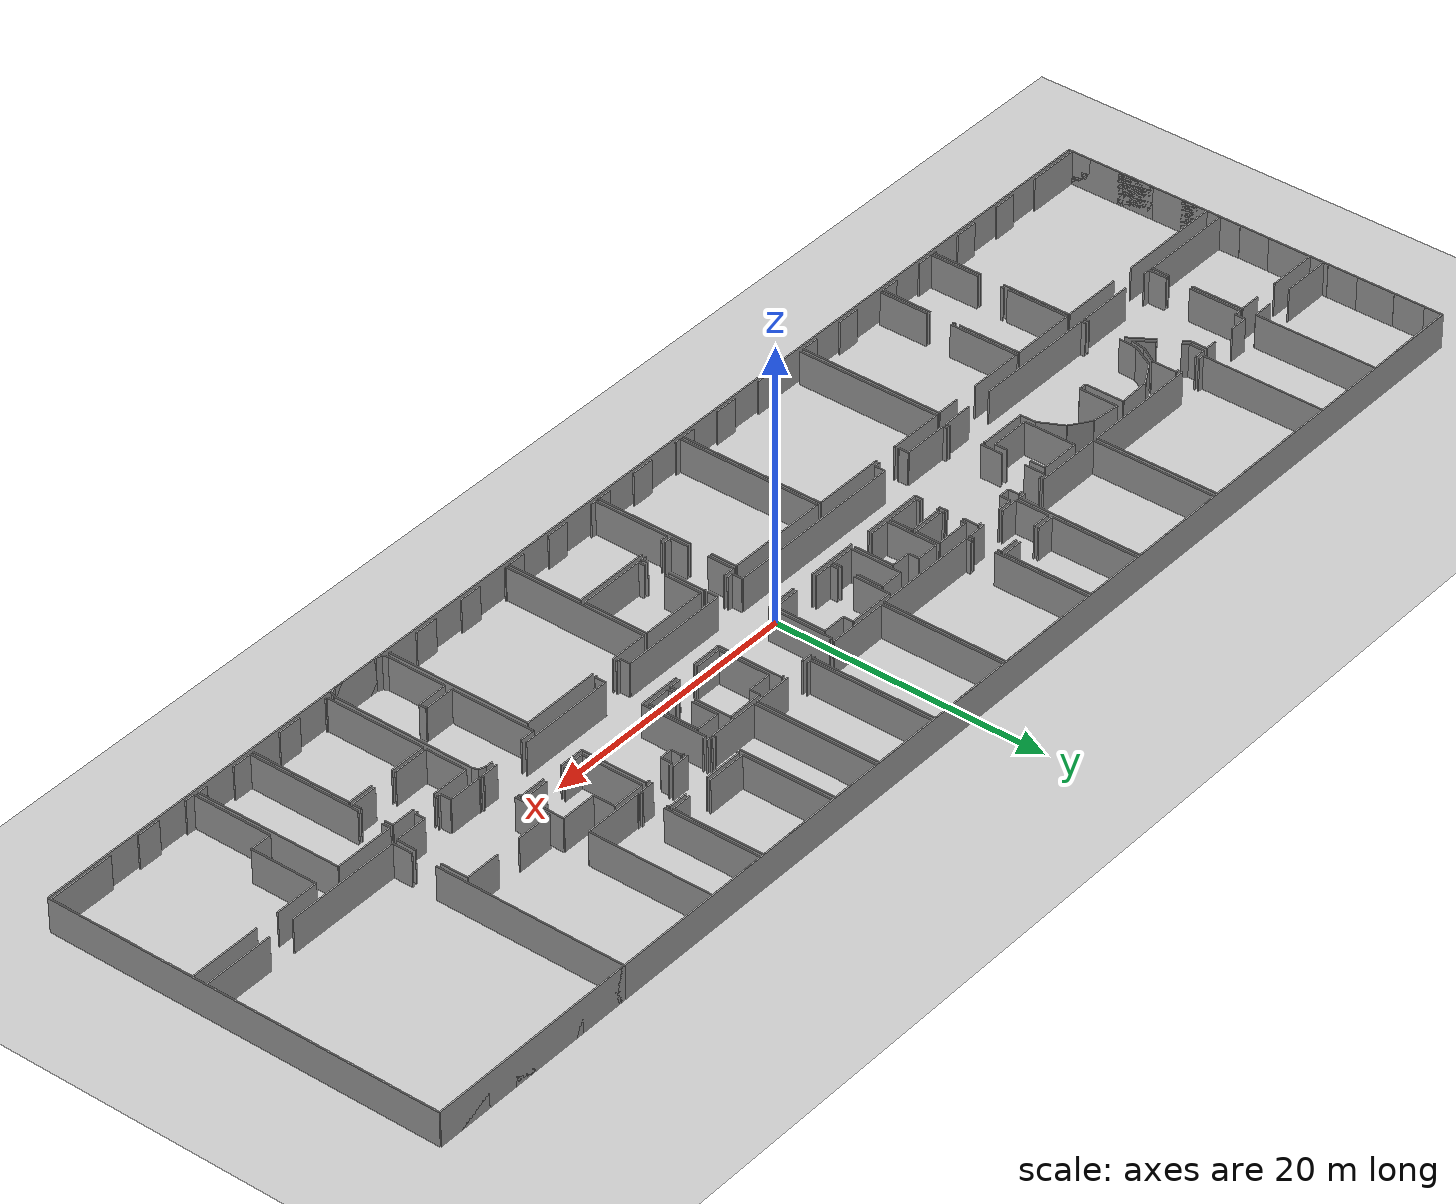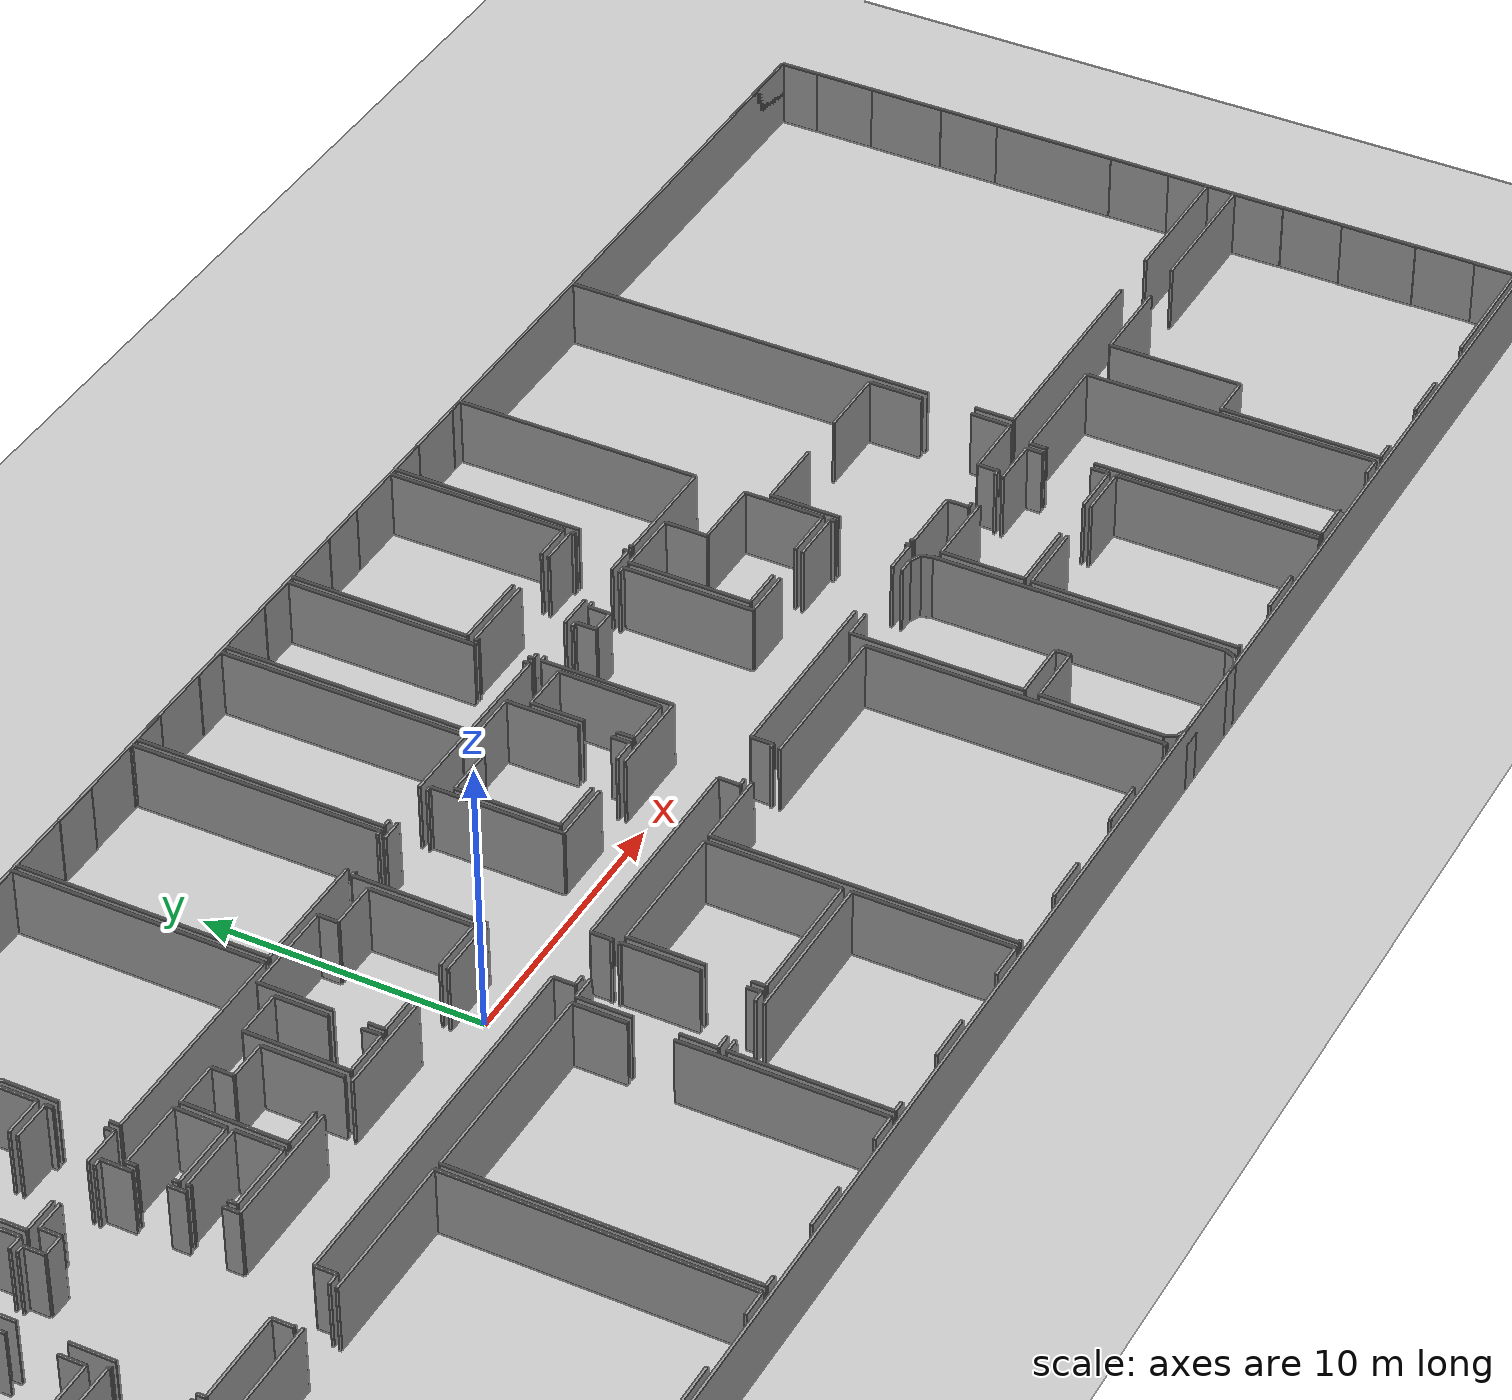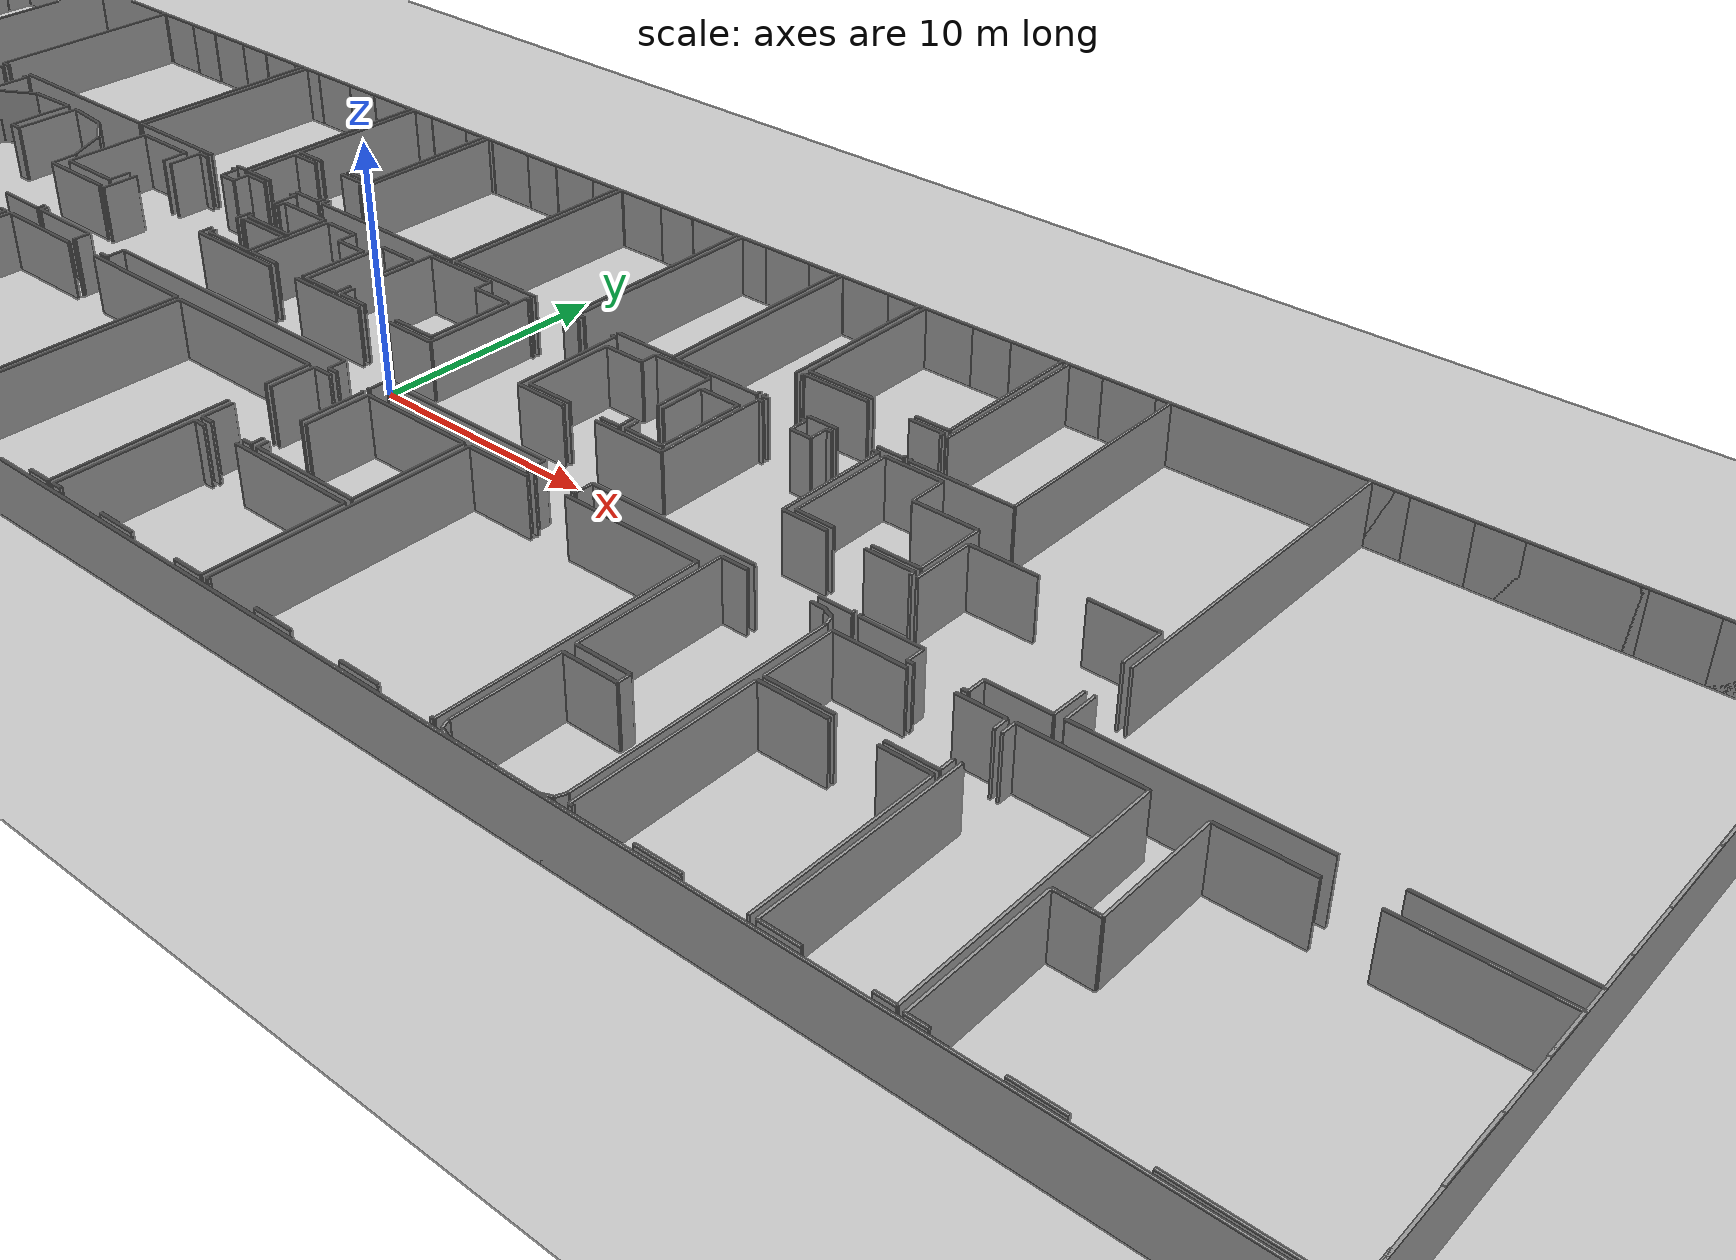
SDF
<sdf version="1.6">
  <world name="default">
    <light name="sun" type="directional">
      <cast_shadows>1</cast_shadows>
      <pose frame="">0 0 10 0 -0 0</pose>
      <diffuse>0.8 0.8 0.8 1</diffuse>
      <specular>0.1 0.1 0.1 1</specular>
      <attenuation>
        <range>1000</range>
        <constant>0.9</constant>
        <linear>0.01</linear>
        <quadratic>0.001</quadratic>
      </attenuation>
      <direction>-0.5 0.5 -1</direction>
    </light>
    <model name="ground_plane">
      <static>1</static>
      <link name="link">
        <collision name="collision">
          <geometry>
            <plane>
              <normal>0 0 1</normal>
              <size>100 100</size>
            </plane>
          </geometry>
          <surface>
            <friction>
              <ode>
                <mu>100</mu>
                <mu2>50</mu2>
              </ode>
              <torsional>
                <ode />
              </torsional>
            </friction>
            <contact>
              <ode />
            </contact>
            <bounce />
          </surface>
          <max_contacts>10</max_contacts>
        </collision>
        <visual name="visual">
          <cast_shadows>0</cast_shadows>
          <geometry>
            <plane>
              <normal>0 0 1</normal>
              <size>100 100</size>
            </plane>
          </geometry>
          <material>
            <script>
              <uri>file://media/materials/scripts/gazebo.material</uri>
              <name>Gazebo/Grey</name>
            </script>
          </material>
        </visual>
        <self_collide>0</self_collide>
        <kinematic>0</kinematic>
        <gravity>1</gravity>
      </link>
    </model>
    <gravity>0 0 -9.8</gravity>
    <magnetic_field>6e-06 2.3e-05 -4.2e-05</magnetic_field>
    <atmosphere type="adiabatic" />
    <physics default="0" name="default_physics" type="ode">
      <max_step_size>0.001</max_step_size>
      <real_time_factor>1</real_time_factor>
      <real_time_update_rate>1000</real_time_update_rate>
    </physics>
    <scene>
      <ambient>0.4 0.4 0.4 1</ambient>
      <background>0.7 0.7 0.7 1</background>
      <shadows>1</shadows>
    </scene>
    <spherical_coordinates>
      <surface_model>EARTH_WGS84</surface_model>
      <latitude_deg>0</latitude_deg>
      <longitude_deg>0</longitude_deg>
      <elevation>0</elevation>
      <heading_deg>0</heading_deg>
    </spherical_coordinates>
  <model name="0510032266_A_40_1_103">
		<static>1</static>
		<link name="Wall_0">
			<collision name="Wall_0_Collision">
				<geometry>
					<box>
						<size>1.51094070373 0.1 2.5</size>
					</box>
				</geometry>
				<pose frame="">0.755470351867 0 1.25 0 0 0</pose>
			</collision>
			<visual name="Wall_0_Visual">
				<pose frame="">0.755470351867 0 1.25 0 0 0</pose>
				<geometry>
					<box>
						<size>1.51094070373 0.1 2.5</size>
					</box>
				</geometry>
				<material>
					<script>
						<uri>file://media/materials/scripts/gazebo.material</uri>
						<name>Gazebo/Grey</name>
					</script>
					<ambient>1 1 1 1</ambient>
				</material>
			</visual>
			<pose frame="">7.24809719992 -9.0151144854 0 0 0 3.14159265359</pose>
		</link>
		<link name="Wall_1">
			<collision name="Wall_1_Collision">
				<geometry>
					<box>
						<size>3.74884943281 0.1 2.5</size>
					</box>
				</geometry>
				<pose frame="">1.87442471641 0 1.25 0 0 0</pose>
			</collision>
			<visual name="Wall_1_Visual">
				<pose frame="">1.87442471641 0 1.25 0 0 0</pose>
				<geometry>
					<box>
						<size>3.74884943281 0.1 2.5</size>
					</box>
				</geometry>
				<material>
					<script>
						<uri>file://media/materials/scripts/gazebo.material</uri>
						<name>Gazebo/Grey</name>
					</script>
					<ambient>1 1 1 1</ambient>
				</material>
			</visual>
			<pose frame="">3.76167230577 -9.0151144854 0 0 0 3.14159265359</pose>
		</link>
		<link name="Wall_2">
			<collision name="Wall_2_Collision">
				<geometry>
					<box>
						<size>0.356882137484 0.1 2.5</size>
					</box>
				</geometry>
				<pose frame="">0.178441068742 0 1.25 0 0 0</pose>
			</collision>
			<visual name="Wall_2_Visual">
				<pose frame="">0.178441068742 0 1.25 0 0 0</pose>
				<geometry>
					<box>
						<size>0.356882137484 0.1 2.5</size>
					</box>
				</geometry>
				<material>
					<script>
						<uri>file://media/materials/scripts/gazebo.material</uri>
						<name>Gazebo/Grey</name>
					</script>
					<ambient>1 1 1 1</ambient>
				</material>
			</visual>
			<pose frame="">0.0128228729583 -9.0151144854 0 0 0 1.57079632679</pose>
		</link>
		<link name="Wall_3">
			<collision name="Wall_3_Collision">
				<geometry>
					<box>
						<size>2.80008379303 0.1 2.5</size>
					</box>
				</geometry>
				<pose frame="">1.40004189652 0 1.25 0 0 0</pose>
			</collision>
			<visual name="Wall_3_Visual">
				<pose frame="">1.40004189652 0 1.25 0 0 0</pose>
				<geometry>
					<box>
						<size>2.80008379303 0.1 2.5</size>
					</box>
				</geometry>
				<material>
					<script>
						<uri>file://media/materials/scripts/gazebo.material</uri>
						<name>Gazebo/Grey</name>
					</script>
					<ambient>1 1 1 1</ambient>
				</material>
			</visual>
			<pose frame="">0.0128228729583 -6.42984555421 0 0 0 1.57079632679</pose>
		</link>
		<link name="Wall_4">
			<collision name="Wall_4_Collision">
				<geometry>
					<box>
						<size>1.328373463 0.1 2.5</size>
					</box>
				</geometry>
				<pose frame="">0.6641867315 0 1.25 0 0 0</pose>
			</collision>
			<visual name="Wall_4_Visual">
				<pose frame="">0.6641867315 0 1.25 0 0 0</pose>
				<geometry>
					<box>
						<size>1.328373463 0.1 2.5</size>
					</box>
				</geometry>
				<material>
					<script>
						<uri>file://media/materials/scripts/gazebo.material</uri>
						<name>Gazebo/Grey</name>
					</script>
					<ambient>1 1 1 1</ambient>
				</material>
			</visual>
			<pose frame="">0.0128228729583 -1.35770102393 0 0 0 1.57079632679</pose>
		</link>
		<link name="Wall_5">
			<collision name="Wall_5_Collision">
				<geometry>
					<box>
						<size>4.88183278212 0.1 2.5</size>
					</box>
				</geometry>
				<pose frame="">2.44091639106 0 1.25 0 0 0</pose>
			</collision>
			<visual name="Wall_5_Visual">
				<pose frame="">2.44091639106 0 1.25 0 0 0</pose>
				<geometry>
					<box>
						<size>4.88183278212 0.1 2.5</size>
					</box>
				</geometry>
				<material>
					<script>
						<uri>file://media/materials/scripts/gazebo.material</uri>
						<name>Gazebo/Grey</name>
					</script>
					<ambient>1 1 1 1</ambient>
				</material>
			</visual>
			<pose frame="">0.0128228729583 -0.0293275609245 0 0 0 0.0</pose>
		</link>
		<link name="Wall_6">
			<collision name="Wall_6_Collision">
				<geometry>
					<box>
						<size>8.98593916581 0.1 2.5</size>
					</box>
				</geometry>
				<pose frame="">4.4929695829 0 1.25 0 0 0</pose>
			</collision>
			<visual name="Wall_6_Visual">
				<pose frame="">4.4929695829 0 1.25 0 0 0</pose>
				<geometry>
					<box>
						<size>8.98593916581 0.1 2.5</size>
					</box>
				</geometry>
				<material>
					<script>
						<uri>file://media/materials/scripts/gazebo.material</uri>
						<name>Gazebo/Grey</name>
					</script>
					<ambient>1 1 1 1</ambient>
				</material>
			</visual>
			<pose frame="">7.19579003498 -0.0293275609245 0 0 0 -1.56497529247</pose>
		</link>
		<link name="Wall_7">
			<collision name="Wall_7_Collision">
				<geometry>
					<box>
						<size>7.20810507138 0.1 2.5</size>
					</box>
				</geometry>
				<pose frame="">3.60405253569 0 1.25 0 0 0</pose>
			</collision>
			<visual name="Wall_7_Visual">
				<pose frame="">3.60405253569 0 1.25 0 0 0</pose>
				<geometry>
					<box>
						<size>7.20810507138 0.1 2.5</size>
					</box>
				</geometry>
				<material>
					<script>
						<uri>file://media/materials/scripts/gazebo.material</uri>
						<name>Gazebo/Grey</name>
					</script>
					<ambient>1 1 1 1</ambient>
				</material>
			</visual>
			<pose frame="">7.22486367763 -17.00795399 0 0 0 3.14159265359</pose>
		</link>
		<link name="Wall_8">
			<collision name="Wall_8_Collision">
				<geometry>
					<box>
						<size>1.56794535679 0.1 2.5</size>
					</box>
				</geometry>
				<pose frame="">0.783972678393 0 1.25 0 0 0</pose>
			</collision>
			<visual name="Wall_8_Visual">
				<pose frame="">0.783972678393 0 1.25 0 0 0</pose>
				<geometry>
					<box>
						<size>1.56794535679 0.1 2.5</size>
					</box>
				</geometry>
				<material>
					<script>
						<uri>file://media/materials/scripts/gazebo.material</uri>
						<name>Gazebo/Grey</name>
					</script>
					<ambient>1 1 1 1</ambient>
				</material>
			</visual>
			<pose frame="">0.0167586062426 -17.00795399 0 0 0 1.57079632679</pose>
		</link>
		<link name="Wall_9">
			<collision name="Wall_9_Collision">
				<geometry>
					<box>
						<size>3.16318692829 0.1 2.5</size>
					</box>
				</geometry>
				<pose frame="">1.58159346414 0 1.25 0 0 0</pose>
			</collision>
			<visual name="Wall_9_Visual">
				<pose frame="">1.58159346414 0 1.25 0 0 0</pose>
				<geometry>
					<box>
						<size>3.16318692829 0.1 2.5</size>
					</box>
				</geometry>
				<material>
					<script>
						<uri>file://media/materials/scripts/gazebo.material</uri>
						<name>Gazebo/Grey</name>
					</script>
					<ambient>1 1 1 1</ambient>
				</material>
			</visual>
			<pose frame="">0.0167586062426 -13.2219055297 0 0 0 1.57079632679</pose>
		</link>
		<link name="Wall_10">
			<collision name="Wall_10_Collision">
				<geometry>
					<box>
						<size>3.83378509627 0.1 2.5</size>
					</box>
				</geometry>
				<pose frame="">1.91689254813 0 1.25 0 0 0</pose>
			</collision>
			<visual name="Wall_10_Visual">
				<pose frame="">1.91689254813 0 1.25 0 0 0</pose>
				<geometry>
					<box>
						<size>3.83378509627 0.1 2.5</size>
					</box>
				</geometry>
				<material>
					<script>
						<uri>file://media/materials/scripts/gazebo.material</uri>
						<name>Gazebo/Grey</name>
					</script>
					<ambient>1 1 1 1</ambient>
				</material>
			</visual>
			<pose frame="">0.0167586062426 -10.0587186014 0 0 0 0.0</pose>
		</link>
		<link name="Wall_11">
			<collision name="Wall_11_Collision">
				<geometry>
					<box>
						<size>1.5968920403 0.1 2.5</size>
					</box>
				</geometry>
				<pose frame="">0.798446020148 0 1.25 0 0 0</pose>
			</collision>
			<visual name="Wall_11_Visual">
				<pose frame="">0.798446020148 0 1.25 0 0 0</pose>
				<geometry>
					<box>
						<size>1.5968920403 0.1 2.5</size>
					</box>
				</geometry>
				<material>
					<script>
						<uri>file://media/materials/scripts/gazebo.material</uri>
						<name>Gazebo/Grey</name>
					</script>
					<ambient>1 1 1 1</ambient>
				</material>
			</visual>
			<pose frame="">5.64968164996 -10.0587186014 0 0 0 0.0</pose>
		</link>
		<link name="Wall_12">
			<collision name="Wall_12_Collision">
				<geometry>
					<box>
						<size>3.85155937561 0.1 2.5</size>
					</box>
				</geometry>
				<pose frame="">1.92577968781 0 1.25 0 0 0</pose>
			</collision>
			<visual name="Wall_12_Visual">
				<pose frame="">1.92577968781 0 1.25 0 0 0</pose>
				<geometry>
					<box>
						<size>3.85155937561 0.1 2.5</size>
					</box>
				</geometry>
				<material>
					<script>
						<uri>file://media/materials/scripts/gazebo.material</uri>
						<name>Gazebo/Grey</name>
					</script>
					<ambient>1 1 1 1</ambient>
				</material>
			</visual>
			<pose frame="">7.24657369026 -10.0587186014 0 0 0 -1.57079632679</pose>
		</link>
		<link name="Wall_13">
			<collision name="Wall_13_Collision">
				<geometry>
					<box>
						<size>1.33147052897 0.1 2.5</size>
					</box>
				</geometry>
				<pose frame="">0.665735264484 0 1.25 0 0 0</pose>
			</collision>
			<visual name="Wall_13_Visual">
				<pose frame="">0.665735264484 0 1.25 0 0 0</pose>
				<geometry>
					<box>
						<size>1.33147052897 0.1 2.5</size>
					</box>
				</geometry>
				<material>
					<script>
						<uri>file://media/materials/scripts/gazebo.material</uri>
						<name>Gazebo/Grey</name>
					</script>
					<ambient>1 1 1 1</ambient>
				</material>
			</visual>
			<pose frame="">7.24657369026 -15.6766604668 0 0 0 -1.58710233902</pose>
		</link>
		<link name="Wall_14">
			<collision name="Wall_14_Collision">
				<geometry>
					<box>
						<size>4.30556525382 0.1 2.5</size>
					</box>
				</geometry>
				<pose frame="">2.15278262691 0 1.25 0 0 0</pose>
			</collision>
			<visual name="Wall_14_Visual">
				<pose frame="">2.15278262691 0 1.25 0 0 0</pose>
				<geometry>
					<box>
						<size>4.30556525382 0.1 2.5</size>
					</box>
				</geometry>
				<material>
					<script>
						<uri>file://media/materials/scripts/gazebo.material</uri>
						<name>Gazebo/Grey</name>
					</script>
					<ambient>1 1 1 1</ambient>
				</material>
			</visual>
			<pose frame="">14.3095644667 -17.0360119596 0 0 0 3.14159265359</pose>
		</link>
		<link name="Wall_15">
			<collision name="Wall_15_Collision">
				<geometry>
					<box>
						<size>0.518881997829 0.1 2.5</size>
					</box>
				</geometry>
				<pose frame="">0.259440998914 0 1.25 0 0 0</pose>
			</collision>
			<visual name="Wall_15_Visual">
				<pose frame="">0.259440998914 0 1.25 0 0 0</pose>
				<geometry>
					<box>
						<size>0.518881997829 0.1 2.5</size>
					</box>
				</geometry>
				<material>
					<script>
						<uri>file://media/materials/scripts/gazebo.material</uri>
						<name>Gazebo/Grey</name>
					</script>
					<ambient>1 1 1 1</ambient>
				</material>
			</visual>
			<pose frame="">8.03892567177 -17.0360119596 0 0 0 3.14159265359</pose>
		</link>
		<link name="Wall_16">
			<collision name="Wall_16_Collision">
				<geometry>
					<box>
						<size>1.34690949718 0.1 2.5</size>
					</box>
				</geometry>
				<pose frame="">0.673454748589 0 1.25 0 0 0</pose>
			</collision>
			<visual name="Wall_16_Visual">
				<pose frame="">0.673454748589 0 1.25 0 0 0</pose>
				<geometry>
					<box>
						<size>1.34690949718 0.1 2.5</size>
					</box>
				</geometry>
				<material>
					<script>
						<uri>file://media/materials/scripts/gazebo.material</uri>
						<name>Gazebo/Grey</name>
					</script>
					<ambient>1 1 1 1</ambient>
				</material>
			</visual>
			<pose frame="">7.52004367394 -17.0360119596 0 0 0 1.57079632679</pose>
		</link>
		<link name="Wall_17">
			<collision name="Wall_17_Collision">
				<geometry>
					<box>
						<size>3.83632427903 0.1 2.5</size>
					</box>
				</geometry>
				<pose frame="">1.91816213952 0 1.25 0 0 0</pose>
			</collision>
			<visual name="Wall_17_Visual">
				<pose frame="">1.91816213952 0 1.25 0 0 0</pose>
				<geometry>
					<box>
						<size>3.83632427903 0.1 2.5</size>
					</box>
				</geometry>
				<material>
					<script>
						<uri>file://media/materials/scripts/gazebo.material</uri>
						<name>Gazebo/Grey</name>
					</script>
					<ambient>1 1 1 1</ambient>
				</material>
			</visual>
			<pose frame="">7.52004367394 -13.8874253322 0 0 0 1.57079632679</pose>
		</link>
		<link name="Wall_18">
			<collision name="Wall_18_Collision">
				<geometry>
					<box>
						<size>0.49057011001 0.1 2.5</size>
					</box>
				</geometry>
				<pose frame="">0.245285055005 0 1.25 0 0 0</pose>
			</collision>
			<visual name="Wall_18_Visual">
				<pose frame="">0.245285055005 0 1.25 0 0 0</pose>
				<geometry>
					<box>
						<size>0.49057011001 0.1 2.5</size>
					</box>
				</geometry>
				<material>
					<script>
						<uri>file://media/materials/scripts/gazebo.material</uri>
						<name>Gazebo/Grey</name>
					</script>
					<ambient>1 1 1 1</ambient>
				</material>
			</visual>
			<pose frame="">7.52004367394 -10.0511010531 0 0 0 0.0</pose>
		</link>
		<link name="Wall_19">
			<collision name="Wall_19_Collision">
				<geometry>
					<box>
						<size>0.748804997112 0.1 2.5</size>
					</box>
				</geometry>
				<pose frame="">0.374402498556 0 1.25 0 0 0</pose>
			</collision>
			<visual name="Wall_19_Visual">
				<pose frame="">0.374402498556 0 1.25 0 0 0</pose>
				<geometry>
					<box>
						<size>0.748804997112 0.1 2.5</size>
					</box>
				</geometry>
				<material>
					<script>
						<uri>file://media/materials/scripts/gazebo.material</uri>
						<name>Gazebo/Grey</name>
					</script>
					<ambient>1 1 1 1</ambient>
				</material>
			</visual>
			<pose frame="">8.01061378395 -10.0511010531 0 0 0 1.57079632679</pose>
		</link>
		<link name="Wall_20">
			<collision name="Wall_20_Collision">
				<geometry>
					<box>
						<size>1.36316026687 0.1 2.5</size>
					</box>
				</geometry>
				<pose frame="">0.681580133434 0 1.25 0 0 0</pose>
			</collision>
			<visual name="Wall_20_Visual">
				<pose frame="">0.681580133434 0 1.25 0 0 0</pose>
				<geometry>
					<box>
						<size>1.36316026687 0.1 2.5</size>
					</box>
				</geometry>
				<material>
					<script>
						<uri>file://media/materials/scripts/gazebo.material</uri>
						<name>Gazebo/Grey</name>
					</script>
					<ambient>1 1 1 1</ambient>
				</material>
			</visual>
			<pose frame="">8.01061378395 -9.30229605601 0 0 0 0.0</pose>
		</link>
		<link name="Wall_21">
			<collision name="Wall_21_Collision">
				<geometry>
					<box>
						<size>0.88376256102 0.1 2.5</size>
					</box>
				</geometry>
				<pose frame="">0.44188128051 0 1.25 0 0 0</pose>
			</collision>
			<visual name="Wall_21_Visual">
				<pose frame="">0.44188128051 0 1.25 0 0 0</pose>
				<geometry>
					<box>
						<size>0.88376256102 0.1 2.5</size>
					</box>
				</geometry>
				<material>
					<script>
						<uri>file://media/materials/scripts/gazebo.material</uri>
						<name>Gazebo/Grey</name>
					</script>
					<ambient>1 1 1 1</ambient>
				</material>
			</visual>
			<pose frame="">11.1282223816 -9.30229605601 0 0 0 0.0</pose>
		</link>
		<link name="Wall_22">
			<collision name="Wall_22_Collision">
				<geometry>
					<box>
						<size>1.18021214872 0.1 2.5</size>
					</box>
				</geometry>
				<pose frame="">0.59010607436 0 1.25 0 0 0</pose>
			</collision>
			<visual name="Wall_22_Visual">
				<pose frame="">0.59010607436 0 1.25 0 0 0</pose>
				<geometry>
					<box>
						<size>1.18021214872 0.1 2.5</size>
					</box>
				</geometry>
				<material>
					<script>
						<uri>file://media/materials/scripts/gazebo.material</uri>
						<name>Gazebo/Grey</name>
					</script>
					<ambient>1 1 1 1</ambient>
				</material>
			</visual>
			<pose frame="">12.0119849426 -9.30229605601 0 0 0 -1.57079632679</pose>
		</link>
		<link name="Wall_23">
			<collision name="Wall_23_Collision">
				<geometry>
					<box>
						<size>0.549975058496 0.1 2.5</size>
					</box>
				</geometry>
				<pose frame="">0.274987529248 0 1.25 0 0 0</pose>
			</collision>
			<visual name="Wall_23_Visual">
				<pose frame="">0.274987529248 0 1.25 0 0 0</pose>
				<geometry>
					<box>
						<size>0.549975058496 0.1 2.5</size>
					</box>
				</geometry>
				<material>
					<script>
						<uri>file://media/materials/scripts/gazebo.material</uri>
						<name>Gazebo/Grey</name>
					</script>
					<ambient>1 1 1 1</ambient>
				</material>
			</visual>
			<pose frame="">12.0119849426 -10.4825082047 0 0 0 -1.01461949919</pose>
		</link>
		<link name="Wall_24">
			<collision name="Wall_24_Collision">
				<geometry>
					<box>
						<size>2.02335979868 0.1 2.5</size>
					</box>
				</geometry>
				<pose frame="">1.01167989934 0 1.25 0 0 0</pose>
			</collision>
			<visual name="Wall_24_Visual">
				<pose frame="">1.01167989934 0 1.25 0 0 0</pose>
				<geometry>
					<box>
						<size>2.02335979868 0.1 2.5</size>
					</box>
				</geometry>
				<material>
					<script>
						<uri>file://media/materials/scripts/gazebo.material</uri>
						<name>Gazebo/Grey</name>
					</script>
					<ambient>1 1 1 1</ambient>
				</material>
			</visual>
			<pose frame="">13.1417943135 -12.2624753223 0 0 0 -0.994610500639</pose>
		</link>
		<link name="Wall_25">
			<collision name="Wall_25_Collision">
				<geometry>
					<box>
						<size>0.36781852518 0.1 2.5</size>
					</box>
				</geometry>
				<pose frame="">0.18390926259 0 1.25 0 0 0</pose>
			</collision>
			<visual name="Wall_25_Visual">
				<pose frame="">0.18390926259 0 1.25 0 0 0</pose>
				<geometry>
					<box>
						<size>0.36781852518 0.1 2.5</size>
					</box>
				</geometry>
				<material>
					<script>
						<uri>file://media/materials/scripts/gazebo.material</uri>
						<name>Gazebo/Grey</name>
					</script>
					<ambient>1 1 1 1</ambient>
				</material>
			</visual>
			<pose frame="">14.2441805105 -16.6740514565 0 0 0 -1.39208511912</pose>
		</link>
		<link name="Wall_26">
			<collision name="Wall_26_Collision">
				<geometry>
					<box>
						<size>0.182440281595 0.1 2.5</size>
					</box>
				</geometry>
				<pose frame="">0.0912201407977 0 1.25 0 0 0</pose>
			</collision>
			<visual name="Wall_26_Visual">
				<pose frame="">0.0912201407977 0 1.25 0 0 0</pose>
				<geometry>
					<box>
						<size>0.182440281595 0.1 2.5</size>
					</box>
				</geometry>
				<material>
					<script>
						<uri>file://media/materials/scripts/gazebo.material</uri>
						<name>Gazebo/Grey</name>
					</script>
					<ambient>1 1 1 1</ambient>
				</material>
			</visual>
			<pose frame="">14.432968749 -28.6749909542 0 0 0 3.14159265359</pose>
		</link>
		<link name="Wall_27">
			<collision name="Wall_27_Collision">
				<geometry>
					<box>
						<size>1.75025867924 0.1 2.5</size>
					</box>
				</geometry>
				<pose frame="">0.875129339622 0 1.25 0 0 0</pose>
			</collision>
			<visual name="Wall_27_Visual">
				<pose frame="">0.875129339622 0 1.25 0 0 0</pose>
				<geometry>
					<box>
						<size>1.75025867924 0.1 2.5</size>
					</box>
				</geometry>
				<material>
					<script>
						<uri>file://media/materials/scripts/gazebo.material</uri>
						<name>Gazebo/Grey</name>
					</script>
					<ambient>1 1 1 1</ambient>
				</material>
			</visual>
			<pose frame="">12.0137623706 -28.6749909542 0 0 0 3.14159265359</pose>
		</link>
		<link name="Wall_28">
			<collision name="Wall_28_Collision">
				<geometry>
					<box>
						<size>1.75482920822 0.1 2.5</size>
					</box>
				</geometry>
				<pose frame="">0.87741460411 0 1.25 0 0 0</pose>
			</collision>
			<visual name="Wall_28_Visual">
				<pose frame="">0.87741460411 0 1.25 0 0 0</pose>
				<geometry>
					<box>
						<size>1.75482920822 0.1 2.5</size>
					</box>
				</geometry>
				<material>
					<script>
						<uri>file://media/materials/scripts/gazebo.material</uri>
						<name>Gazebo/Grey</name>
					</script>
					<ambient>1 1 1 1</ambient>
				</material>
			</visual>
			<pose frame="">8.0101059474 -28.6749909542 0 0 0 3.14159265359</pose>
		</link>
		<link name="Wall_29">
			<collision name="Wall_29_Collision">
				<geometry>
					<box>
						<size>4.00822695216 0.1 2.5</size>
					</box>
				</geometry>
				<pose frame="">2.00411347608 0 1.25 0 0 0</pose>
			</collision>
			<visual name="Wall_29_Visual">
				<pose frame="">2.00411347608 0 1.25 0 0 0</pose>
				<geometry>
					<box>
						<size>4.00822695216 0.1 2.5</size>
					</box>
				</geometry>
				<material>
					<script>
						<uri>file://media/materials/scripts/gazebo.material</uri>
						<name>Gazebo/Grey</name>
					</script>
					<ambient>1 1 1 1</ambient>
				</material>
			</visual>
			<pose frame="">4.00822695216 -28.6749909542 0 0 0 3.14159265359</pose>
		</link>
		<link name="Wall_30">
			<collision name="Wall_30_Collision">
				<geometry>
					<box>
						<size>1.43387650685 0.1 2.5</size>
					</box>
				</geometry>
				<pose frame="">0.716938253423 0 1.25 0 0 0</pose>
			</collision>
			<visual name="Wall_30_Visual">
				<pose frame="">0.716938253423 0 1.25 0 0 0</pose>
				<geometry>
					<box>
						<size>1.43387650685 0.1 2.5</size>
					</box>
				</geometry>
				<material>
					<script>
						<uri>file://media/materials/scripts/gazebo.material</uri>
						<name>Gazebo/Grey</name>
					</script>
					<ambient>1 1 1 1</ambient>
				</material>
			</visual>
			<pose frame="">0.0 -28.6749909542 0 0 0 1.57079632679</pose>
		</link>
		<link name="Wall_31">
			<collision name="Wall_31_Collision">
				<geometry>
					<box>
						<size>2.75831423656 0.1 2.5</size>
					</box>
				</geometry>
				<pose frame="">1.37915711828 0 1.25 0 0 0</pose>
			</collision>
			<visual name="Wall_31_Visual">
				<pose frame="">1.37915711828 0 1.25 0 0 0</pose>
				<geometry>
					<box>
						<size>2.75831423656 0.1 2.5</size>
					</box>
				</geometry>
				<material>
					<script>
						<uri>file://media/materials/scripts/gazebo.material</uri>
						<name>Gazebo/Grey</name>
					</script>
					<ambient>1 1 1 1</ambient>
				</material>
			</visual>
			<pose frame="">0.0 -25.0072684107 0 0 0 1.57079632679</pose>
		</link>
		<link name="Wall_32">
			<collision name="Wall_32_Collision">
				<geometry>
					<box>
						<size>1.94882277139 0.1 2.5</size>
					</box>
				</geometry>
				<pose frame="">0.974411385696 0 1.25 0 0 0</pose>
			</collision>
			<visual name="Wall_32_Visual">
				<pose frame="">0.974411385696 0 1.25 0 0 0</pose>
				<geometry>
					<box>
						<size>1.94882277139 0.1 2.5</size>
					</box>
				</geometry>
				<material>
					<script>
						<uri>file://media/materials/scripts/gazebo.material</uri>
						<name>Gazebo/Grey</name>
					</script>
					<ambient>1 1 1 1</ambient>
				</material>
			</visual>
			<pose frame="">0.0 -20.0062209978 0 0 0 1.57079632679</pose>
		</link>
		<link name="Wall_33">
			<collision name="Wall_33_Collision">
				<geometry>
					<box>
						<size>8.07777516806 0.1 2.5</size>
					</box>
				</geometry>
				<pose frame="">4.03888758403 0 1.25 0 0 0</pose>
			</collision>
			<visual name="Wall_33_Visual">
				<pose frame="">4.03888758403 0 1.25 0 0 0</pose>
				<geometry>
					<box>
						<size>8.07777516806 0.1 2.5</size>
					</box>
				</geometry>
				<material>
					<script>
						<uri>file://media/materials/scripts/gazebo.material</uri>
						<name>Gazebo/Grey</name>
					</script>
					<ambient>1 1 1 1</ambient>
				</material>
			</visual>
			<pose frame="">0.0 -18.0573982264 0 0 0 0.0</pose>
		</link>
		<link name="Wall_34">
			<collision name="Wall_34_Collision">
				<geometry>
					<box>
						<size>4.58309792993 0.1 2.5</size>
					</box>
				</geometry>
				<pose frame="">2.29154896497 0 1.25 0 0 0</pose>
			</collision>
			<visual name="Wall_34_Visual">
				<pose frame="">2.29154896497 0 1.25 0 0 0</pose>
				<geometry>
					<box>
						<size>4.58309792993 0.1 2.5</size>
					</box>
				</geometry>
				<material>
					<script>
						<uri>file://media/materials/scripts/gazebo.material</uri>
						<name>Gazebo/Grey</name>
					</script>
					<ambient>1 1 1 1</ambient>
				</material>
			</visual>
			<pose frame="">9.85951971358 -18.0573982264 0 0 0 0.0</pose>
		</link>
		<link name="Wall_35">
			<collision name="Wall_35_Collision">
				<geometry>
					<box>
						<size>5.11683414693 0.1 2.5</size>
					</box>
				</geometry>
				<pose frame="">2.55841707346 0 1.25 0 0 0</pose>
			</collision>
			<visual name="Wall_35_Visual">
				<pose frame="">2.55841707346 0 1.25 0 0 0</pose>
				<geometry>
					<box>
						<size>5.11683414693 0.1 2.5</size>
					</box>
				</geometry>
				<material>
					<script>
						<uri>file://media/materials/scripts/gazebo.material</uri>
						<name>Gazebo/Grey</name>
					</script>
					<ambient>1 1 1 1</ambient>
				</material>
			</visual>
			<pose frame="">14.4426176435 -18.0573982264 0 0 0 -1.57079632679</pose>
		</link>
		<link name="Wall_36">
			<collision name="Wall_36_Collision">
				<geometry>
					<box>
						<size>3.73438855646 0.1 2.5</size>
					</box>
				</geometry>
				<pose frame="">1.86719427823 0 1.25 0 0 0</pose>
			</collision>
			<visual name="Wall_36_Visual">
				<pose frame="">1.86719427823 0 1.25 0 0 0</pose>
				<geometry>
					<box>
						<size>3.73438855646 0.1 2.5</size>
					</box>
				</geometry>
				<material>
					<script>
						<uri>file://media/materials/scripts/gazebo.material</uri>
						<name>Gazebo/Grey</name>
					</script>
					<ambient>1 1 1 1</ambient>
				</material>
			</visual>
			<pose frame="">14.4426176435 -24.9406148631 0 0 0 -1.57338012468</pose>
		</link>
		<link name="Wall_37">
			<collision name="Wall_37_Collision">
				<geometry>
					<box>
						<size>8.75459433381 0.1 2.5</size>
					</box>
				</geometry>
				<pose frame="">4.37729716691 0 1.25 0 0 0</pose>
			</collision>
			<visual name="Wall_37_Visual">
				<pose frame="">4.37729716691 0 1.25 0 0 0</pose>
				<geometry>
					<box>
						<size>8.75459433381 0.1 2.5</size>
					</box>
				</geometry>
				<material>
					<script>
						<uri>file://media/materials/scripts/gazebo.material</uri>
						<name>Gazebo/Grey</name>
					</script>
					<ambient>1 1 1 1</ambient>
				</material>
			</visual>
			<pose frame="">23.7045406936 -9.0210815649 0 0 0 3.14159265359</pose>
		</link>
		<link name="Wall_38">
			<collision name="Wall_38_Collision">
				<geometry>
					<box>
						<size>0.423408725902 0.1 2.5</size>
					</box>
				</geometry>
				<pose frame="">0.211704362951 0 1.25 0 0 0</pose>
			</collision>
			<visual name="Wall_38_Visual">
				<pose frame="">0.211704362951 0 1.25 0 0 0</pose>
				<geometry>
					<box>
						<size>0.423408725902 0.1 2.5</size>
					</box>
				</geometry>
				<material>
					<script>
						<uri>file://media/materials/scripts/gazebo.material</uri>
						<name>Gazebo/Grey</name>
					</script>
					<ambient>1 1 1 1</ambient>
				</material>
			</visual>
			<pose frame="">13.2020999041 -9.0210815649 0 0 0 3.14159265359</pose>
		</link>
		<link name="Wall_39">
			<collision name="Wall_39_Collision">
				<geometry>
					<box>
						<size>8.99645149209 0.1 2.5</size>
					</box>
				</geometry>
				<pose frame="">4.49822574604 0 1.25 0 0 0</pose>
			</collision>
			<visual name="Wall_39_Visual">
				<pose frame="">4.49822574604 0 1.25 0 0 0</pose>
				<geometry>
					<box>
						<size>8.99645149209 0.1 2.5</size>
					</box>
				</geometry>
				<material>
					<script>
						<uri>file://media/materials/scripts/gazebo.material</uri>
						<name>Gazebo/Grey</name>
					</script>
					<ambient>1 1 1 1</ambient>
				</material>
			</visual>
			<pose frame="">12.7786911782 -9.0210815649 0 0 0 1.57079632679</pose>
		</link>
		<link name="Wall_40">
			<collision name="Wall_40_Collision">
				<geometry>
					<box>
						<size>0.129117443551 0.1 2.5</size>
					</box>
				</geometry>
				<pose frame="">0.0645587217754 0 1.25 0 0 0</pose>
			</collision>
			<visual name="Wall_40_Visual">
				<pose frame="">0.0645587217754 0 1.25 0 0 0</pose>
				<geometry>
					<box>
						<size>0.129117443551 0.1 2.5</size>
					</box>
				</geometry>
				<material>
					<script>
						<uri>file://media/materials/scripts/gazebo.material</uri>
						<name>Gazebo/Grey</name>
					</script>
					<ambient>1 1 1 1</ambient>
				</material>
			</visual>
			<pose frame="">12.7786911782 -0.0246300728111 0 0 0 0.0</pose>
		</link>
		<link name="Wall_41">
			<collision name="Wall_41_Collision">
				<geometry>
					<box>
						<size>1.76143108341 0.1 2.5</size>
					</box>
				</geometry>
				<pose frame="">0.880715541703 0 1.25 0 0 0</pose>
			</collision>
			<visual name="Wall_41_Visual">
				<pose frame="">0.880715541703 0 1.25 0 0 0</pose>
				<geometry>
					<box>
						<size>1.76143108341 0.1 2.5</size>
					</box>
				</geometry>
				<material>
					<script>
						<uri>file://media/materials/scripts/gazebo.material</uri>
						<name>Gazebo/Grey</name>
					</script>
					<ambient>1 1 1 1</ambient>
				</material>
			</visual>
			<pose frame="">15.1283239489 -0.0246300728111 0 0 0 0.0</pose>
		</link>
		<link name="Wall_42">
			<collision name="Wall_42_Collision">
				<geometry>
					<box>
						<size>1.76193891996 0.1 2.5</size>
					</box>
				</geometry>
				<pose frame="">0.880969459979 0 1.25 0 0 0</pose>
			</collision>
			<visual name="Wall_42_Visual">
				<pose frame="">0.880969459979 0 1.25 0 0 0</pose>
				<geometry>
					<box>
						<size>1.76193891996 0.1 2.5</size>
					</box>
				</geometry>
				<material>
					<script>
						<uri>file://media/materials/scripts/gazebo.material</uri>
						<name>Gazebo/Grey</name>
					</script>
					<ambient>1 1 1 1</ambient>
				</material>
			</visual>
			<pose frame="">19.1357891463 -0.0246300728111 0 0 0 0.0</pose>
		</link>
		<link name="Wall_43">
			<collision name="Wall_43_Collision">
				<geometry>
					<box>
						<size>0.504916492627 0.1 2.5</size>
					</box>
				</geometry>
				<pose frame="">0.252458246313 0 1.25 0 0 0</pose>
			</collision>
			<visual name="Wall_43_Visual">
				<pose frame="">0.252458246313 0 1.25 0 0 0</pose>
				<geometry>
					<box>
						<size>0.504916492627 0.1 2.5</size>
					</box>
				</geometry>
				<material>
					<script>
						<uri>file://media/materials/scripts/gazebo.material</uri>
						<name>Gazebo/Grey</name>
					</script>
					<ambient>1 1 1 1</ambient>
				</material>
			</visual>
			<pose frame="">23.14820575 -0.0246300728111 0 0 0 0.0</pose>
		</link>
		<link name="Wall_44">
			<collision name="Wall_44_Collision">
				<geometry>
					<box>
						<size>8.99659842977 0.1 2.5</size>
					</box>
				</geometry>
				<pose frame="">4.49829921489 0 1.25 0 0 0</pose>
			</collision>
			<visual name="Wall_44_Visual">
				<pose frame="">4.49829921489 0 1.25 0 0 0</pose>
				<geometry>
					<box>
						<size>8.99659842977 0.1 2.5</size>
					</box>
				</geometry>
				<material>
					<script>
						<uri>file://media/materials/scripts/gazebo.material</uri>
						<name>Gazebo/Grey</name>
					</script>
					<ambient>1 1 1 1</ambient>
				</material>
			</visual>
			<pose frame="">23.6531222426 -0.0246300728111 0 0 0 -1.56508097434</pose>
		</link>
		<link name="Wall_45">
			<collision name="Wall_45_Collision">
				<geometry>
					<box>
						<size>1.45981696457 0.1 2.5</size>
					</box>
				</geometry>
				<pose frame="">0.729908482284 0 1.25 0 0 0</pose>
			</collision>
			<visual name="Wall_45_Visual">
				<pose frame="">0.729908482284 0 1.25 0 0 0</pose>
				<geometry>
					<box>
						<size>1.45981696457 0.1 2.5</size>
					</box>
				</geometry>
				<material>
					<script>
						<uri>file://media/materials/scripts/gazebo.material</uri>
						<name>Gazebo/Grey</name>
					</script>
					<ambient>1 1 1 1</ambient>
				</material>
			</visual>
			<pose frame="">14.2369438396 -13.3639728054 0 0 0 2.1436021653</pose>
		</link>
		<link name="Wall_46">
			<collision name="Wall_46_Collision">
				<geometry>
					<box>
						<size>0.481151165043 0.1 2.5</size>
					</box>
				</geometry>
				<pose frame="">0.240575582521 0 1.25 0 0 0</pose>
			</collision>
			<visual name="Wall_46_Visual">
				<pose frame="">0.240575582521 0 1.25 0 0 0</pose>
				<geometry>
					<box>
						<size>0.481151165043 0.1 2.5</size>
					</box>
				</geometry>
				<material>
					<script>
						<uri>file://media/materials/scripts/gazebo.material</uri>
						<name>Gazebo/Grey</name>
					</script>
					<ambient>1 1 1 1</ambient>
				</material>
			</visual>
			<pose frame="">12.5900298989 -10.8124750049 0 0 0 2.16604411973</pose>
		</link>
		<link name="Wall_47">
			<collision name="Wall_47_Collision">
				<geometry>
					<box>
						<size>1.10822631736 0.1 2.5</size>
					</box>
				</geometry>
				<pose frame="">0.55411315868 0 1.25 0 0 0</pose>
			</collision>
			<visual name="Wall_47_Visual">
				<pose frame="">0.55411315868 0 1.25 0 0 0</pose>
				<geometry>
					<box>
						<size>1.10822631736 0.1 2.5</size>
					</box>
				</geometry>
				<material>
					<script>
						<uri>file://media/materials/scripts/gazebo.material</uri>
						<name>Gazebo/Grey</name>
					</script>
					<ambient>1 1 1 1</ambient>
				</material>
			</visual>
			<pose frame="">12.3202417302 -10.4140772292 0 0 0 1.57079632679</pose>
		</link>
		<link name="Wall_48">
			<collision name="Wall_48_Collision">
				<geometry>
					<box>
						<size>0.859132488209 0.1 2.5</size>
					</box>
				</geometry>
				<pose frame="">0.429566244104 0 1.25 0 0 0</pose>
			</collision>
			<visual name="Wall_48_Visual">
				<pose frame="">0.429566244104 0 1.25 0 0 0</pose>
				<geometry>
					<box>
						<size>0.859132488209 0.1 2.5</size>
					</box>
				</geometry>
				<material>
					<script>
						<uri>file://media/materials/scripts/gazebo.material</uri>
						<name>Gazebo/Grey</name>
					</script>
					<ambient>1 1 1 1</ambient>
				</material>
			</visual>
			<pose frame="">12.3202417302 -9.30585091188 0 0 0 0.0</pose>
		</link>
		<link name="Wall_49">
			<collision name="Wall_49_Collision">
				<geometry>
					<box>
						<size>0.233731773429 0.1 2.5</size>
					</box>
				</geometry>
				<pose frame="">0.116865886714 0 1.25 0 0 0</pose>
			</collision>
			<visual name="Wall_49_Visual">
				<pose frame="">0.116865886714 0 1.25 0 0 0</pose>
				<geometry>
					<box>
						<size>0.233731773429 0.1 2.5</size>
					</box>
				</geometry>
				<material>
					<script>
						<uri>file://media/materials/scripts/gazebo.material</uri>
						<name>Gazebo/Grey</name>
					</script>
					<ambient>1 1 1 1</ambient>
				</material>
			</visual>
			<pose frame="">14.9447410351 -9.30585091188 0 0 0 0.0</pose>
		</link>
		<link name="Wall_50">
			<collision name="Wall_50_Collision">
				<geometry>
					<box>
						<size>1.81513479886 0.1 2.5</size>
					</box>
				</geometry>
				<pose frame="">0.907567399432 0 1.25 0 0 0</pose>
			</collision>
			<visual name="Wall_50_Visual">
				<pose frame="">0.907567399432 0 1.25 0 0 0</pose>
				<geometry>
					<box>
						<size>1.81513479886 0.1 2.5</size>
					</box>
				</geometry>
				<material>
					<script>
						<uri>file://media/materials/scripts/gazebo.material</uri>
						<name>Gazebo/Grey</name>
					</script>
					<ambient>1 1 1 1</ambient>
				</material>
			</visual>
			<pose frame="">15.1784728085 -9.30585091188 0 0 0 -1.57079632679</pose>
		</link>
		<link name="Wall_51">
			<collision name="Wall_51_Collision">
				<geometry>
					<box>
						<size>1.3500119652 0.1 2.5</size>
					</box>
				</geometry>
				<pose frame="">0.675005982602 0 1.25 0 0 0</pose>
			</collision>
			<visual name="Wall_51_Visual">
				<pose frame="">0.675005982602 0 1.25 0 0 0</pose>
				<geometry>
					<box>
						<size>1.3500119652 0.1 2.5</size>
					</box>
				</geometry>
				<material>
					<script>
						<uri>file://media/materials/scripts/gazebo.material</uri>
						<name>Gazebo/Grey</name>
					</script>
					<ambient>1 1 1 1</ambient>
				</material>
			</visual>
			<pose frame="">15.1784728085 -11.1209857107 0 0 0 -2.13665279943</pose>
		</link>
		<link name="Wall_52">
			<collision name="Wall_52_Collision">
				<geometry>
					<box>
						<size>1.12467959136 0.1 2.5</size>
					</box>
				</geometry>
				<pose frame="">0.56233979568 0 1.25 0 0 0</pose>
			</collision>
			<visual name="Wall_52_Visual">
				<pose frame="">0.56233979568 0 1.25 0 0 0</pose>
				<geometry>
					<box>
						<size>1.12467959136 0.1 2.5</size>
					</box>
				</geometry>
				<material>
					<script>
						<uri>file://media/materials/scripts/gazebo.material</uri>
						<name>Gazebo/Grey</name>
					</script>
					<ambient>1 1 1 1</ambient>
				</material>
			</visual>
			<pose frame="">14.4546787616 -12.2605709352 0 0 0 -1.76562381613</pose>
		</link>
		<link name="Wall_53">
			<collision name="Wall_53_Collision">
				<geometry>
					<box>
						<size>2.30392748094 0.1 2.5</size>
					</box>
				</geometry>
				<pose frame="">1.15196374047 0 1.25 0 0 0</pose>
			</collision>
			<visual name="Wall_53_Visual">
				<pose frame="">1.15196374047 0 1.25 0 0 0</pose>
				<geometry>
					<box>
						<size>2.30392748094 0.1 2.5</size>
					</box>
				</geometry>
				<material>
					<script>
						<uri>file://media/materials/scripts/gazebo.material</uri>
						<name>Gazebo/Grey</name>
					</script>
					<ambient>1 1 1 1</ambient>
				</material>
			</visual>
			<pose frame="">28.2952561718 -17.0398207337 0 0 0 3.14159265359</pose>
		</link>
		<link name="Wall_54">
			<collision name="Wall_54_Collision">
				<geometry>
					<box>
						<size>9.41427401591 0.1 2.5</size>
					</box>
				</geometry>
				<pose frame="">4.70713700795 0 1.25 0 0 0</pose>
			</collision>
			<visual name="Wall_54_Visual">
				<pose frame="">4.70713700795 0 1.25 0 0 0</pose>
				<geometry>
					<box>
						<size>9.41427401591 0.1 2.5</size>
					</box>
				</geometry>
				<material>
					<script>
						<uri>file://media/materials/scripts/gazebo.material</uri>
						<name>Gazebo/Grey</name>
					</script>
					<ambient>1 1 1 1</ambient>
				</material>
			</visual>
			<pose frame="">23.9917222642 -17.0398207337 0 0 0 3.14159265359</pose>
		</link>
		<link name="Wall_55">
			<collision name="Wall_55_Collision">
				<geometry>
					<box>
						<size>0.369831969581 0.1 2.5</size>
					</box>
				</geometry>
				<pose frame="">0.18491598479 0 1.25 0 0 0</pose>
			</collision>
			<visual name="Wall_55_Visual">
				<pose frame="">0.18491598479 0 1.25 0 0 0</pose>
				<geometry>
					<box>
						<size>0.369831969581 0.1 2.5</size>
					</box>
				</geometry>
				<material>
					<script>
						<uri>file://media/materials/scripts/gazebo.material</uri>
						<name>Gazebo/Grey</name>
					</script>
					<ambient>1 1 1 1</ambient>
				</material>
			</visual>
			<pose frame="">14.5774482483 -17.0398207337 0 0 0 1.57079632679</pose>
		</link>
		<link name="Wall_56">
			<collision name="Wall_56_Collision">
				<geometry>
					<box>
						<size>1.34673502926 0.1 2.5</size>
					</box>
				</geometry>
				<pose frame="">0.673367514628 0 1.25 0 0 0</pose>
			</collision>
			<visual name="Wall_56_Visual">
				<pose frame="">0.673367514628 0 1.25 0 0 0</pose>
				<geometry>
					<box>
						<size>1.34673502926 0.1 2.5</size>
					</box>
				</geometry>
				<material>
					<script>
						<uri>file://media/materials/scripts/gazebo.material</uri>
						<name>Gazebo/Grey</name>
					</script>
					<ambient>1 1 1 1</ambient>
				</material>
			</visual>
			<pose frame="">14.5774482483 -14.0734204696 0 0 0 1.50693090999</pose>
		</link>
		<link name="Wall_57">
			<collision name="Wall_57_Collision">
				<geometry>
					<box>
						<size>1.8210966474 0.1 2.5</size>
					</box>
				</geometry>
				<pose frame="">0.910548323698 0 1.25 0 0 0</pose>
			</collision>
			<visual name="Wall_57_Visual">
				<pose frame="">0.910548323698 0 1.25 0 0 0</pose>
				<geometry>
					<box>
						<size>1.8210966474 0.1 2.5</size>
					</box>
				</geometry>
				<material>
					<script>
						<uri>file://media/materials/scripts/gazebo.material</uri>
						<name>Gazebo/Grey</name>
					</script>
					<ambient>1 1 1 1</ambient>
				</material>
			</visual>
			<pose frame="">14.6633995848 -12.7294310326 0 0 0 1.07649610509</pose>
		</link>
		<link name="Wall_58">
			<collision name="Wall_58_Collision">
				<geometry>
					<box>
						<size>2.03852178155 0.1 2.5</size>
					</box>
				</geometry>
				<pose frame="">1.01926089078 0 1.25 0 0 0</pose>
			</collision>
			<visual name="Wall_58_Visual">
				<pose frame="">1.01926089078 0 1.25 0 0 0</pose>
				<geometry>
					<box>
						<size>2.03852178155 0.1 2.5</size>
					</box>
				</geometry>
				<material>
					<script>
						<uri>file://media/materials/scripts/gazebo.material</uri>
						<name>Gazebo/Grey</name>
					</script>
					<ambient>1 1 1 1</ambient>
				</material>
			</visual>
			<pose frame="">15.5273565203 -11.1263179946 0 0 0 0.522645493555</pose>
		</link>
		<link name="Wall_59">
			<collision name="Wall_59_Collision">
				<geometry>
					<box>
						<size>2.37315757127 0.1 2.5</size>
					</box>
				</geometry>
				<pose frame="">1.18657878563 0 1.25 0 0 0</pose>
			</collision>
			<visual name="Wall_59_Visual">
				<pose frame="">1.18657878563 0 1.25 0 0 0</pose>
				<geometry>
					<box>
						<size>2.37315757127 0.1 2.5</size>
					</box>
				</geometry>
				<material>
					<script>
						<uri>file://media/materials/scripts/gazebo.material</uri>
						<name>Gazebo/Grey</name>
					</script>
					<ambient>1 1 1 1</ambient>
				</material>
			</visual>
			<pose frame="">17.2937390101 -10.1087405019 0 0 0 0.0404555078261</pose>
		</link>
		<link name="Wall_60">
			<collision name="Wall_60_Collision">
				<geometry>
					<box>
						<size>2.86083449494 0.1 2.5</size>
					</box>
				</geometry>
				<pose frame="">1.43041724747 0 1.25 0 0 0</pose>
			</collision>
			<visual name="Wall_60_Visual">
				<pose frame="">1.43041724747 0 1.25 0 0 0</pose>
				<geometry>
					<box>
						<size>2.86083449494 0.1 2.5</size>
					</box>
				</geometry>
				<material>
					<script>
						<uri>file://media/materials/scripts/gazebo.material</uri>
						<name>Gazebo/Grey</name>
					</script>
					<ambient>1 1 1 1</ambient>
				</material>
			</visual>
			<pose frame="">19.6649548343 -10.0127593934 0 0 0 -1.56409514454</pose>
		</link>
		<link name="Wall_61">
			<collision name="Wall_61_Collision">
				<geometry>
					<box>
						<size>0.57601361002 0.1 2.5</size>
					</box>
				</geometry>
				<pose frame="">0.28800680501 0 1.25 0 0 0</pose>
			</collision>
			<visual name="Wall_61_Visual">
				<pose frame="">0.28800680501 0 1.25 0 0 0</pose>
				<geometry>
					<box>
						<size>0.57601361002 0.1 2.5</size>
					</box>
				</geometry>
				<material>
					<script>
						<uri>file://media/materials/scripts/gazebo.material</uri>
						<name>Gazebo/Grey</name>
					</script>
					<ambient>1 1 1 1</ambient>
				</material>
			</visual>
			<pose frame="">19.6841256642 -12.8735296545 0 0 0 0.0</pose>
		</link>
		<link name="Wall_62">
			<collision name="Wall_62_Collision">
				<geometry>
					<box>
						<size>2.86083449494 0.1 2.5</size>
					</box>
				</geometry>
				<pose frame="">1.43041724747 0 1.25 0 0 0</pose>
			</collision>
			<visual name="Wall_62_Visual">
				<pose frame="">1.43041724747 0 1.25 0 0 0</pose>
				<geometry>
					<box>
						<size>2.86083449494 0.1 2.5</size>
					</box>
				</geometry>
				<material>
					<script>
						<uri>file://media/materials/scripts/gazebo.material</uri>
						<name>Gazebo/Grey</name>
					</script>
					<ambient>1 1 1 1</ambient>
				</material>
			</visual>
			<pose frame="">20.2601392742 -12.8735296545 0 0 0 1.56409514454</pose>
		</link>
		<link name="Wall_63">
			<collision name="Wall_63_Collision">
				<geometry>
					<box>
						<size>2.12347402665 0.1 2.5</size>
					</box>
				</geometry>
				<pose frame="">1.06173701333 0 1.25 0 0 0</pose>
			</collision>
			<visual name="Wall_63_Visual">
				<pose frame="">1.06173701333 0 1.25 0 0 0</pose>
				<geometry>
					<box>
						<size>2.12347402665 0.1 2.5</size>
					</box>
				</geometry>
				<material>
					<script>
						<uri>file://media/materials/scripts/gazebo.material</uri>
						<name>Gazebo/Grey</name>
					</script>
					<ambient>1 1 1 1</ambient>
				</material>
			</visual>
			<pose frame="">20.279310104 -10.0127593934 0 0 0 -0.104160290389</pose>
		</link>
		<link name="Wall_64">
			<collision name="Wall_64_Collision">
				<geometry>
					<box>
						<size>1.71225109263 0.1 2.5</size>
					</box>
				</geometry>
				<pose frame="">0.856125546316 0 1.25 0 0 0</pose>
			</collision>
			<visual name="Wall_64_Visual">
				<pose frame="">0.856125546316 0 1.25 0 0 0</pose>
				<geometry>
					<box>
						<size>1.71225109263 0.1 2.5</size>
					</box>
				</geometry>
				<material>
					<script>
						<uri>file://media/materials/scripts/gazebo.material</uri>
						<name>Gazebo/Grey</name>
					</script>
					<ambient>1 1 1 1</ambient>
				</material>
			</visual>
			<pose frame="">22.391275368 -10.2335413347 0 0 0 -0.601966567724</pose>
		</link>
		<link name="Wall_65">
			<collision name="Wall_65_Collision">
				<geometry>
					<box>
						<size>1.92346495425 0.1 2.5</size>
					</box>
				</geometry>
				<pose frame="">0.961732477126 0 1.25 0 0 0</pose>
			</collision>
			<visual name="Wall_65_Visual">
				<pose frame="">0.961732477126 0 1.25 0 0 0</pose>
				<geometry>
					<box>
						<size>1.92346495425 0.1 2.5</size>
					</box>
				</geometry>
				<material>
					<script>
						<uri>file://media/materials/scripts/gazebo.material</uri>
						<name>Gazebo/Grey</name>
					</script>
					<ambient>1 1 1 1</ambient>
				</material>
			</visual>
			<pose frame="">23.8025531483 -11.2031282732 0 0 0 -1.09377642642</pose>
		</link>
		<link name="Wall_66">
			<collision name="Wall_66_Collision">
				<geometry>
					<box>
						<size>1.13322291596 0.1 2.5</size>
					</box>
				</geometry>
				<pose frame="">0.566611457982 0 1.25 0 0 0</pose>
			</collision>
			<visual name="Wall_66_Visual">
				<pose frame="">0.566611457982 0 1.25 0 0 0</pose>
				<geometry>
					<box>
						<size>1.13322291596 0.1 2.5</size>
					</box>
				</geometry>
				<material>
					<script>
						<uri>file://media/materials/scripts/gazebo.material</uri>
						<name>Gazebo/Grey</name>
					</script>
					<ambient>1 1 1 1</ambient>
				</material>
			</visual>
			<pose frame="">24.6856809136 -12.9118713142 0 0 0 -1.5453619383</pose>
		</link>
		<link name="Wall_67">
			<collision name="Wall_67_Collision">
				<geometry>
					<box>
						<size>3.56844049743 0.1 2.5</size>
					</box>
				</geometry>
				<pose frame="">1.78422024871 0 1.25 0 0 0</pose>
			</collision>
			<visual name="Wall_67_Visual">
				<pose frame="">1.78422024871 0 1.25 0 0 0</pose>
				<geometry>
					<box>
						<size>3.56844049743 0.1 2.5</size>
					</box>
				</geometry>
				<material>
					<script>
						<uri>file://media/materials/scripts/gazebo.material</uri>
						<name>Gazebo/Grey</name>
					</script>
					<ambient>1 1 1 1</ambient>
				</material>
			</visual>
			<pose frame="">24.714500638 -14.0447277044 0 0 0 0.0</pose>
		</link>
		<link name="Wall_68">
			<collision name="Wall_68_Collision">
				<geometry>
					<box>
						<size>0.0813808075871 0.1 2.5</size>
					</box>
				</geometry>
				<pose frame="">0.0406904037935 0 1.25 0 0 0</pose>
			</collision>
			<visual name="Wall_68_Visual">
				<pose frame="">0.0406904037935 0 1.25 0 0 0</pose>
				<geometry>
					<box>
						<size>0.0813808075871 0.1 2.5</size>
					</box>
				</geometry>
				<material>
					<script>
						<uri>file://media/materials/scripts/gazebo.material</uri>
						<name>Gazebo/Grey</name>
					</script>
					<ambient>1 1 1 1</ambient>
				</material>
			</visual>
			<pose frame="">28.2829411354 -14.0447277044 0 0 0 -1.57079632679</pose>
		</link>
		<link name="Wall_69">
			<collision name="Wall_69_Collision">
				<geometry>
					<box>
						<size>0.346563403866 0.1 2.5</size>
					</box>
				</geometry>
				<pose frame="">0.173281701933 0 1.25 0 0 0</pose>
			</collision>
			<visual name="Wall_69_Visual">
				<pose frame="">0.173281701933 0 1.25 0 0 0</pose>
				<geometry>
					<box>
						<size>0.346563403866 0.1 2.5</size>
					</box>
				</geometry>
				<material>
					<script>
						<uri>file://media/materials/scripts/gazebo.material</uri>
						<name>Gazebo/Grey</name>
					</script>
					<ambient>1 1 1 1</ambient>
				</material>
			</visual>
			<pose frame="">28.2829411354 -16.6934762047 0 0 0 -1.53525411583</pose>
		</link>
		<link name="Wall_70">
			<collision name="Wall_70_Collision">
				<geometry>
					<box>
						<size>4.62981889279 0.1 2.5</size>
					</box>
				</geometry>
				<pose frame="">2.31490944639 0 1.25 0 0 0</pose>
			</collision>
			<visual name="Wall_70_Visual">
				<pose frame="">2.31490944639 0 1.25 0 0 0</pose>
				<geometry>
					<box>
						<size>4.62981889279 0.1 2.5</size>
					</box>
				</geometry>
				<material>
					<script>
						<uri>file://media/materials/scripts/gazebo.material</uri>
						<name>Gazebo/Grey</name>
					</script>
					<ambient>1 1 1 1</ambient>
				</material>
			</visual>
			<pose frame="">14.6942506554 -22.6804882848 0 0 0 1.57079632679</pose>
		</link>
		<link name="Wall_71">
			<collision name="Wall_71_Collision">
				<geometry>
					<box>
						<size>4.88589547454 0.1 2.5</size>
					</box>
				</geometry>
				<pose frame="">2.44294773727 0 1.25 0 0 0</pose>
			</collision>
			<visual name="Wall_71_Visual">
				<pose frame="">2.44294773727 0 1.25 0 0 0</pose>
				<geometry>
					<box>
						<size>4.88589547454 0.1 2.5</size>
					</box>
				</geometry>
				<material>
					<script>
						<uri>file://media/materials/scripts/gazebo.material</uri>
						<name>Gazebo/Grey</name>
					</script>
					<ambient>1 1 1 1</ambient>
				</material>
			</visual>
			<pose frame="">14.6942506554 -18.0506693921 0 0 0 0.0</pose>
		</link>
		<link name="Wall_72">
			<collision name="Wall_72_Collision">
				<geometry>
					<box>
						<size>4.62984072858 0.1 2.5</size>
					</box>
				</geometry>
				<pose frame="">2.31492036429 0 1.25 0 0 0</pose>
			</collision>
			<visual name="Wall_72_Visual">
				<pose frame="">2.31492036429 0 1.25 0 0 0</pose>
				<geometry>
					<box>
						<size>4.62984072858 0.1 2.5</size>
					</box>
				</geometry>
				<material>
					<script>
						<uri>file://media/materials/scripts/gazebo.material</uri>
						<name>Gazebo/Grey</name>
					</script>
					<ambient>1 1 1 1</ambient>
				</material>
			</visual>
			<pose frame="">19.58014613 -18.0506693921 0 0 0 -1.56772506654</pose>
		</link>
		<link name="Wall_73">
			<collision name="Wall_73_Collision">
				<geometry>
					<box>
						<size>1.343989437 0.1 2.5</size>
					</box>
				</geometry>
				<pose frame="">0.6719947185 0 1.25 0 0 0</pose>
			</collision>
			<visual name="Wall_73_Visual">
				<pose frame="">0.6719947185 0 1.25 0 0 0</pose>
				<geometry>
					<box>
						<size>1.343989437 0.1 2.5</size>
					</box>
				</geometry>
				<material>
					<script>
						<uri>file://media/materials/scripts/gazebo.material</uri>
						<name>Gazebo/Grey</name>
					</script>
					<ambient>1 1 1 1</ambient>
				</material>
			</visual>
			<pose frame="">19.6073153855 -28.6749909542 0 0 0 3.14159265359</pose>
		</link>
		<link name="Wall_74">
			<collision name="Wall_74_Collision">
				<geometry>
					<box>
						<size>1.27682805289 0.1 2.5</size>
					</box>
				</geometry>
				<pose frame="">0.638414026446 0 1.25 0 0 0</pose>
			</collision>
			<visual name="Wall_74_Visual">
				<pose frame="">0.638414026446 0 1.25 0 0 0</pose>
				<geometry>
					<box>
						<size>1.27682805289 0.1 2.5</size>
					</box>
				</geometry>
				<material>
					<script>
						<uri>file://media/materials/scripts/gazebo.material</uri>
						<name>Gazebo/Grey</name>
					</script>
					<ambient>1 1 1 1</ambient>
				</material>
			</visual>
			<pose frame="">15.988218192 -28.6749909542 0 0 0 3.14159265359</pose>
		</link>
		<link name="Wall_75">
			<collision name="Wall_75_Collision">
				<geometry>
					<box>
						<size>3.70619116237 0.1 2.5</size>
					</box>
				</geometry>
				<pose frame="">1.85309558119 0 1.25 0 0 0</pose>
			</collision>
			<visual name="Wall_75_Visual">
				<pose frame="">1.85309558119 0 1.25 0 0 0</pose>
				<geometry>
					<box>
						<size>3.70619116237 0.1 2.5</size>
					</box>
				</geometry>
				<material>
					<script>
						<uri>file://media/materials/scripts/gazebo.material</uri>
						<name>Gazebo/Grey</name>
					</script>
					<ambient>1 1 1 1</ambient>
				</material>
			</visual>
			<pose frame="">14.7113901391 -28.6749909542 0 0 0 1.57079632679</pose>
		</link>
		<link name="Wall_76">
			<collision name="Wall_76_Collision">
				<geometry>
					<box>
						<size>0.220781941332 0.1 2.5</size>
					</box>
				</geometry>
				<pose frame="">0.110390970666 0 1.25 0 0 0</pose>
			</collision>
			<visual name="Wall_76_Visual">
				<pose frame="">0.110390970666 0 1.25 0 0 0</pose>
				<geometry>
					<box>
						<size>0.220781941332 0.1 2.5</size>
					</box>
				</geometry>
				<material>
					<script>
						<uri>file://media/materials/scripts/gazebo.material</uri>
						<name>Gazebo/Grey</name>
					</script>
					<ambient>1 1 1 1</ambient>
				</material>
			</visual>
			<pose frame="">14.7113901391 -23.1645834788 0 0 0 1.57079632679</pose>
		</link>
		<link name="Wall_77">
			<collision name="Wall_77_Collision">
				<geometry>
					<box>
						<size>0.229161244453 0.1 2.5</size>
					</box>
				</geometry>
				<pose frame="">0.114580622227 0 1.25 0 0 0</pose>
			</collision>
			<visual name="Wall_77_Visual">
				<pose frame="">0.114580622227 0 1.25 0 0 0</pose>
				<geometry>
					<box>
						<size>0.229161244453 0.1 2.5</size>
					</box>
				</geometry>
				<material>
					<script>
						<uri>file://media/materials/scripts/gazebo.material</uri>
						<name>Gazebo/Grey</name>
					</script>
					<ambient>1 1 1 1</ambient>
				</material>
			</visual>
			<pose frame="">19.5983012867 -22.9438015375 0 0 0 -1.57079632679</pose>
		</link>
		<link name="Wall_78">
			<collision name="Wall_78_Collision">
				<geometry>
					<box>
						<size>3.72334155748 0.1 2.5</size>
					</box>
				</geometry>
				<pose frame="">1.86167077874 0 1.25 0 0 0</pose>
			</collision>
			<visual name="Wall_78_Visual">
				<pose frame="">1.86167077874 0 1.25 0 0 0</pose>
				<geometry>
					<box>
						<size>3.72334155748 0.1 2.5</size>
					</box>
				</geometry>
				<material>
					<script>
						<uri>file://media/materials/scripts/gazebo.material</uri>
						<name>Gazebo/Grey</name>
					</script>
					<ambient>1 1 1 1</ambient>
				</material>
			</visual>
			<pose frame="">19.5983012867 -24.9516603081 0 0 0 -1.56837535427</pose>
		</link>
		<link name="Wall_79">
			<collision name="Wall_79_Collision">
				<geometry>
					<box>
						<size>1.34576686493 0.1 2.5</size>
					</box>
				</geometry>
				<pose frame="">0.672883432467 0 1.25 0 0 0</pose>
			</collision>
			<visual name="Wall_79_Visual">
				<pose frame="">0.672883432467 0 1.25 0 0 0</pose>
				<geometry>
					<box>
						<size>1.34576686493 0.1 2.5</size>
					</box>
				</geometry>
				<material>
					<script>
						<uri>file://media/materials/scripts/gazebo.material</uri>
						<name>Gazebo/Grey</name>
					</script>
					<ambient>1 1 1 1</ambient>
				</material>
			</visual>
			<pose frame="">27.6094229072 -28.6654690188 0 0 0 3.14159265359</pose>
		</link>
		<link name="Wall_80">
			<collision name="Wall_80_Collision">
				<geometry>
					<box>
						<size>1.73756276542 0.1 2.5</size>
					</box>
				</geometry>
				<pose frame="">0.868781382712 0 1.25 0 0 0</pose>
			</collision>
			<visual name="Wall_80_Visual">
				<pose frame="">0.868781382712 0 1.25 0 0 0</pose>
				<geometry>
					<box>
						<size>1.73756276542 0.1 2.5</size>
					</box>
				</geometry>
				<material>
					<script>
						<uri>file://media/materials/scripts/gazebo.material</uri>
						<name>Gazebo/Grey</name>
					</script>
					<ambient>1 1 1 1</ambient>
				</material>
			</visual>
			<pose frame="">23.9945153652 -28.6654690188 0 0 0 3.14159265359</pose>
		</link>
		<link name="Wall_81">
			<collision name="Wall_81_Collision">
				<geometry>
					<box>
						<size>3.66721470695 0.1 2.5</size>
					</box>
				</geometry>
				<pose frame="">1.83360735347 0 1.25 0 0 0</pose>
			</collision>
			<visual name="Wall_81_Visual">
				<pose frame="">1.83360735347 0 1.25 0 0 0</pose>
				<geometry>
					<box>
						<size>3.66721470695 0.1 2.5</size>
					</box>
				</geometry>
				<material>
					<script>
						<uri>file://media/materials/scripts/gazebo.material</uri>
						<name>Gazebo/Grey</name>
					</script>
					<ambient>1 1 1 1</ambient>
				</material>
			</visual>
			<pose frame="">19.8665659458 -28.6654690188 0 0 0 1.57079632679</pose>
		</link>
		<link name="Wall_82">
			<collision name="Wall_82_Collision">
				<geometry>
					<box>
						<size>5.11721502434 0.1 2.5</size>
					</box>
				</geometry>
				<pose frame="">2.55860751217 0 1.25 0 0 0</pose>
			</collision>
			<visual name="Wall_82_Visual">
				<pose frame="">2.55860751217 0 1.25 0 0 0</pose>
				<geometry>
					<box>
						<size>5.11721502434 0.1 2.5</size>
					</box>
				</geometry>
				<material>
					<script>
						<uri>file://media/materials/scripts/gazebo.material</uri>
						<name>Gazebo/Grey</name>
					</script>
					<ambient>1 1 1 1</ambient>
				</material>
			</visual>
			<pose frame="">19.8665659458 -23.1645834788 0 0 0 1.57079632679</pose>
		</link>
		<link name="Wall_83">
			<collision name="Wall_83_Collision">
				<geometry>
					<box>
						<size>4.19384121221 0.1 2.5</size>
					</box>
				</geometry>
				<pose frame="">2.0969206061 0 1.25 0 0 0</pose>
			</collision>
			<visual name="Wall_83_Visual">
				<pose frame="">2.0969206061 0 1.25 0 0 0</pose>
				<geometry>
					<box>
						<size>4.19384121221 0.1 2.5</size>
					</box>
				</geometry>
				<material>
					<script>
						<uri>file://media/materials/scripts/gazebo.material</uri>
						<name>Gazebo/Grey</name>
					</script>
					<ambient>1 1 1 1</ambient>
				</material>
			</visual>
			<pose frame="">19.8665659458 -18.0473684545 0 0 0 0.0</pose>
		</link>
		<link name="Wall_84">
			<collision name="Wall_84_Collision">
				<geometry>
					<box>
						<size>1.73261135903 0.1 2.5</size>
					</box>
				</geometry>
				<pose frame="">0.866305679517 0 1.25 0 0 0</pose>
			</collision>
			<visual name="Wall_84_Visual">
				<pose frame="">0.866305679517 0 1.25 0 0 0</pose>
				<geometry>
					<box>
						<size>1.73261135903 0.1 2.5</size>
					</box>
				</geometry>
				<material>
					<script>
						<uri>file://media/materials/scripts/gazebo.material</uri>
						<name>Gazebo/Grey</name>
					</script>
					<ambient>1 1 1 1</ambient>
				</material>
			</visual>
			<pose frame="">25.8817629546 -18.0473684545 0 0 0 0.0</pose>
		</link>
		<link name="Wall_85">
			<collision name="Wall_85_Collision">
				<geometry>
					<box>
						<size>10.6181017188 0.1 2.5</size>
					</box>
				</geometry>
				<pose frame="">5.3090508594 0 1.25 0 0 0</pose>
			</collision>
			<visual name="Wall_85_Visual">
				<pose frame="">5.3090508594 0 1.25 0 0 0</pose>
				<geometry>
					<box>
						<size>10.6181017188 0.1 2.5</size>
					</box>
				</geometry>
				<material>
					<script>
						<uri>file://media/materials/scripts/gazebo.material</uri>
						<name>Gazebo/Grey</name>
					</script>
					<ambient>1 1 1 1</ambient>
				</material>
			</visual>
			<pose frame="">27.6143743136 -18.0473684545 0 0 0 -1.57126264429</pose>
		</link>
		<link name="Wall_86">
			<collision name="Wall_86_Collision">
				<geometry>
					<box>
						<size>0.308891583244 0.1 2.5</size>
					</box>
				</geometry>
				<pose frame="">0.154445791622 0 1.25 0 0 0</pose>
			</collision>
			<visual name="Wall_86_Visual">
				<pose frame="">0.154445791622 0 1.25 0 0 0</pose>
				<geometry>
					<box>
						<size>0.308891583244 0.1 2.5</size>
					</box>
				</geometry>
				<material>
					<script>
						<uri>file://media/materials/scripts/gazebo.material</uri>
						<name>Gazebo/Grey</name>
					</script>
					<ambient>1 1 1 1</ambient>
				</material>
			</visual>
			<pose frame="">28.5682183189 -17.0290292069 0 0 0 1.57079632679</pose>
		</link>
		<link name="Wall_87">
			<collision name="Wall_87_Collision">
				<geometry>
					<box>
						<size>1.59968514134 0.1 2.5</size>
					</box>
				</geometry>
				<pose frame="">0.799842570669 0 1.25 0 0 0</pose>
			</collision>
			<visual name="Wall_87_Visual">
				<pose frame="">0.799842570669 0 1.25 0 0 0</pose>
				<geometry>
					<box>
						<size>1.59968514134 0.1 2.5</size>
					</box>
				</geometry>
				<material>
					<script>
						<uri>file://media/materials/scripts/gazebo.material</uri>
						<name>Gazebo/Grey</name>
					</script>
					<ambient>1 1 1 1</ambient>
				</material>
			</visual>
			<pose frame="">28.5682183189 -14.1159517809 0 0 0 1.57079632679</pose>
		</link>
		<link name="Wall_88">
			<collision name="Wall_88_Collision">
				<geometry>
					<box>
						<size>1.50154572751 0.1 2.5</size>
					</box>
				</geometry>
				<pose frame="">0.750772863754 0 1.25 0 0 0</pose>
			</collision>
			<visual name="Wall_88_Visual">
				<pose frame="">0.750772863754 0 1.25 0 0 0</pose>
				<geometry>
					<box>
						<size>1.50154572751 0.1 2.5</size>
					</box>
				</geometry>
				<material>
					<script>
						<uri>file://media/materials/scripts/gazebo.material</uri>
						<name>Gazebo/Grey</name>
					</script>
					<ambient>1 1 1 1</ambient>
				</material>
			</visual>
			<pose frame="">28.5682183189 -10.7985094997 0 0 0 1.57079632679</pose>
		</link>
		<link name="Wall_89">
			<collision name="Wall_89_Collision">
				<geometry>
					<box>
						<size>0.501742514172 0.1 2.5</size>
					</box>
				</geometry>
				<pose frame="">0.250871257086 0 1.25 0 0 0</pose>
			</collision>
			<visual name="Wall_89_Visual">
				<pose frame="">0.250871257086 0 1.25 0 0 0</pose>
				<geometry>
					<box>
						<size>0.501742514172 0.1 2.5</size>
					</box>
				</geometry>
				<material>
					<script>
						<uri>file://media/materials/scripts/gazebo.material</uri>
						<name>Gazebo/Grey</name>
					</script>
					<ambient>1 1 1 1</ambient>
				</material>
			</visual>
			<pose frame="">28.5682183189 -9.29696377221 0 0 0 0.0</pose>
		</link>
		<link name="Wall_90">
			<collision name="Wall_90_Collision">
				<geometry>
					<box>
						<size>0.292006017863 0.1 2.5</size>
					</box>
				</geometry>
				<pose frame="">0.146003008932 0 1.25 0 0 0</pose>
			</collision>
			<visual name="Wall_90_Visual">
				<pose frame="">0.146003008932 0 1.25 0 0 0</pose>
				<geometry>
					<box>
						<size>0.292006017863 0.1 2.5</size>
					</box>
				</geometry>
				<material>
					<script>
						<uri>file://media/materials/scripts/gazebo.material</uri>
						<name>Gazebo/Grey</name>
					</script>
					<ambient>1 1 1 1</ambient>
				</material>
			</visual>
			<pose frame="">30.8595768452 -9.29696377221 0 0 0 0.0</pose>
		</link>
		<link name="Wall_91">
			<collision name="Wall_91_Collision">
				<geometry>
					<box>
						<size>0.756295586266 0.1 2.5</size>
					</box>
				</geometry>
				<pose frame="">0.378147793133 0 1.25 0 0 0</pose>
			</collision>
			<visual name="Wall_91_Visual">
				<pose frame="">0.378147793133 0 1.25 0 0 0</pose>
				<geometry>
					<box>
						<size>0.756295586266 0.1 2.5</size>
					</box>
				</geometry>
				<material>
					<script>
						<uri>file://media/materials/scripts/gazebo.material</uri>
						<name>Gazebo/Grey</name>
					</script>
					<ambient>1 1 1 1</ambient>
				</material>
			</visual>
			<pose frame="">31.1515828631 -9.29696377221 0 0 0 -1.57079632679</pose>
		</link>
		<link name="Wall_92">
			<collision name="Wall_92_Collision">
				<geometry>
					<box>
						<size>0.825234398309 0.1 2.5</size>
					</box>
				</geometry>
				<pose frame="">0.412617199154 0 1.25 0 0 0</pose>
			</collision>
			<visual name="Wall_92_Visual">
				<pose frame="">0.412617199154 0 1.25 0 0 0</pose>
				<geometry>
					<box>
						<size>0.825234398309 0.1 2.5</size>
					</box>
				</geometry>
				<material>
					<script>
						<uri>file://media/materials/scripts/gazebo.material</uri>
						<name>Gazebo/Grey</name>
					</script>
					<ambient>1 1 1 1</ambient>
				</material>
			</visual>
			<pose frame="">31.1515828631 -10.0532593585 0 0 0 0.0</pose>
		</link>
		<link name="Wall_93">
			<collision name="Wall_93_Collision">
				<geometry>
					<box>
						<size>0.749058915388 0.1 2.5</size>
					</box>
				</geometry>
				<pose frame="">0.374529457694 0 1.25 0 0 0</pose>
			</collision>
			<visual name="Wall_93_Visual">
				<pose frame="">0.374529457694 0 1.25 0 0 0</pose>
				<geometry>
					<box>
						<size>0.749058915388 0.1 2.5</size>
					</box>
				</geometry>
				<material>
					<script>
						<uri>file://media/materials/scripts/gazebo.material</uri>
						<name>Gazebo/Grey</name>
					</script>
					<ambient>1 1 1 1</ambient>
				</material>
			</visual>
			<pose frame="">31.9768172614 -10.0532593585 0 0 0 1.57079632679</pose>
		</link>
		<link name="Wall_94">
			<collision name="Wall_94_Collision">
				<geometry>
					<box>
						<size>1.10454450235 0.1 2.5</size>
					</box>
				</geometry>
				<pose frame="">0.552272251176 0 1.25 0 0 0</pose>
			</collision>
			<visual name="Wall_94_Visual">
				<pose frame="">0.552272251176 0 1.25 0 0 0</pose>
				<geometry>
					<box>
						<size>1.10454450235 0.1 2.5</size>
					</box>
				</geometry>
				<material>
					<script>
						<uri>file://media/materials/scripts/gazebo.material</uri>
						<name>Gazebo/Grey</name>
					</script>
					<ambient>1 1 1 1</ambient>
				</material>
			</visual>
			<pose frame="">31.9768172614 -9.30420044309 0 0 0 0.0</pose>
		</link>
		<link name="Wall_95">
			<collision name="Wall_95_Collision">
				<geometry>
					<box>
						<size>0.297592219944 0.1 2.5</size>
					</box>
				</geometry>
				<pose frame="">0.148796109972 0 1.25 0 0 0</pose>
			</collision>
			<visual name="Wall_95_Visual">
				<pose frame="">0.148796109972 0 1.25 0 0 0</pose>
				<geometry>
					<box>
						<size>0.297592219944 0.1 2.5</size>
					</box>
				</geometry>
				<material>
					<script>
						<uri>file://media/materials/scripts/gazebo.material</uri>
						<name>Gazebo/Grey</name>
					</script>
					<ambient>1 1 1 1</ambient>
				</material>
			</visual>
			<pose frame="">34.8424119697 -9.30420044309 0 0 0 0.0</pose>
		</link>
		<link name="Wall_96">
			<collision name="Wall_96_Collision">
				<geometry>
					<box>
						<size>1.11165421409 0.1 2.5</size>
					</box>
				</geometry>
				<pose frame="">0.555827107046 0 1.25 0 0 0</pose>
			</collision>
			<visual name="Wall_96_Visual">
				<pose frame="">0.555827107046 0 1.25 0 0 0</pose>
				<geometry>
					<box>
						<size>1.11165421409 0.1 2.5</size>
					</box>
				</geometry>
				<material>
					<script>
						<uri>file://media/materials/scripts/gazebo.material</uri>
						<name>Gazebo/Grey</name>
					</script>
					<ambient>1 1 1 1</ambient>
				</material>
			</visual>
			<pose frame="">35.1400041897 -9.30420044309 0 0 0 -1.57079632679</pose>
		</link>
		<link name="Wall_97">
			<collision name="Wall_97_Collision">
				<geometry>
					<box>
						<size>0.640381893088 0.1 2.5</size>
					</box>
				</geometry>
				<pose frame="">0.320190946544 0 1.25 0 0 0</pose>
			</collision>
			<visual name="Wall_97_Visual">
				<pose frame="">0.320190946544 0 1.25 0 0 0</pose>
				<geometry>
					<box>
						<size>0.640381893088 0.1 2.5</size>
					</box>
				</geometry>
				<material>
					<script>
						<uri>file://media/materials/scripts/gazebo.material</uri>
						<name>Gazebo/Grey</name>
					</script>
					<ambient>1 1 1 1</ambient>
				</material>
			</visual>
			<pose frame="">35.1400041897 -11.6043191499 0 0 0 -1.57079632679</pose>
		</link>
		<link name="Wall_98">
			<collision name="Wall_98_Collision">
				<geometry>
					<box>
						<size>0.595184439888 0.1 2.5</size>
					</box>
				</geometry>
				<pose frame="">0.297592219944 0 1.25 0 0 0</pose>
			</collision>
			<visual name="Wall_98_Visual">
				<pose frame="">0.297592219944 0 1.25 0 0 0</pose>
				<geometry>
					<box>
						<size>0.595184439888 0.1 2.5</size>
					</box>
				</geometry>
				<material>
					<script>
						<uri>file://media/materials/scripts/gazebo.material</uri>
						<name>Gazebo/Grey</name>
					</script>
					<ambient>1 1 1 1</ambient>
				</material>
			</visual>
			<pose frame="">35.1400041897 -13.4510667742 0 0 0 -1.57079632679</pose>
		</link>
		<link name="Wall_99">
			<collision name="Wall_99_Collision">
				<geometry>
					<box>
						<size>4.56126095816 0.1 2.5</size>
					</box>
				</geometry>
				<pose frame="">2.28063047908 0 1.25 0 0 0</pose>
			</collision>
			<visual name="Wall_99_Visual">
				<pose frame="">2.28063047908 0 1.25 0 0 0</pose>
				<geometry>
					<box>
						<size>4.56126095816 0.1 2.5</size>
					</box>
				</geometry>
				<material>
					<script>
						<uri>file://media/materials/scripts/gazebo.material</uri>
						<name>Gazebo/Grey</name>
					</script>
					<ambient>1 1 1 1</ambient>
				</material>
			</visual>
			<pose frame="">35.1400041897 -14.046251214 0 0 0 0.0</pose>
		</link>
		<link name="Wall_100">
			<collision name="Wall_100_Collision">
				<geometry>
					<box>
						<size>3.78097009477 0.1 2.5</size>
					</box>
				</geometry>
				<pose frame="">1.89048504739 0 1.25 0 0 0</pose>
			</collision>
			<visual name="Wall_100_Visual">
				<pose frame="">1.89048504739 0 1.25 0 0 0</pose>
				<geometry>
					<box>
						<size>3.78097009477 0.1 2.5</size>
					</box>
				</geometry>
				<material>
					<script>
						<uri>file://media/materials/scripts/gazebo.material</uri>
						<name>Gazebo/Grey</name>
					</script>
					<ambient>1 1 1 1</ambient>
				</material>
			</visual>
			<pose frame="">41.3064095321 -14.046251214 0 0 0 0.0</pose>
		</link>
		<link name="Wall_101">
			<collision name="Wall_101_Collision">
				<geometry>
					<box>
						<size>2.32893843117 0.1 2.5</size>
					</box>
				</geometry>
				<pose frame="">1.16446921558 0 1.25 0 0 0</pose>
			</collision>
			<visual name="Wall_101_Visual">
				<pose frame="">1.16446921558 0 1.25 0 0 0</pose>
				<geometry>
					<box>
						<size>2.32893843117 0.1 2.5</size>
					</box>
				</geometry>
				<material>
					<script>
						<uri>file://media/materials/scripts/gazebo.material</uri>
						<name>Gazebo/Grey</name>
					</script>
					<ambient>1 1 1 1</ambient>
				</material>
			</visual>
			<pose frame="">46.8415740394 -14.046251214 0 0 0 0.0</pose>
		</link>
		<link name="Wall_102">
			<collision name="Wall_102_Collision">
				<geometry>
					<box>
						<size>4.73278275387 0.1 2.5</size>
					</box>
				</geometry>
				<pose frame="">2.36639137694 0 1.25 0 0 0</pose>
			</collision>
			<visual name="Wall_102_Visual">
				<pose frame="">2.36639137694 0 1.25 0 0 0</pose>
				<geometry>
					<box>
						<size>4.73278275387 0.1 2.5</size>
					</box>
				</geometry>
				<material>
					<script>
						<uri>file://media/materials/scripts/gazebo.material</uri>
						<name>Gazebo/Grey</name>
					</script>
					<ambient>1 1 1 1</ambient>
				</material>
			</visual>
			<pose frame="">49.1705124706 -14.046251214 0 0 0 1.57079632679</pose>
		</link>
		<link name="Wall_103">
			<collision name="Wall_103_Collision">
				<geometry>
					<box>
						<size>0.17786975262 0.1 2.5</size>
					</box>
				</geometry>
				<pose frame="">0.0889348763101 0 1.25 0 0 0</pose>
			</collision>
			<visual name="Wall_103_Visual">
				<pose frame="">0.0889348763101 0 1.25 0 0 0</pose>
				<geometry>
					<box>
						<size>0.17786975262 0.1 2.5</size>
					</box>
				</geometry>
				<material>
					<script>
						<uri>file://media/materials/scripts/gazebo.material</uri>
						<name>Gazebo/Grey</name>
					</script>
					<ambient>1 1 1 1</ambient>
				</material>
			</visual>
			<pose frame="">49.1705124706 -9.31346846018 0 0 0 0.0</pose>
		</link>
		<link name="Wall_104">
			<collision name="Wall_104_Collision">
				<geometry>
					<box>
						<size>0.801366080327 0.1 2.5</size>
					</box>
				</geometry>
				<pose frame="">0.400683040164 0 1.25 0 0 0</pose>
			</collision>
			<visual name="Wall_104_Visual">
				<pose frame="">0.400683040164 0 1.25 0 0 0</pose>
				<geometry>
					<box>
						<size>0.801366080327 0.1 2.5</size>
					</box>
				</geometry>
				<material>
					<script>
						<uri>file://media/materials/scripts/gazebo.material</uri>
						<name>Gazebo/Grey</name>
					</script>
					<ambient>1 1 1 1</ambient>
				</material>
			</visual>
			<pose frame="">51.132285074 -9.31346846018 0 0 0 0.0</pose>
		</link>
		<link name="Wall_105">
			<collision name="Wall_105_Collision">
				<geometry>
					<box>
						<size>0.20326158026 0.1 2.5</size>
					</box>
				</geometry>
				<pose frame="">0.10163079013 0 1.25 0 0 0</pose>
			</collision>
			<visual name="Wall_105_Visual">
				<pose frame="">0.10163079013 0 1.25 0 0 0</pose>
				<geometry>
					<box>
						<size>0.20326158026 0.1 2.5</size>
					</box>
				</geometry>
				<material>
					<script>
						<uri>file://media/materials/scripts/gazebo.material</uri>
						<name>Gazebo/Grey</name>
					</script>
					<ambient>1 1 1 1</ambient>
				</material>
			</visual>
			<pose frame="">53.6747687757 -9.31346846018 0 0 0 0.0</pose>
		</link>
		<link name="Wall_106">
			<collision name="Wall_106_Collision">
				<geometry>
					<box>
						<size>4.75043007408 0.1 2.5</size>
					</box>
				</geometry>
				<pose frame="">2.37521503704 0 1.25 0 0 0</pose>
			</collision>
			<visual name="Wall_106_Visual">
				<pose frame="">2.37521503704 0 1.25 0 0 0</pose>
				<geometry>
					<box>
						<size>4.75043007408 0.1 2.5</size>
					</box>
				</geometry>
				<material>
					<script>
						<uri>file://media/materials/scripts/gazebo.material</uri>
						<name>Gazebo/Grey</name>
					</script>
					<ambient>1 1 1 1</ambient>
				</material>
			</visual>
			<pose frame="">53.8780303559 -9.31346846018 0 0 0 -1.57079632679</pose>
		</link>
		<link name="Wall_107">
			<collision name="Wall_107_Collision">
				<geometry>
					<box>
						<size>2.27625038881 0.1 2.5</size>
					</box>
				</geometry>
				<pose frame="">1.13812519441 0 1.25 0 0 0</pose>
			</collision>
			<visual name="Wall_107_Visual">
				<pose frame="">1.13812519441 0 1.25 0 0 0</pose>
				<geometry>
					<box>
						<size>2.27625038881 0.1 2.5</size>
					</box>
				</geometry>
				<material>
					<script>
						<uri>file://media/materials/scripts/gazebo.material</uri>
						<name>Gazebo/Grey</name>
					</script>
					<ambient>1 1 1 1</ambient>
				</material>
			</visual>
			<pose frame="">53.8780303559 -14.0638985343 0 0 0 0.0</pose>
		</link>
		<link name="Wall_108">
			<collision name="Wall_108_Collision">
				<geometry>
					<box>
						<size>3.15747376707 0.1 2.5</size>
					</box>
				</geometry>
				<pose frame="">1.57873688353 0 1.25 0 0 0</pose>
			</collision>
			<visual name="Wall_108_Visual">
				<pose frame="">1.57873688353 0 1.25 0 0 0</pose>
				<geometry>
					<box>
						<size>3.15747376707 0.1 2.5</size>
					</box>
				</geometry>
				<material>
					<script>
						<uri>file://media/materials/scripts/gazebo.material</uri>
						<name>Gazebo/Grey</name>
					</script>
					<ambient>1 1 1 1</ambient>
				</material>
			</visual>
			<pose frame="">57.7516806216 -14.0638985343 0 0 0 0.0</pose>
		</link>
		<link name="Wall_109">
			<collision name="Wall_109_Collision">
				<geometry>
					<box>
						<size>4.76490341584 0.1 2.5</size>
					</box>
				</geometry>
				<pose frame="">2.38245170792 0 1.25 0 0 0</pose>
			</collision>
			<visual name="Wall_109_Visual">
				<pose frame="">2.38245170792 0 1.25 0 0 0</pose>
				<geometry>
					<box>
						<size>4.76490341584 0.1 2.5</size>
					</box>
				</geometry>
				<material>
					<script>
						<uri>file://media/materials/scripts/gazebo.material</uri>
						<name>Gazebo/Grey</name>
					</script>
					<ambient>1 1 1 1</ambient>
				</material>
			</visual>
			<pose frame="">60.9091543887 -14.0638985343 0 0 0 1.57079632679</pose>
		</link>
		<link name="Wall_110">
			<collision name="Wall_110_Collision">
				<geometry>
					<box>
						<size>0.227764693933 0.1 2.5</size>
					</box>
				</geometry>
				<pose frame="">0.113882346967 0 1.25 0 0 0</pose>
			</collision>
			<visual name="Wall_110_Visual">
				<pose frame="">0.113882346967 0 1.25 0 0 0</pose>
				<geometry>
					<box>
						<size>0.227764693933 0.1 2.5</size>
					</box>
				</geometry>
				<material>
					<script>
						<uri>file://media/materials/scripts/gazebo.material</uri>
						<name>Gazebo/Grey</name>
					</script>
					<ambient>1 1 1 1</ambient>
				</material>
			</visual>
			<pose frame="">60.9091543887 -9.29899511842 0 0 0 0.0</pose>
		</link>
		<link name="Wall_111">
			<collision name="Wall_111_Collision">
				<geometry>
					<box>
						<size>0.201991988878 0.1 2.5</size>
					</box>
				</geometry>
				<pose frame="">0.100995994439 0 1.25 0 0 0</pose>
			</collision>
			<visual name="Wall_111_Visual">
				<pose frame="">0.100995994439 0 1.25 0 0 0</pose>
				<geometry>
					<box>
						<size>0.201991988878 0.1 2.5</size>
					</box>
				</geometry>
				<material>
					<script>
						<uri>file://media/materials/scripts/gazebo.material</uri>
						<name>Gazebo/Grey</name>
					</script>
					<ambient>1 1 1 1</ambient>
				</material>
			</visual>
			<pose frame="">62.9064755508 -9.29899511842 0 0 0 0.0</pose>
		</link>
		<link name="Wall_112">
			<collision name="Wall_112_Collision">
				<geometry>
					<box>
						<size>0.766833194736 0.1 2.5</size>
					</box>
				</geometry>
				<pose frame="">0.383416597368 0 1.25 0 0 0</pose>
			</collision>
			<visual name="Wall_112_Visual">
				<pose frame="">0.383416597368 0 1.25 0 0 0</pose>
				<geometry>
					<box>
						<size>0.766833194736 0.1 2.5</size>
					</box>
				</geometry>
				<material>
					<script>
						<uri>file://media/materials/scripts/gazebo.material</uri>
						<name>Gazebo/Grey</name>
					</script>
					<ambient>1 1 1 1</ambient>
				</material>
			</visual>
			<pose frame="">63.1084675397 -9.29899511842 0 0 0 -1.57079632679</pose>
		</link>
		<link name="Wall_113">
			<collision name="Wall_113_Collision">
				<geometry>
					<box>
						<size>0.896331515702 0.1 2.5</size>
					</box>
				</geometry>
				<pose frame="">0.448165757851 0 1.25 0 0 0</pose>
			</collision>
			<visual name="Wall_113_Visual">
				<pose frame="">0.448165757851 0 1.25 0 0 0</pose>
				<geometry>
					<box>
						<size>0.896331515702 0.1 2.5</size>
					</box>
				</geometry>
				<material>
					<script>
						<uri>file://media/materials/scripts/gazebo.material</uri>
						<name>Gazebo/Grey</name>
					</script>
					<ambient>1 1 1 1</ambient>
				</material>
			</visual>
			<pose frame="">63.1084675397 -10.0658283132 0 0 0 0.0</pose>
		</link>
		<link name="Wall_114">
			<collision name="Wall_114_Collision">
				<geometry>
					<box>
						<size>0.782703087011 0.1 2.5</size>
					</box>
				</geometry>
				<pose frame="">0.391351543506 0 1.25 0 0 0</pose>
			</collision>
			<visual name="Wall_114_Visual">
				<pose frame="">0.391351543506 0 1.25 0 0 0</pose>
				<geometry>
					<box>
						<size>0.782703087011 0.1 2.5</size>
					</box>
				</geometry>
				<material>
					<script>
						<uri>file://media/materials/scripts/gazebo.material</uri>
						<name>Gazebo/Grey</name>
					</script>
					<ambient>1 1 1 1</ambient>
				</material>
			</visual>
			<pose frame="">64.0047990554 -10.0658283132 0 0 0 1.57079632679</pose>
		</link>
		<link name="Wall_115">
			<collision name="Wall_115_Collision">
				<geometry>
					<box>
						<size>0.265090680564 0.1 2.5</size>
					</box>
				</geometry>
				<pose frame="">0.132545340282 0 1.25 0 0 0</pose>
			</collision>
			<visual name="Wall_115_Visual">
				<pose frame="">0.132545340282 0 1.25 0 0 0</pose>
				<geometry>
					<box>
						<size>0.265090680564 0.1 2.5</size>
					</box>
				</geometry>
				<material>
					<script>
						<uri>file://media/materials/scripts/gazebo.material</uri>
						<name>Gazebo/Grey</name>
					</script>
					<ambient>1 1 1 1</ambient>
				</material>
			</visual>
			<pose frame="">64.0047990554 -9.28312522615 0 0 0 0.0</pose>
		</link>
		<link name="Wall_116">
			<collision name="Wall_116_Collision">
				<geometry>
					<box>
						<size>0.28375367388 0.1 2.5</size>
					</box>
				</geometry>
				<pose frame="">0.14187683694 0 1.25 0 0 0</pose>
			</collision>
			<visual name="Wall_116_Visual">
				<pose frame="">0.14187683694 0 1.25 0 0 0</pose>
				<geometry>
					<box>
						<size>0.28375367388 0.1 2.5</size>
					</box>
				</geometry>
				<material>
					<script>
						<uri>file://media/materials/scripts/gazebo.material</uri>
						<name>Gazebo/Grey</name>
					</script>
					<ambient>1 1 1 1</ambient>
				</material>
			</visual>
			<pose frame="">66.0330982473 -9.28312522615 0 0 0 0.0</pose>
		</link>
		<link name="Wall_117">
			<collision name="Wall_117_Collision">
				<geometry>
					<box>
						<size>4.78331249087 0.1 2.5</size>
					</box>
				</geometry>
				<pose frame="">2.39165624544 0 1.25 0 0 0</pose>
			</collision>
			<visual name="Wall_117_Visual">
				<pose frame="">2.39165624544 0 1.25 0 0 0</pose>
				<geometry>
					<box>
						<size>4.78331249087 0.1 2.5</size>
					</box>
				</geometry>
				<material>
					<script>
						<uri>file://media/materials/scripts/gazebo.material</uri>
						<name>Gazebo/Grey</name>
					</script>
					<ambient>1 1 1 1</ambient>
				</material>
			</visual>
			<pose frame="">66.3168519212 -9.28312522615 0 0 0 -1.57079632679</pose>
		</link>
		<link name="Wall_118">
			<collision name="Wall_118_Collision">
				<geometry>
					<box>
						<size>1.86617237242 0.1 2.5</size>
					</box>
				</geometry>
				<pose frame="">0.933086186211 0 1.25 0 0 0</pose>
			</collision>
			<visual name="Wall_118_Visual">
				<pose frame="">0.933086186211 0 1.25 0 0 0</pose>
				<geometry>
					<box>
						<size>1.86617237242 0.1 2.5</size>
					</box>
				</geometry>
				<material>
					<script>
						<uri>file://media/materials/scripts/gazebo.material</uri>
						<name>Gazebo/Grey</name>
					</script>
					<ambient>1 1 1 1</ambient>
				</material>
			</visual>
			<pose frame="">66.3168519212 -14.066437717 0 0 0 0.0</pose>
		</link>
		<link name="Wall_119">
			<collision name="Wall_119_Collision">
				<geometry>
					<box>
						<size>1.97434155817 0.1 2.5</size>
					</box>
				</geometry>
				<pose frame="">0.987170779085 0 1.25 0 0 0</pose>
			</collision>
			<visual name="Wall_119_Visual">
				<pose frame="">0.987170779085 0 1.25 0 0 0</pose>
				<geometry>
					<box>
						<size>1.97434155817 0.1 2.5</size>
					</box>
				</geometry>
				<material>
					<script>
						<uri>file://media/materials/scripts/gazebo.material</uri>
						<name>Gazebo/Grey</name>
					</script>
					<ambient>1 1 1 1</ambient>
				</material>
			</visual>
			<pose frame="">69.7387815732 -14.066437717 0 0 0 0.0</pose>
		</link>
		<link name="Wall_120">
			<collision name="Wall_120_Collision">
				<geometry>
					<box>
						<size>0.204912049057 0.1 2.5</size>
					</box>
				</geometry>
				<pose frame="">0.102456024529 0 1.25 0 0 0</pose>
			</collision>
			<visual name="Wall_120_Visual">
				<pose frame="">0.102456024529 0 1.25 0 0 0</pose>
				<geometry>
					<box>
						<size>0.204912049057 0.1 2.5</size>
					</box>
				</geometry>
				<material>
					<script>
						<uri>file://media/materials/scripts/gazebo.material</uri>
						<name>Gazebo/Grey</name>
					</script>
					<ambient>1 1 1 1</ambient>
				</material>
			</visual>
			<pose frame="">71.7131231313 -14.066437717 0 0 0 -1.57079632679</pose>
		</link>
		<link name="Wall_121">
			<collision name="Wall_121_Collision">
				<geometry>
					<box>
						<size>0.159714595857 0.1 2.5</size>
					</box>
				</geometry>
				<pose frame="">0.0798572979287 0 1.25 0 0 0</pose>
			</collision>
			<visual name="Wall_121_Visual">
				<pose frame="">0.0798572979287 0 1.25 0 0 0</pose>
				<geometry>
					<box>
						<size>0.159714595857 0.1 2.5</size>
					</box>
				</geometry>
				<material>
					<script>
						<uri>file://media/materials/scripts/gazebo.material</uri>
						<name>Gazebo/Grey</name>
					</script>
					<ambient>1 1 1 1</ambient>
				</material>
			</visual>
			<pose frame="">71.7131231313 -16.8410027233 0 0 0 -1.57079632679</pose>
		</link>
		<link name="Wall_122">
			<collision name="Wall_122_Collision">
				<geometry>
					<box>
						<size>1.31377316211 0.1 2.5</size>
					</box>
				</geometry>
				<pose frame="">0.656886581054 0 1.25 0 0 0</pose>
			</collision>
			<visual name="Wall_122_Visual">
				<pose frame="">0.656886581054 0 1.25 0 0 0</pose>
				<geometry>
					<box>
						<size>1.31377316211 0.1 2.5</size>
					</box>
				</geometry>
				<material>
					<script>
						<uri>file://media/materials/scripts/gazebo.material</uri>
						<name>Gazebo/Grey</name>
					</script>
					<ambient>1 1 1 1</ambient>
				</material>
			</visual>
			<pose frame="">71.7131231313 -17.0007173191 0 0 0 3.14159265359</pose>
		</link>
		<link name="Wall_123">
			<collision name="Wall_123_Collision">
				<geometry>
					<box>
						<size>7.15643270213 0.1 2.5</size>
					</box>
				</geometry>
				<pose frame="">3.57821635107 0 1.25 0 0 0</pose>
			</collision>
			<visual name="Wall_123_Visual">
				<pose frame="">3.57821635107 0 1.25 0 0 0</pose>
				<geometry>
					<box>
						<size>7.15643270213 0.1 2.5</size>
					</box>
				</geometry>
				<material>
					<script>
						<uri>file://media/materials/scripts/gazebo.material</uri>
						<name>Gazebo/Grey</name>
					</script>
					<ambient>1 1 1 1</ambient>
				</material>
			</visual>
			<pose frame="">67.8006233694 -17.0007173191 0 0 0 3.14159265359</pose>
		</link>
		<link name="Wall_124">
			<collision name="Wall_124_Collision">
				<geometry>
					<box>
						<size>0.779529108556 0.1 2.5</size>
					</box>
				</geometry>
				<pose frame="">0.389764554278 0 1.25 0 0 0</pose>
			</collision>
			<visual name="Wall_124_Visual">
				<pose frame="">0.389764554278 0 1.25 0 0 0</pose>
				<geometry>
					<box>
						<size>0.779529108556 0.1 2.5</size>
					</box>
				</geometry>
				<material>
					<script>
						<uri>file://media/materials/scripts/gazebo.material</uri>
						<name>Gazebo/Grey</name>
					</script>
					<ambient>1 1 1 1</ambient>
				</material>
			</visual>
			<pose frame="">60.6441906672 -17.0007173191 0 0 0 -1.57079632679</pose>
		</link>
		<link name="Wall_125">
			<collision name="Wall_125_Collision">
				<geometry>
					<box>
						<size>0.145749090655 0.1 2.5</size>
					</box>
				</geometry>
				<pose frame="">0.0728745453276 0 1.25 0 0 0</pose>
			</collision>
			<visual name="Wall_125_Visual">
				<pose frame="">0.0728745453276 0 1.25 0 0 0</pose>
				<geometry>
					<box>
						<size>0.145749090655 0.1 2.5</size>
					</box>
				</geometry>
				<material>
					<script>
						<uri>file://media/materials/scripts/gazebo.material</uri>
						<name>Gazebo/Grey</name>
					</script>
					<ambient>1 1 1 1</ambient>
				</material>
			</visual>
			<pose frame="">60.6441906672 -17.7802464277 0 0 0 3.14159265359</pose>
		</link>
		<link name="Wall_126">
			<collision name="Wall_126_Collision">
				<geometry>
					<box>
						<size>0.308891583244 0.1 2.5</size>
					</box>
				</geometry>
				<pose frame="">0.154445791622 0 1.25 0 0 0</pose>
			</collision>
			<visual name="Wall_126_Visual">
				<pose frame="">0.154445791622 0 1.25 0 0 0</pose>
				<geometry>
					<box>
						<size>0.308891583244 0.1 2.5</size>
					</box>
				</geometry>
				<material>
					<script>
						<uri>file://media/materials/scripts/gazebo.material</uri>
						<name>Gazebo/Grey</name>
					</script>
					<ambient>1 1 1 1</ambient>
				</material>
			</visual>
			<pose frame="">58.7287581492 -17.7802464277 0 0 0 3.14159265359</pose>
		</link>
		<link name="Wall_127">
			<collision name="Wall_127_Collision">
				<geometry>
					<box>
						<size>0.759596523859 0.1 2.5</size>
					</box>
				</geometry>
				<pose frame="">0.379798261929 0 1.25 0 0 0</pose>
			</collision>
			<visual name="Wall_127_Visual">
				<pose frame="">0.379798261929 0 1.25 0 0 0</pose>
				<geometry>
					<box>
						<size>0.759596523859 0.1 2.5</size>
					</box>
				</geometry>
				<material>
					<script>
						<uri>file://media/materials/scripts/gazebo.material</uri>
						<name>Gazebo/Grey</name>
					</script>
					<ambient>1 1 1 1</ambient>
				</material>
			</visual>
			<pose frame="">58.4198665659 -17.7802464277 0 0 0 1.57079632679</pose>
		</link>
		<link name="Wall_128">
			<collision name="Wall_128_Collision">
				<geometry>
					<box>
						<size>8.13909643181 0.1 2.5</size>
					</box>
				</geometry>
				<pose frame="">4.06954821591 0 1.25 0 0 0</pose>
			</collision>
			<visual name="Wall_128_Visual">
				<pose frame="">4.06954821591 0 1.25 0 0 0</pose>
				<geometry>
					<box>
						<size>8.13909643181 0.1 2.5</size>
					</box>
				</geometry>
				<material>
					<script>
						<uri>file://media/materials/scripts/gazebo.material</uri>
						<name>Gazebo/Grey</name>
					</script>
					<ambient>1 1 1 1</ambient>
				</material>
			</visual>
			<pose frame="">58.4198665659 -17.0206499038 0 0 0 3.14159265359</pose>
		</link>
		<link name="Wall_129">
			<collision name="Wall_129_Collision">
				<geometry>
					<box>
						<size>0.751344179876 0.1 2.5</size>
					</box>
				</geometry>
				<pose frame="">0.375672089938 0 1.25 0 0 0</pose>
			</collision>
			<visual name="Wall_129_Visual">
				<pose frame="">0.375672089938 0 1.25 0 0 0</pose>
				<geometry>
					<box>
						<size>0.751344179876 0.1 2.5</size>
					</box>
				</geometry>
				<material>
					<script>
						<uri>file://media/materials/scripts/gazebo.material</uri>
						<name>Gazebo/Grey</name>
					</script>
					<ambient>1 1 1 1</ambient>
				</material>
			</visual>
			<pose frame="">50.2807701341 -17.0206499038 0 0 0 -1.57079632679</pose>
		</link>
		<link name="Wall_130">
			<collision name="Wall_130_Collision">
				<geometry>
					<box>
						<size>0.0834121537983 0.1 2.5</size>
					</box>
				</geometry>
				<pose frame="">0.0417060768992 0 1.25 0 0 0</pose>
			</collision>
			<visual name="Wall_130_Visual">
				<pose frame="">0.0417060768992 0 1.25 0 0 0</pose>
				<geometry>
					<box>
						<size>0.0834121537983 0.1 2.5</size>
					</box>
				</geometry>
				<material>
					<script>
						<uri>file://media/materials/scripts/gazebo.material</uri>
						<name>Gazebo/Grey</name>
					</script>
					<ambient>1 1 1 1</ambient>
				</material>
			</visual>
			<pose frame="">50.2807701341 -17.7719940837 0 0 0 3.14159265359</pose>
		</link>
		<link name="Wall_131">
			<collision name="Wall_131_Collision">
				<geometry>
					<box>
						<size>0.444483942843 0.1 2.5</size>
					</box>
				</geometry>
				<pose frame="">0.222241971422 0 1.25 0 0 0</pose>
			</collision>
			<visual name="Wall_131_Visual">
				<pose frame="">0.222241971422 0 1.25 0 0 0</pose>
				<geometry>
					<box>
						<size>0.444483942843 0.1 2.5</size>
					</box>
				</geometry>
				<material>
					<script>
						<uri>file://media/materials/scripts/gazebo.material</uri>
						<name>Gazebo/Grey</name>
					</script>
					<ambient>1 1 1 1</ambient>
				</material>
			</visual>
			<pose frame="">48.4459566688 -17.7719940837 0 0 0 3.14159265359</pose>
		</link>
		<link name="Wall_132">
			<collision name="Wall_132_Collision">
				<geometry>
					<box>
						<size>0.770768928021 0.1 2.5</size>
					</box>
				</geometry>
				<pose frame="">0.38538446401 0 1.25 0 0 0</pose>
			</collision>
			<visual name="Wall_132_Visual">
				<pose frame="">0.38538446401 0 1.25 0 0 0</pose>
				<geometry>
					<box>
						<size>0.770768928021 0.1 2.5</size>
					</box>
				</geometry>
				<material>
					<script>
						<uri>file://media/materials/scripts/gazebo.material</uri>
						<name>Gazebo/Grey</name>
					</script>
					<ambient>1 1 1 1</ambient>
				</material>
			</visual>
			<pose frame="">48.001472726 -17.7719940837 0 0 0 1.57079632679</pose>
		</link>
		<link name="Wall_133">
			<collision name="Wall_133_Collision">
				<geometry>
					<box>
						<size>13.6825132831 0.1 2.5</size>
					</box>
				</geometry>
				<pose frame="">6.84125664155 0 1.25 0 0 0</pose>
			</collision>
			<visual name="Wall_133_Visual">
				<pose frame="">6.84125664155 0 1.25 0 0 0</pose>
				<geometry>
					<box>
						<size>13.6825132831 0.1 2.5</size>
					</box>
				</geometry>
				<material>
					<script>
						<uri>file://media/materials/scripts/gazebo.material</uri>
						<name>Gazebo/Grey</name>
					</script>
					<ambient>1 1 1 1</ambient>
				</material>
			</visual>
			<pose frame="">48.001472726 -17.0012251557 0 0 0 3.14159265359</pose>
		</link>
		<link name="Wall_134">
			<collision name="Wall_134_Collision">
				<geometry>
					<box>
						<size>0.759088687306 0.1 2.5</size>
					</box>
				</geometry>
				<pose frame="">0.379544343653 0 1.25 0 0 0</pose>
			</collision>
			<visual name="Wall_134_Visual">
				<pose frame="">0.379544343653 0 1.25 0 0 0</pose>
				<geometry>
					<box>
						<size>0.759088687306 0.1 2.5</size>
					</box>
				</geometry>
				<material>
					<script>
						<uri>file://media/materials/scripts/gazebo.material</uri>
						<name>Gazebo/Grey</name>
					</script>
					<ambient>1 1 1 1</ambient>
				</material>
			</visual>
			<pose frame="">34.3189594429 -17.0012251557 0 0 0 -1.57079632679</pose>
		</link>
		<link name="Wall_135">
			<collision name="Wall_135_Collision">
				<geometry>
					<box>
						<size>0.441817800941 0.1 2.5</size>
					</box>
				</geometry>
				<pose frame="">0.22090890047 0 1.25 0 0 0</pose>
			</collision>
			<visual name="Wall_135_Visual">
				<pose frame="">0.22090890047 0 1.25 0 0 0</pose>
				<geometry>
					<box>
						<size>0.441817800941 0.1 2.5</size>
					</box>
				</geometry>
				<material>
					<script>
						<uri>file://media/materials/scripts/gazebo.material</uri>
						<name>Gazebo/Grey</name>
					</script>
					<ambient>1 1 1 1</ambient>
				</material>
			</visual>
			<pose frame="">34.3189594429 -17.760313843 0 0 0 3.14159265359</pose>
		</link>
		<link name="Wall_136">
			<collision name="Wall_136_Collision">
				<geometry>
					<box>
						<size>0.0834121537983 0.1 2.5</size>
					</box>
				</geometry>
				<pose frame="">0.0417060768992 0 1.25 0 0 0</pose>
			</collision>
			<visual name="Wall_136_Visual">
				<pose frame="">0.0417060768992 0 1.25 0 0 0</pose>
				<geometry>
					<box>
						<size>0.0834121537983 0.1 2.5</size>
					</box>
				</geometry>
				<material>
					<script>
						<uri>file://media/materials/scripts/gazebo.material</uri>
						<name>Gazebo/Grey</name>
					</script>
					<ambient>1 1 1 1</ambient>
				</material>
			</visual>
			<pose frame="">32.0743218795 -17.760313843 0 0 0 3.14159265359</pose>
		</link>
		<link name="Wall_137">
			<collision name="Wall_137_Collision">
				<geometry>
					<box>
						<size>0.739663939161 0.1 2.5</size>
					</box>
				</geometry>
				<pose frame="">0.369831969581 0 1.25 0 0 0</pose>
			</collision>
			<visual name="Wall_137_Visual">
				<pose frame="">0.369831969581 0 1.25 0 0 0</pose>
				<geometry>
					<box>
						<size>0.739663939161 0.1 2.5</size>
					</box>
				</geometry>
				<material>
					<script>
						<uri>file://media/materials/scripts/gazebo.material</uri>
						<name>Gazebo/Grey</name>
					</script>
					<ambient>1 1 1 1</ambient>
				</material>
			</visual>
			<pose frame="">31.9909097257 -17.760313843 0 0 0 1.57079632679</pose>
		</link>
		<link name="Wall_138">
			<collision name="Wall_138_Collision">
				<geometry>
					<box>
						<size>3.4227016637 0.1 2.5</size>
					</box>
				</geometry>
				<pose frame="">1.71135083185 0 1.25 0 0 0</pose>
			</collision>
			<visual name="Wall_138_Visual">
				<pose frame="">1.71135083185 0 1.25 0 0 0</pose>
				<geometry>
					<box>
						<size>3.4227016637 0.1 2.5</size>
					</box>
				</geometry>
				<material>
					<script>
						<uri>file://media/materials/scripts/gazebo.material</uri>
						<name>Gazebo/Grey</name>
					</script>
					<ambient>1 1 1 1</ambient>
				</material>
			</visual>
			<pose frame="">31.9909097257 -17.0206499038 0 0 0 -3.13914449646</pose>
		</link>
		<link name="Wall_139">
			<collision name="Wall_139_Collision">
				<geometry>
					<box>
						<size>2.96640026407 0.1 2.5</size>
					</box>
				</geometry>
				<pose frame="">1.48320013204 0 1.25 0 0 0</pose>
			</collision>
			<visual name="Wall_139_Visual">
				<pose frame="">1.48320013204 0 1.25 0 0 0</pose>
				<geometry>
					<box>
						<size>2.96640026407 0.1 2.5</size>
					</box>
				</geometry>
				<material>
					<script>
						<uri>file://media/materials/scripts/gazebo.material</uri>
						<name>Gazebo/Grey</name>
					</script>
					<ambient>1 1 1 1</ambient>
				</material>
			</visual>
			<pose frame="">28.0456545061 -13.4494163054 0 0 0 3.14159265359</pose>
		</link>
		<link name="Wall_140">
			<collision name="Wall_140_Collision">
				<geometry>
					<box>
						<size>3.7823666453 0.1 2.5</size>
					</box>
				</geometry>
				<pose frame="">1.89118332265 0 1.25 0 0 0</pose>
			</collision>
			<visual name="Wall_140_Visual">
				<pose frame="">1.89118332265 0 1.25 0 0 0</pose>
				<geometry>
					<box>
						<size>3.7823666453 0.1 2.5</size>
					</box>
				</geometry>
				<material>
					<script>
						<uri>file://media/materials/scripts/gazebo.material</uri>
						<name>Gazebo/Grey</name>
					</script>
					<ambient>1 1 1 1</ambient>
				</material>
			</visual>
			<pose frame="">25.079254242 -13.4494163054 0 0 0 1.57079632679</pose>
		</link>
		<link name="Wall_141">
			<collision name="Wall_141_Collision">
				<geometry>
					<box>
						<size>2.96640026407 0.1 2.5</size>
					</box>
				</geometry>
				<pose frame="">1.48320013204 0 1.25 0 0 0</pose>
			</collision>
			<visual name="Wall_141_Visual">
				<pose frame="">1.48320013204 0 1.25 0 0 0</pose>
				<geometry>
					<box>
						<size>2.96640026407 0.1 2.5</size>
					</box>
				</geometry>
				<material>
					<script>
						<uri>file://media/materials/scripts/gazebo.material</uri>
						<name>Gazebo/Grey</name>
					</script>
					<ambient>1 1 1 1</ambient>
				</material>
			</visual>
			<pose frame="">25.079254242 -9.66704966007 0 0 0 0.0</pose>
		</link>
		<link name="Wall_142">
			<collision name="Wall_142_Collision">
				<geometry>
					<box>
						<size>1.1136855603 0.1 2.5</size>
					</box>
				</geometry>
				<pose frame="">0.556842780151 0 1.25 0 0 0</pose>
			</collision>
			<visual name="Wall_142_Visual">
				<pose frame="">0.556842780151 0 1.25 0 0 0</pose>
				<geometry>
					<box>
						<size>1.1136855603 0.1 2.5</size>
					</box>
				</geometry>
				<material>
					<script>
						<uri>file://media/materials/scripts/gazebo.material</uri>
						<name>Gazebo/Grey</name>
					</script>
					<ambient>1 1 1 1</ambient>
				</material>
			</visual>
			<pose frame="">28.0456545061 -9.66704966007 0 0 0 -1.57079632679</pose>
		</link>
		<link name="Wall_143">
			<collision name="Wall_143_Collision">
				<geometry>
					<box>
						<size>0.934800134577 0.1 2.5</size>
					</box>
				</geometry>
				<pose frame="">0.467400067288 0 1.25 0 0 0</pose>
			</collision>
			<visual name="Wall_143_Visual">
				<pose frame="">0.467400067288 0 1.25 0 0 0</pose>
				<geometry>
					<box>
						<size>0.934800134577 0.1 2.5</size>
					</box>
				</geometry>
				<material>
					<script>
						<uri>file://media/materials/scripts/gazebo.material</uri>
						<name>Gazebo/Grey</name>
					</script>
					<ambient>1 1 1 1</ambient>
				</material>
			</visual>
			<pose frame="">28.0456545061 -12.5146161708 0 0 0 -1.57079632679</pose>
		</link>
		<link name="Wall_144">
			<collision name="Wall_144_Collision">
				<geometry>
					<box>
						<size>0.563063777923 0.1 2.5</size>
					</box>
				</geometry>
				<pose frame="">0.281531888962 0 1.25 0 0 0</pose>
			</collision>
			<visual name="Wall_144_Visual">
				<pose frame="">0.281531888962 0 1.25 0 0 0</pose>
				<geometry>
					<box>
						<size>0.563063777923 0.1 2.5</size>
					</box>
				</geometry>
				<material>
					<script>
						<uri>file://media/materials/scripts/gazebo.material</uri>
						<name>Gazebo/Grey</name>
					</script>
					<ambient>1 1 1 1</ambient>
				</material>
			</visual>
			<pose frame="">31.4325434359 -9.03212700992 0 0 0 3.14159265359</pose>
		</link>
		<link name="Wall_145">
			<collision name="Wall_145_Collision">
				<geometry>
					<box>
						<size>5.07836552805 0.1 2.5</size>
					</box>
				</geometry>
				<pose frame="">2.53918276403 0 1.25 0 0 0</pose>
			</collision>
			<visual name="Wall_145_Visual">
				<pose frame="">2.53918276403 0 1.25 0 0 0</pose>
				<geometry>
					<box>
						<size>5.07836552805 0.1 2.5</size>
					</box>
				</geometry>
				<material>
					<script>
						<uri>file://media/materials/scripts/gazebo.material</uri>
						<name>Gazebo/Grey</name>
					</script>
					<ambient>1 1 1 1</ambient>
				</material>
			</visual>
			<pose frame="">29.0825297878 -9.03212700992 0 0 0 3.14159265359</pose>
		</link>
		<link name="Wall_146">
			<collision name="Wall_146_Collision">
				<geometry>
					<box>
						<size>9.02146244231 0.1 2.5</size>
					</box>
				</geometry>
				<pose frame="">4.51073122116 0 1.25 0 0 0</pose>
			</collision>
			<visual name="Wall_146_Visual">
				<pose frame="">4.51073122116 0 1.25 0 0 0</pose>
				<geometry>
					<box>
						<size>9.02146244231 0.1 2.5</size>
					</box>
				</geometry>
				<material>
					<script>
						<uri>file://media/materials/scripts/gazebo.material</uri>
						<name>Gazebo/Grey</name>
					</script>
					<ambient>1 1 1 1</ambient>
				</material>
			</visual>
			<pose frame="">24.0041642597 -9.03212700992 0 0 0 1.57079632679</pose>
		</link>
		<link name="Wall_147">
			<collision name="Wall_147_Collision">
				<geometry>
					<box>
						<size>0.878176358939 0.1 2.5</size>
					</box>
				</geometry>
				<pose frame="">0.439088179469 0 1.25 0 0 0</pose>
			</collision>
			<visual name="Wall_147_Visual">
				<pose frame="">0.439088179469 0 1.25 0 0 0</pose>
				<geometry>
					<box>
						<size>0.878176358939 0.1 2.5</size>
					</box>
				</geometry>
				<material>
					<script>
						<uri>file://media/materials/scripts/gazebo.material</uri>
						<name>Gazebo/Grey</name>
					</script>
					<ambient>1 1 1 1</ambient>
				</material>
			</visual>
			<pose frame="">24.0041642597 -0.0106645676089 0 0 0 0.0</pose>
		</link>
		<link name="Wall_148">
			<collision name="Wall_148_Collision">
				<geometry>
					<box>
						<size>1.7421332944 0.1 2.5</size>
					</box>
				</geometry>
				<pose frame="">0.8710666472 0 1.25 0 0 0</pose>
			</collision>
			<visual name="Wall_148_Visual">
				<pose frame="">0.8710666472 0 1.25 0 0 0</pose>
				<geometry>
					<box>
						<size>1.7421332944 0.1 2.5</size>
					</box>
				</geometry>
				<material>
					<script>
						<uri>file://media/materials/scripts/gazebo.material</uri>
						<name>Gazebo/Grey</name>
					</script>
					<ambient>1 1 1 1</ambient>
				</material>
			</visual>
			<pose frame="">27.1420863195 -0.0106645676089 0 0 0 0.0</pose>
		</link>
		<link name="Wall_149">
			<collision name="Wall_149_Collision">
				<geometry>
					<box>
						<size>0.290990344758 0.1 2.5</size>
					</box>
				</geometry>
				<pose frame="">0.145495172379 0 1.25 0 0 0</pose>
			</collision>
			<visual name="Wall_149_Visual">
				<pose frame="">0.145495172379 0 1.25 0 0 0</pose>
				<geometry>
					<box>
						<size>0.290990344758 0.1 2.5</size>
					</box>
				</geometry>
				<material>
					<script>
						<uri>file://media/materials/scripts/gazebo.material</uri>
						<name>Gazebo/Grey</name>
					</script>
					<ambient>1 1 1 1</ambient>
				</material>
			</visual>
			<pose frame="">31.1343164203 -0.0106645676089 0 0 0 0.0</pose>
		</link>
		<link name="Wall_150">
			<collision name="Wall_150_Collision">
				<geometry>
					<box>
						<size>9.0214653448 0.1 2.5</size>
					</box>
				</geometry>
				<pose frame="">4.5107326724 0 1.25 0 0 0</pose>
			</collision>
			<visual name="Wall_150_Visual">
				<pose frame="">4.5107326724 0 1.25 0 0 0</pose>
				<geometry>
					<box>
						<size>9.0214653448 0.1 2.5</size>
					</box>
				</geometry>
				<material>
					<script>
						<uri>file://media/materials/scripts/gazebo.material</uri>
						<name>Gazebo/Grey</name>
					</script>
					<ambient>1 1 1 1</ambient>
				</material>
			</visual>
			<pose frame="">31.425306765 -0.0106645676089 0 0 0 -1.56999416535</pose>
		</link>
		<link name="Wall_151">
			<collision name="Wall_151_Collision">
				<geometry>
					<box>
						<size>1.43527305737 0.1 2.5</size>
					</box>
				</geometry>
				<pose frame="">0.717636528683 0 1.25 0 0 0</pose>
			</collision>
			<visual name="Wall_151_Visual">
				<pose frame="">0.717636528683 0 1.25 0 0 0</pose>
				<geometry>
					<box>
						<size>1.43527305737 0.1 2.5</size>
					</box>
				</geometry>
				<material>
					<script>
						<uri>file://media/materials/scripts/gazebo.material</uri>
						<name>Gazebo/Grey</name>
					</script>
					<ambient>1 1 1 1</ambient>
				</material>
			</visual>
			<pose frame="">36.3122179127 -9.05409094083 0 0 0 3.14159265359</pose>
		</link>
		<link name="Wall_152">
			<collision name="Wall_152_Collision">
				<geometry>
					<box>
						<size>1.36011324755 0.1 2.5</size>
					</box>
				</geometry>
				<pose frame="">0.680056623776 0 1.25 0 0 0</pose>
			</collision>
			<visual name="Wall_152_Visual">
				<pose frame="">0.680056623776 0 1.25 0 0 0</pose>
				<geometry>
					<box>
						<size>1.36011324755 0.1 2.5</size>
					</box>
				</geometry>
				<material>
					<script>
						<uri>file://media/materials/scripts/gazebo.material</uri>
						<name>Gazebo/Grey</name>
					</script>
					<ambient>1 1 1 1</ambient>
				</material>
			</visual>
			<pose frame="">33.0826313551 -9.05409094083 0 0 0 3.14159265359</pose>
		</link>
		<link name="Wall_153">
			<collision name="Wall_153_Collision">
				<geometry>
					<box>
						<size>2.39559197872 0.1 2.5</size>
					</box>
				</geometry>
				<pose frame="">1.19779598936 0 1.25 0 0 0</pose>
			</collision>
			<visual name="Wall_153_Visual">
				<pose frame="">1.19779598936 0 1.25 0 0 0</pose>
				<geometry>
					<box>
						<size>2.39559197872 0.1 2.5</size>
					</box>
				</geometry>
				<material>
					<script>
						<uri>file://media/materials/scripts/gazebo.material</uri>
						<name>Gazebo/Grey</name>
					</script>
					<ambient>1 1 1 1</ambient>
				</material>
			</visual>
			<pose frame="">31.7225181075 -9.05409094083 0 0 0 1.57079632679</pose>
		</link>
		<link name="Wall_154">
			<collision name="Wall_154_Collision">
				<geometry>
					<box>
						<size>1.35503488202 0.1 2.5</size>
					</box>
				</geometry>
				<pose frame="">0.677517441012 0 1.25 0 0 0</pose>
			</collision>
			<visual name="Wall_154_Visual">
				<pose frame="">0.677517441012 0 1.25 0 0 0</pose>
				<geometry>
					<box>
						<size>1.35503488202 0.1 2.5</size>
					</box>
				</geometry>
				<material>
					<script>
						<uri>file://media/materials/scripts/gazebo.material</uri>
						<name>Gazebo/Grey</name>
					</script>
					<ambient>1 1 1 1</ambient>
				</material>
			</visual>
			<pose frame="">31.7225181075 -6.65849896211 0 0 0 0.0</pose>
		</link>
		<link name="Wall_155">
			<collision name="Wall_155_Collision">
				<geometry>
					<box>
						<size>1.47755045039 0.1 2.5</size>
					</box>
				</geometry>
				<pose frame="">0.738775225194 0 1.25 0 0 0</pose>
			</collision>
			<visual name="Wall_155_Visual">
				<pose frame="">0.738775225194 0 1.25 0 0 0</pose>
				<geometry>
					<box>
						<size>1.47755045039 0.1 2.5</size>
					</box>
				</geometry>
				<material>
					<script>
						<uri>file://media/materials/scripts/gazebo.material</uri>
						<name>Gazebo/Grey</name>
					</script>
					<ambient>1 1 1 1</ambient>
				</material>
			</visual>
			<pose frame="">34.8374605633 -6.65849896211 0 0 0 0.0</pose>
		</link>
		<link name="Wall_156">
			<collision name="Wall_156_Collision">
				<geometry>
					<box>
						<size>0.261408865557 0.1 2.5</size>
					</box>
				</geometry>
				<pose frame="">0.130704432778 0 1.25 0 0 0</pose>
			</collision>
			<visual name="Wall_156_Visual">
				<pose frame="">0.130704432778 0 1.25 0 0 0</pose>
				<geometry>
					<box>
						<size>0.261408865557 0.1 2.5</size>
					</box>
				</geometry>
				<material>
					<script>
						<uri>file://media/materials/scripts/gazebo.material</uri>
						<name>Gazebo/Grey</name>
					</script>
					<ambient>1 1 1 1</ambient>
				</material>
			</visual>
			<pose frame="">36.3150110137 -6.65849896211 0 0 0 -1.57079632679</pose>
		</link>
		<link name="Wall_157">
			<collision name="Wall_157_Collision">
				<geometry>
					<box>
						<size>0.359305217522 0.1 2.5</size>
					</box>
				</geometry>
				<pose frame="">0.179652608761 0 1.25 0 0 0</pose>
			</collision>
			<visual name="Wall_157_Visual">
				<pose frame="">0.179652608761 0 1.25 0 0 0</pose>
				<geometry>
					<box>
						<size>0.359305217522 0.1 2.5</size>
					</box>
				</geometry>
				<material>
					<script>
						<uri>file://media/materials/scripts/gazebo.material</uri>
						<name>Gazebo/Grey</name>
					</script>
					<ambient>1 1 1 1</ambient>
				</material>
			</visual>
			<pose frame="">36.3150110137 -8.69479657972 0 0 0 -1.57857002179</pose>
		</link>
		<link name="Wall_158">
			<collision name="Wall_158_Collision">
				<geometry>
					<box>
						<size>2.55187867785 0.1 2.5</size>
					</box>
				</geometry>
				<pose frame="">1.27593933892 0 1.25 0 0 0</pose>
			</collision>
			<visual name="Wall_158_Visual">
				<pose frame="">1.27593933892 0 1.25 0 0 0</pose>
				<geometry>
					<box>
						<size>2.55187867785 0.1 2.5</size>
					</box>
				</geometry>
				<material>
					<script>
						<uri>file://media/materials/scripts/gazebo.material</uri>
						<name>Gazebo/Grey</name>
					</script>
					<ambient>1 1 1 1</ambient>
				</material>
			</visual>
			<pose frame="">37.9460550622 -11.8252280504 0 0 0 3.14159265359</pose>
		</link>
		<link name="Wall_159">
			<collision name="Wall_159_Collision">
				<geometry>
					<box>
						<size>0.204912049057 0.1 2.5</size>
					</box>
				</geometry>
				<pose frame="">0.102456024529 0 1.25 0 0 0</pose>
			</collision>
			<visual name="Wall_159_Visual">
				<pose frame="">0.102456024529 0 1.25 0 0 0</pose>
				<geometry>
					<box>
						<size>0.204912049057 0.1 2.5</size>
					</box>
				</geometry>
				<material>
					<script>
						<uri>file://media/materials/scripts/gazebo.material</uri>
						<name>Gazebo/Grey</name>
					</script>
					<ambient>1 1 1 1</ambient>
				</material>
			</visual>
			<pose frame="">35.3941763843 -11.8252280504 0 0 0 1.57079632679</pose>
		</link>
		<link name="Wall_160">
			<collision name="Wall_160_Collision">
				<geometry>
					<box>
						<size>0.366150154573 0.1 2.5</size>
					</box>
				</geometry>
				<pose frame="">0.183075077286 0 1.25 0 0 0</pose>
			</collision>
			<visual name="Wall_160_Visual">
				<pose frame="">0.183075077286 0 1.25 0 0 0</pose>
				<geometry>
					<box>
						<size>0.366150154573 0.1 2.5</size>
					</box>
				</geometry>
				<material>
					<script>
						<uri>file://media/materials/scripts/gazebo.material</uri>
						<name>Gazebo/Grey</name>
					</script>
					<ambient>1 1 1 1</ambient>
				</material>
			</visual>
			<pose frame="">35.3941763843 -10.3941446445 0 0 0 1.57079632679</pose>
		</link>
		<link name="Wall_161">
			<collision name="Wall_161_Collision">
				<geometry>
					<box>
						<size>2.56685985616 0.1 2.5</size>
					</box>
				</geometry>
				<pose frame="">1.28342992808 0 1.25 0 0 0</pose>
			</collision>
			<visual name="Wall_161_Visual">
				<pose frame="">1.28342992808 0 1.25 0 0 0</pose>
				<geometry>
					<box>
						<size>2.56685985616 0.1 2.5</size>
					</box>
				</geometry>
				<material>
					<script>
						<uri>file://media/materials/scripts/gazebo.material</uri>
						<name>Gazebo/Grey</name>
					</script>
					<ambient>1 1 1 1</ambient>
				</material>
			</visual>
			<pose frame="">35.3941763843 -10.02799449 0 0 0 0.0</pose>
		</link>
		<link name="Wall_162">
			<collision name="Wall_162_Collision">
				<geometry>
					<box>
						<size>1.79729599851 0.1 2.5</size>
					</box>
				</geometry>
				<pose frame="">0.898647999254 0 1.25 0 0 0</pose>
			</collision>
			<visual name="Wall_162_Visual">
				<pose frame="">0.898647999254 0 1.25 0 0 0</pose>
				<geometry>
					<box>
						<size>1.79729599851 0.1 2.5</size>
					</box>
				</geometry>
				<material>
					<script>
						<uri>file://media/materials/scripts/gazebo.material</uri>
						<name>Gazebo/Grey</name>
					</script>
					<ambient>1 1 1 1</ambient>
				</material>
			</visual>
			<pose frame="">37.9610362405 -10.02799449 0 0 0 -1.57913182179</pose>
		</link>
		<link name="Wall_163">
			<collision name="Wall_163_Collision">
				<geometry>
					<box>
						<size>2.54870469939 0.1 2.5</size>
					</box>
				</geometry>
				<pose frame="">1.2743523497 0 1.25 0 0 0</pose>
			</collision>
			<visual name="Wall_163_Visual">
				<pose frame="">1.2743523497 0 1.25 0 0 0</pose>
				<geometry>
					<box>
						<size>2.54870469939 0.1 2.5</size>
					</box>
				</geometry>
				<material>
					<script>
						<uri>file://media/materials/scripts/gazebo.material</uri>
						<name>Gazebo/Grey</name>
					</script>
					<ambient>1 1 1 1</ambient>
				</material>
			</visual>
			<pose frame="">37.9619249545 -13.7729081895 0 0 0 3.14159265359</pose>
		</link>
		<link name="Wall_164">
			<collision name="Wall_164_Collision">
				<geometry>
					<box>
						<size>0.305463686512 0.1 2.5</size>
					</box>
				</geometry>
				<pose frame="">0.152731843256 0 1.25 0 0 0</pose>
			</collision>
			<visual name="Wall_164_Visual">
				<pose frame="">0.152731843256 0 1.25 0 0 0</pose>
				<geometry>
					<box>
						<size>0.305463686512 0.1 2.5</size>
					</box>
				</geometry>
				<material>
					<script>
						<uri>file://media/materials/scripts/gazebo.material</uri>
						<name>Gazebo/Grey</name>
					</script>
					<ambient>1 1 1 1</ambient>
				</material>
			</visual>
			<pose frame="">35.4132202551 -13.7729081895 0 0 0 1.57079632679</pose>
		</link>
		<link name="Wall_165">
			<collision name="Wall_165_Collision">
				<geometry>
					<box>
						<size>0.145114294964 0.1 2.5</size>
					</box>
				</geometry>
				<pose frame="">0.0725571474821 0 1.25 0 0 0</pose>
			</collision>
			<visual name="Wall_165_Visual">
				<pose frame="">0.0725571474821 0 1.25 0 0 0</pose>
				<geometry>
					<box>
						<size>0.145114294964 0.1 2.5</size>
					</box>
				</geometry>
				<material>
					<script>
						<uri>file://media/materials/scripts/gazebo.material</uri>
						<name>Gazebo/Grey</name>
					</script>
					<ambient>1 1 1 1</ambient>
				</material>
			</visual>
			<pose frame="">35.4132202551 -12.2242606217 0 0 0 1.57079632679</pose>
		</link>
		<link name="Wall_166">
			<collision name="Wall_166_Collision">
				<geometry>
					<box>
						<size>2.54591159835 0.1 2.5</size>
					</box>
				</geometry>
				<pose frame="">1.27295579918 0 1.25 0 0 0</pose>
			</collision>
			<visual name="Wall_166_Visual">
				<pose frame="">1.27295579918 0 1.25 0 0 0</pose>
				<geometry>
					<box>
						<size>2.54591159835 0.1 2.5</size>
					</box>
				</geometry>
				<material>
					<script>
						<uri>file://media/materials/scripts/gazebo.material</uri>
						<name>Gazebo/Grey</name>
					</script>
					<ambient>1 1 1 1</ambient>
				</material>
			</visual>
			<pose frame="">35.4132202551 -12.0791463268 0 0 0 0.0</pose>
		</link>
		<link name="Wall_167">
			<collision name="Wall_167_Collision">
				<geometry>
					<box>
						<size>1.69376416573 0.1 2.5</size>
					</box>
				</geometry>
				<pose frame="">0.846882082864 0 1.25 0 0 0</pose>
			</collision>
			<visual name="Wall_167_Visual">
				<pose frame="">0.846882082864 0 1.25 0 0 0</pose>
				<geometry>
					<box>
						<size>1.69376416573 0.1 2.5</size>
					</box>
				</geometry>
				<material>
					<script>
						<uri>file://media/materials/scripts/gazebo.material</uri>
						<name>Gazebo/Grey</name>
					</script>
					<ambient>1 1 1 1</ambient>
				</material>
			</visual>
			<pose frame="">37.9591318534 -12.0791463268 0 0 0 -1.56914727649</pose>
		</link>
		<link name="Wall_168">
			<collision name="Wall_168_Collision">
				<geometry>
					<box>
						<size>0.997644907986 0.1 2.5</size>
					</box>
				</geometry>
				<pose frame="">0.498822453993 0 1.25 0 0 0</pose>
			</collision>
			<visual name="Wall_168_Visual">
				<pose frame="">0.498822453993 0 1.25 0 0 0</pose>
				<geometry>
					<box>
						<size>0.997644907986 0.1 2.5</size>
					</box>
				</geometry>
				<material>
					<script>
						<uri>file://media/materials/scripts/gazebo.material</uri>
						<name>Gazebo/Grey</name>
					</script>
					<ambient>1 1 1 1</ambient>
				</material>
			</visual>
			<pose frame="">39.2679536091 -28.6845128895 0 0 0 3.14159265359</pose>
		</link>
		<link name="Wall_169">
			<collision name="Wall_169_Collision">
				<geometry>
					<box>
						<size>1.74848125131 0.1 2.5</size>
					</box>
				</geometry>
				<pose frame="">0.874240625655 0 1.25 0 0 0</pose>
			</collision>
			<visual name="Wall_169_Visual">
				<pose frame="">0.874240625655 0 1.25 0 0 0</pose>
				<geometry>
					<box>
						<size>1.74848125131 0.1 2.5</size>
					</box>
				</geometry>
				<material>
					<script>
						<uri>file://media/materials/scripts/gazebo.material</uri>
						<name>Gazebo/Grey</name>
					</script>
					<ambient>1 1 1 1</ambient>
				</material>
			</visual>
			<pose frame="">35.9979940456 -28.6845128895 0 0 0 3.14159265359</pose>
		</link>
		<link name="Wall_170">
			<collision name="Wall_170_Collision">
				<geometry>
					<box>
						<size>1.7421332944 0.1 2.5</size>
					</box>
				</geometry>
				<pose frame="">0.8710666472 0 1.25 0 0 0</pose>
			</collision>
			<visual name="Wall_170_Visual">
				<pose frame="">0.8710666472 0 1.25 0 0 0</pose>
				<geometry>
					<box>
						<size>1.7421332944 0.1 2.5</size>
					</box>
				</geometry>
				<material>
					<script>
						<uri>file://media/materials/scripts/gazebo.material</uri>
						<name>Gazebo/Grey</name>
					</script>
					<ambient>1 1 1 1</ambient>
				</material>
			</visual>
			<pose frame="">32.0023360481 -28.6845128895 0 0 0 3.14159265359</pose>
		</link>
		<link name="Wall_171">
			<collision name="Wall_171_Collision">
				<geometry>
					<box>
						<size>10.6537760822 0.1 2.5</size>
					</box>
				</geometry>
				<pose frame="">5.32688804108 0 1.25 0 0 0</pose>
			</collision>
			<visual name="Wall_171_Visual">
				<pose frame="">5.32688804108 0 1.25 0 0 0</pose>
				<geometry>
					<box>
						<size>10.6537760822 0.1 2.5</size>
					</box>
				</geometry>
				<material>
					<script>
						<uri>file://media/materials/scripts/gazebo.material</uri>
						<name>Gazebo/Grey</name>
					</script>
					<ambient>1 1 1 1</ambient>
				</material>
			</visual>
			<pose frame="">27.9184414496 -28.6845128895 0 0 0 1.57079632679</pose>
		</link>
		<link name="Wall_172">
			<collision name="Wall_172_Collision">
				<geometry>
					<box>
						<size>4.15588042988 0.1 2.5</size>
					</box>
				</geometry>
				<pose frame="">2.07794021494 0 1.25 0 0 0</pose>
			</collision>
			<visual name="Wall_172_Visual">
				<pose frame="">2.07794021494 0 1.25 0 0 0</pose>
				<geometry>
					<box>
						<size>4.15588042988 0.1 2.5</size>
					</box>
				</geometry>
				<material>
					<script>
						<uri>file://media/materials/scripts/gazebo.material</uri>
						<name>Gazebo/Grey</name>
					</script>
					<ambient>1 1 1 1</ambient>
				</material>
			</visual>
			<pose frame="">27.9184414496 -18.0307368074 0 0 0 0.0</pose>
		</link>
		<link name="Wall_173">
			<collision name="Wall_173_Collision">
				<geometry>
					<box>
						<size>5.42052040551 0.1 2.5</size>
					</box>
				</geometry>
				<pose frame="">2.71026020275 0 1.25 0 0 0</pose>
			</collision>
			<visual name="Wall_173_Visual">
				<pose frame="">2.71026020275 0 1.25 0 0 0</pose>
				<geometry>
					<box>
						<size>5.42052040551 0.1 2.5</size>
					</box>
				</geometry>
				<material>
					<script>
						<uri>file://media/materials/scripts/gazebo.material</uri>
						<name>Gazebo/Grey</name>
					</script>
					<ambient>1 1 1 1</ambient>
				</material>
			</visual>
			<pose frame="">33.8393078188 -18.0307368074 0 0 0 0.0</pose>
		</link>
		<link name="Wall_174">
			<collision name="Wall_174_Collision">
				<geometry>
					<box>
						<size>10.6537791807 0.1 2.5</size>
					</box>
				</geometry>
				<pose frame="">5.32688959034 0 1.25 0 0 0</pose>
			</collision>
			<visual name="Wall_174_Visual">
				<pose frame="">5.32688959034 0 1.25 0 0 0</pose>
				<geometry>
					<box>
						<size>10.6537791807 0.1 2.5</size>
					</box>
				</geometry>
				<material>
					<script>
						<uri>file://media/materials/scripts/gazebo.material</uri>
						<name>Gazebo/Grey</name>
					</script>
					<ambient>1 1 1 1</ambient>
				</material>
			</visual>
			<pose frame="">39.2598282243 -18.0307368074 0 0 0 -1.57003365042</pose>
		</link>
		<link name="Wall_175">
			<collision name="Wall_175_Collision">
				<geometry>
					<box>
						<size>1.47069465692 0.1 2.5</size>
					</box>
				</geometry>
				<pose frame="">0.735347328462 0 1.25 0 0 0</pose>
			</collision>
			<visual name="Wall_175_Visual">
				<pose frame="">0.735347328462 0 1.25 0 0 0</pose>
				<geometry>
					<box>
						<size>1.47069465692 0.1 2.5</size>
					</box>
				</geometry>
				<material>
					<script>
						<uri>file://media/materials/scripts/gazebo.material</uri>
						<name>Gazebo/Grey</name>
					</script>
					<ambient>1 1 1 1</ambient>
				</material>
			</visual>
			<pose frame="">39.7095174918 -13.7584348477 0 0 0 3.14159265359</pose>
		</link>
		<link name="Wall_176">
			<collision name="Wall_176_Collision">
				<geometry>
					<box>
						<size>3.69501875821 0.1 2.5</size>
					</box>
				</geometry>
				<pose frame="">1.84750937911 0 1.25 0 0 0</pose>
			</collision>
			<visual name="Wall_176_Visual">
				<pose frame="">1.84750937911 0 1.25 0 0 0</pose>
				<geometry>
					<box>
						<size>3.69501875821 0.1 2.5</size>
					</box>
				</geometry>
				<material>
					<script>
						<uri>file://media/materials/scripts/gazebo.material</uri>
						<name>Gazebo/Grey</name>
					</script>
					<ambient>1 1 1 1</ambient>
				</material>
			</visual>
			<pose frame="">38.2388228349 -13.7584348477 0 0 0 1.57079632679</pose>
		</link>
		<link name="Wall_177">
			<collision name="Wall_177_Collision">
				<geometry>
					<box>
						<size>1.67763805219 0.1 2.5</size>
					</box>
				</geometry>
				<pose frame="">0.838819026096 0 1.25 0 0 0</pose>
			</collision>
			<visual name="Wall_177_Visual">
				<pose frame="">0.838819026096 0 1.25 0 0 0</pose>
				<geometry>
					<box>
						<size>1.67763805219 0.1 2.5</size>
					</box>
				</geometry>
				<material>
					<script>
						<uri>file://media/materials/scripts/gazebo.material</uri>
						<name>Gazebo/Grey</name>
					</script>
					<ambient>1 1 1 1</ambient>
				</material>
			</visual>
			<pose frame="">38.2388228349 -10.0634160895 0 0 0 0.0</pose>
		</link>
		<link name="Wall_178">
			<collision name="Wall_178_Collision">
				<geometry>
					<box>
						<size>0.790447594442 0.1 2.5</size>
					</box>
				</geometry>
				<pose frame="">0.395223797221 0 1.25 0 0 0</pose>
			</collision>
			<visual name="Wall_178_Visual">
				<pose frame="">0.395223797221 0 1.25 0 0 0</pose>
				<geometry>
					<box>
						<size>0.790447594442 0.1 2.5</size>
					</box>
				</geometry>
				<material>
					<script>
						<uri>file://media/materials/scripts/gazebo.material</uri>
						<name>Gazebo/Grey</name>
					</script>
					<ambient>1 1 1 1</ambient>
				</material>
			</visual>
			<pose frame="">39.9164608871 -10.0634160895 0 0 0 -1.57079632679</pose>
		</link>
		<link name="Wall_179">
			<collision name="Wall_179_Collision">
				<geometry>
					<box>
						<size>1.46548933226 0.1 2.5</size>
					</box>
				</geometry>
				<pose frame="">0.732744666129 0 1.25 0 0 0</pose>
			</collision>
			<visual name="Wall_179_Visual">
				<pose frame="">0.732744666129 0 1.25 0 0 0</pose>
				<geometry>
					<box>
						<size>1.46548933226 0.1 2.5</size>
					</box>
				</geometry>
				<material>
					<script>
						<uri>file://media/materials/scripts/gazebo.material</uri>
						<name>Gazebo/Grey</name>
					</script>
					<ambient>1 1 1 1</ambient>
				</material>
			</visual>
			<pose frame="">39.9164608871 -10.853863684 0 0 0 0.0</pose>
		</link>
		<link name="Wall_180">
			<collision name="Wall_180_Collision">
				<geometry>
					<box>
						<size>2.90457117487 0.1 2.5</size>
					</box>
				</geometry>
				<pose frame="">1.45228558743 0 1.25 0 0 0</pose>
			</collision>
			<visual name="Wall_180_Visual">
				<pose frame="">1.45228558743 0 1.25 0 0 0</pose>
				<geometry>
					<box>
						<size>2.90457117487 0.1 2.5</size>
					</box>
				</geometry>
				<material>
					<script>
						<uri>file://media/materials/scripts/gazebo.material</uri>
						<name>Gazebo/Grey</name>
					</script>
					<ambient>1 1 1 1</ambient>
				</material>
			</visual>
			<pose frame="">41.3819502193 -10.853863684 0 0 0 -1.57070890657</pose>
		</link>
		<link name="Wall_181">
			<collision name="Wall_181_Collision">
				<geometry>
					<box>
						<size>2.00341520082 0.1 2.5</size>
					</box>
				</geometry>
				<pose frame="">1.00170760041 0 1.25 0 0 0</pose>
			</collision>
			<visual name="Wall_181_Visual">
				<pose frame="">1.00170760041 0 1.25 0 0 0</pose>
				<geometry>
					<box>
						<size>2.00341520082 0.1 2.5</size>
					</box>
				</geometry>
				<material>
					<script>
						<uri>file://media/materials/scripts/gazebo.material</uri>
						<name>Gazebo/Grey</name>
					</script>
					<ambient>1 1 1 1</ambient>
				</material>
			</visual>
			<pose frame="">48.8783794936 -13.7566574198 0 0 0 3.14159265359</pose>
		</link>
		<link name="Wall_182">
			<collision name="Wall_182_Collision">
				<geometry>
					<box>
						<size>1.37280916137 0.1 2.5</size>
					</box>
				</geometry>
				<pose frame="">0.686404580686 0 1.25 0 0 0</pose>
			</collision>
			<visual name="Wall_182_Visual">
				<pose frame="">0.686404580686 0 1.25 0 0 0</pose>
				<geometry>
					<box>
						<size>1.37280916137 0.1 2.5</size>
					</box>
				</geometry>
				<material>
					<script>
						<uri>file://media/materials/scripts/gazebo.material</uri>
						<name>Gazebo/Grey</name>
					</script>
					<ambient>1 1 1 1</ambient>
				</material>
			</visual>
			<pose frame="">45.0664313691 -13.7566574198 0 0 0 3.14159265359</pose>
		</link>
		<link name="Wall_183">
			<collision name="Wall_183_Collision">
				<geometry>
					<box>
						<size>0.585535545385 0.1 2.5</size>
					</box>
				</geometry>
				<pose frame="">0.292767772692 0 1.25 0 0 0</pose>
			</collision>
			<visual name="Wall_183_Visual">
				<pose frame="">0.292767772692 0 1.25 0 0 0</pose>
				<geometry>
					<box>
						<size>0.585535545385 0.1 2.5</size>
					</box>
				</geometry>
				<material>
					<script>
						<uri>file://media/materials/scripts/gazebo.material</uri>
						<name>Gazebo/Grey</name>
					</script>
					<ambient>1 1 1 1</ambient>
				</material>
			</visual>
			<pose frame="">43.6936222077 -13.7566574198 0 0 0 1.57079632679</pose>
		</link>
		<link name="Wall_184">
			<collision name="Wall_184_Collision">
				<geometry>
					<box>
						<size>2.62957767043 0.1 2.5</size>
					</box>
				</geometry>
				<pose frame="">1.31478883521 0 1.25 0 0 0</pose>
			</collision>
			<visual name="Wall_184_Visual">
				<pose frame="">1.31478883521 0 1.25 0 0 0</pose>
				<geometry>
					<box>
						<size>2.62957767043 0.1 2.5</size>
					</box>
				</geometry>
				<material>
					<script>
						<uri>file://media/materials/scripts/gazebo.material</uri>
						<name>Gazebo/Grey</name>
					</script>
					<ambient>1 1 1 1</ambient>
				</material>
			</visual>
			<pose frame="">43.6936222077 -11.9619630422 0 0 0 1.57079632679</pose>
		</link>
		<link name="Wall_185">
			<collision name="Wall_185_Collision">
				<geometry>
					<box>
						<size>3.4400848087 0.1 2.5</size>
					</box>
				</geometry>
				<pose frame="">1.72004240435 0 1.25 0 0 0</pose>
			</collision>
			<visual name="Wall_185_Visual">
				<pose frame="">1.72004240435 0 1.25 0 0 0</pose>
				<geometry>
					<box>
						<size>3.4400848087 0.1 2.5</size>
					</box>
				</geometry>
				<material>
					<script>
						<uri>file://media/materials/scripts/gazebo.material</uri>
						<name>Gazebo/Grey</name>
					</script>
					<ambient>1 1 1 1</ambient>
				</material>
			</visual>
			<pose frame="">43.6936222077 -9.33238537177 0 0 0 0.0</pose>
		</link>
		<link name="Wall_186">
			<collision name="Wall_186_Collision">
				<geometry>
					<box>
						<size>0.726206270512 0.1 2.5</size>
					</box>
				</geometry>
				<pose frame="">0.363103135256 0 1.25 0 0 0</pose>
			</collision>
			<visual name="Wall_186_Visual">
				<pose frame="">0.363103135256 0 1.25 0 0 0</pose>
				<geometry>
					<box>
						<size>0.726206270512 0.1 2.5</size>
					</box>
				</geometry>
				<material>
					<script>
						<uri>file://media/materials/scripts/gazebo.material</uri>
						<name>Gazebo/Grey</name>
					</script>
					<ambient>1 1 1 1</ambient>
				</material>
			</visual>
			<pose frame="">47.1337070164 -9.33238537177 0 0 0 -1.57079632679</pose>
		</link>
		<link name="Wall_187">
			<collision name="Wall_187_Collision">
				<geometry>
					<box>
						<size>1.74467247716 0.1 2.5</size>
					</box>
				</geometry>
				<pose frame="">0.872336238582 0 1.25 0 0 0</pose>
			</collision>
			<visual name="Wall_187_Visual">
				<pose frame="">0.872336238582 0 1.25 0 0 0</pose>
				<geometry>
					<box>
						<size>1.74467247716 0.1 2.5</size>
					</box>
				</geometry>
				<material>
					<script>
						<uri>file://media/materials/scripts/gazebo.material</uri>
						<name>Gazebo/Grey</name>
					</script>
					<ambient>1 1 1 1</ambient>
				</material>
			</visual>
			<pose frame="">47.1337070164 -10.0585916423 0 0 0 0.0</pose>
		</link>
		<link name="Wall_188">
			<collision name="Wall_188_Collision">
				<geometry>
					<box>
						<size>3.69806577753 0.1 2.5</size>
					</box>
				</geometry>
				<pose frame="">1.84903288876 0 1.25 0 0 0</pose>
			</collision>
			<visual name="Wall_188_Visual">
				<pose frame="">1.84903288876 0 1.25 0 0 0</pose>
				<geometry>
					<box>
						<size>3.69806577753 0.1 2.5</size>
					</box>
				</geometry>
				<material>
					<script>
						<uri>file://media/materials/scripts/gazebo.material</uri>
						<name>Gazebo/Grey</name>
					</script>
					<ambient>1 1 1 1</ambient>
				</material>
			</visual>
			<pose frame="">48.8783794936 -10.0585916423 0 0 0 -1.57079632679</pose>
		</link>
		<link name="Wall_189">
			<collision name="Wall_189_Collision">
				<geometry>
					<box>
						<size>1.75203610718 0.1 2.5</size>
					</box>
				</geometry>
				<pose frame="">0.876018053589 0 1.25 0 0 0</pose>
			</collision>
			<visual name="Wall_189_Visual">
				<pose frame="">0.876018053589 0 1.25 0 0 0</pose>
				<geometry>
					<box>
						<size>1.75203610718 0.1 2.5</size>
					</box>
				</geometry>
				<material>
					<script>
						<uri>file://media/materials/scripts/gazebo.material</uri>
						<name>Gazebo/Grey</name>
					</script>
					<ambient>1 1 1 1</ambient>
				</material>
			</visual>
			<pose frame="">43.4285315271 -13.7858580216 0 0 0 3.14159265359</pose>
		</link>
		<link name="Wall_190">
			<collision name="Wall_190_Collision">
				<geometry>
					<box>
						<size>3.70720683548 0.1 2.5</size>
					</box>
				</geometry>
				<pose frame="">1.85360341774 0 1.25 0 0 0</pose>
			</collision>
			<visual name="Wall_190_Visual">
				<pose frame="">1.85360341774 0 1.25 0 0 0</pose>
				<geometry>
					<box>
						<size>3.70720683548 0.1 2.5</size>
					</box>
				</geometry>
				<material>
					<script>
						<uri>file://media/materials/scripts/gazebo.material</uri>
						<name>Gazebo/Grey</name>
					</script>
					<ambient>1 1 1 1</ambient>
				</material>
			</visual>
			<pose frame="">41.6764954199 -13.7858580216 0 0 0 1.57079632679</pose>
		</link>
		<link name="Wall_191">
			<collision name="Wall_191_Collision">
				<geometry>
					<box>
						<size>1.73934019336 0.1 2.5</size>
					</box>
				</geometry>
				<pose frame="">0.869670096679 0 1.25 0 0 0</pose>
			</collision>
			<visual name="Wall_191_Visual">
				<pose frame="">0.869670096679 0 1.25 0 0 0</pose>
				<geometry>
					<box>
						<size>1.73934019336 0.1 2.5</size>
					</box>
				</geometry>
				<material>
					<script>
						<uri>file://media/materials/scripts/gazebo.material</uri>
						<name>Gazebo/Grey</name>
					</script>
					<ambient>1 1 1 1</ambient>
				</material>
			</visual>
			<pose frame="">41.6764954199 -10.0786511861 0 0 0 0.0</pose>
		</link>
		<link name="Wall_192">
			<collision name="Wall_192_Collision">
				<geometry>
					<box>
						<size>1.87899524538 0.1 2.5</size>
					</box>
				</geometry>
				<pose frame="">0.93949762269 0 1.25 0 0 0</pose>
			</collision>
			<visual name="Wall_192_Visual">
				<pose frame="">0.93949762269 0 1.25 0 0 0</pose>
				<geometry>
					<box>
						<size>1.87899524538 0.1 2.5</size>
					</box>
				</geometry>
				<material>
					<script>
						<uri>file://media/materials/scripts/gazebo.material</uri>
						<name>Gazebo/Grey</name>
					</script>
					<ambient>1 1 1 1</ambient>
				</material>
			</visual>
			<pose frame="">43.4158356133 -10.0786511861 0 0 0 -1.57079632679</pose>
		</link>
		<link name="Wall_193">
			<collision name="Wall_193_Collision">
				<geometry>
					<box>
						<size>0.668814293247 0.1 2.5</size>
					</box>
				</geometry>
				<pose frame="">0.334407146623 0 1.25 0 0 0</pose>
			</collision>
			<visual name="Wall_193_Visual">
				<pose frame="">0.334407146623 0 1.25 0 0 0</pose>
				<geometry>
					<box>
						<size>0.668814293247 0.1 2.5</size>
					</box>
				</geometry>
				<material>
					<script>
						<uri>file://media/materials/scripts/gazebo.material</uri>
						<name>Gazebo/Grey</name>
					</script>
					<ambient>1 1 1 1</ambient>
				</material>
			</visual>
			<pose frame="">43.4158356133 -13.1171642407 0 0 0 -1.55181246752</pose>
		</link>
		<link name="Wall_194">
			<collision name="Wall_194_Collision">
				<geometry>
					<box>
						<size>1.47755045039 0.1 2.5</size>
					</box>
				</geometry>
				<pose frame="">0.738775225194 0 1.25 0 0 0</pose>
			</collision>
			<visual name="Wall_194_Visual">
				<pose frame="">0.738775225194 0 1.25 0 0 0</pose>
				<geometry>
					<box>
						<size>1.47755045039 0.1 2.5</size>
					</box>
				</geometry>
				<material>
					<script>
						<uri>file://media/materials/scripts/gazebo.material</uri>
						<name>Gazebo/Grey</name>
					</script>
					<ambient>1 1 1 1</ambient>
				</material>
			</visual>
			<pose frame="">36.3400219639 -6.35214656163 0 0 0 3.14159265359</pose>
		</link>
		<link name="Wall_195">
			<collision name="Wall_195_Collision">
				<geometry>
					<box>
						<size>1.36900038723 0.1 2.5</size>
					</box>
				</geometry>
				<pose frame="">0.684500193613 0 1.25 0 0 0</pose>
			</collision>
			<visual name="Wall_195_Visual">
				<pose frame="">0.684500193613 0 1.25 0 0 0</pose>
				<geometry>
					<box>
						<size>1.36900038723 0.1 2.5</size>
					</box>
				</geometry>
				<material>
					<script>
						<uri>file://media/materials/scripts/gazebo.material</uri>
						<name>Gazebo/Grey</name>
					</script>
					<ambient>1 1 1 1</ambient>
				</material>
			</visual>
			<pose frame="">33.084408783 -6.35214656163 0 0 0 3.14159265359</pose>
		</link>
		<link name="Wall_196">
			<collision name="Wall_196_Collision">
				<geometry>
					<box>
						<size>6.33729234246 0.1 2.5</size>
					</box>
				</geometry>
				<pose frame="">3.16864617123 0 1.25 0 0 0</pose>
			</collision>
			<visual name="Wall_196_Visual">
				<pose frame="">3.16864617123 0 1.25 0 0 0</pose>
				<geometry>
					<box>
						<size>6.33729234246 0.1 2.5</size>
					</box>
				</geometry>
				<material>
					<script>
						<uri>file://media/materials/scripts/gazebo.material</uri>
						<name>Gazebo/Grey</name>
					</script>
					<ambient>1 1 1 1</ambient>
				</material>
			</visual>
			<pose frame="">31.7154083958 -6.35214656163 0 0 0 1.57079632679</pose>
		</link>
		<link name="Wall_197">
			<collision name="Wall_197_Collision">
				<geometry>
					<box>
						<size>1.15520119849 0.1 2.5</size>
					</box>
				</geometry>
				<pose frame="">0.577600599247 0 1.25 0 0 0</pose>
			</collision>
			<visual name="Wall_197_Visual">
				<pose frame="">0.577600599247 0 1.25 0 0 0</pose>
				<geometry>
					<box>
						<size>1.15520119849 0.1 2.5</size>
					</box>
				</geometry>
				<material>
					<script>
						<uri>file://media/materials/scripts/gazebo.material</uri>
						<name>Gazebo/Grey</name>
					</script>
					<ambient>1 1 1 1</ambient>
				</material>
			</visual>
			<pose frame="">31.7154083958 -0.0148542191696 0 0 0 0.0</pose>
		</link>
		<link name="Wall_198">
			<collision name="Wall_198_Collision">
				<geometry>
					<box>
						<size>1.14694885451 0.1 2.5</size>
					</box>
				</geometry>
				<pose frame="">0.573474427256 0 1.25 0 0 0</pose>
			</collision>
			<visual name="Wall_198_Visual">
				<pose frame="">0.573474427256 0 1.25 0 0 0</pose>
				<geometry>
					<box>
						<size>1.14694885451 0.1 2.5</size>
					</box>
				</geometry>
				<material>
					<script>
						<uri>file://media/materials/scripts/gazebo.material</uri>
						<name>Gazebo/Grey</name>
					</script>
					<ambient>1 1 1 1</ambient>
				</material>
			</visual>
			<pose frame="">35.1499070024 -0.0148542191696 0 0 0 0.0</pose>
		</link>
		<link name="Wall_199">
			<collision name="Wall_199_Collision">
				<geometry>
					<box>
						<size>6.3374393525 0.1 2.5</size>
					</box>
				</geometry>
				<pose frame="">3.16871967625 0 1.25 0 0 0</pose>
			</collision>
			<visual name="Wall_199_Visual">
				<pose frame="">3.16871967625 0 1.25 0 0 0</pose>
				<geometry>
					<box>
						<size>6.3374393525 0.1 2.5</size>
					</box>
				</geometry>
				<material>
					<script>
						<uri>file://media/materials/scripts/gazebo.material</uri>
						<name>Gazebo/Grey</name>
					</script>
					<ambient>1 1 1 1</ambient>
				</material>
			</visual>
			<pose frame="">36.2968558569 -0.0148542191696 0 0 0 -1.56398498891</pose>
		</link>
		<link name="Wall_200">
			<collision name="Wall_200_Collision">
				<geometry>
					<box>
						<size>7.93494613759 0.1 2.5</size>
					</box>
				</geometry>
				<pose frame="">3.96747306879 0 1.25 0 0 0</pose>
			</collision>
			<visual name="Wall_200_Visual">
				<pose frame="">3.96747306879 0 1.25 0 0 0</pose>
				<geometry>
					<box>
						<size>7.93494613759 0.1 2.5</size>
					</box>
				</geometry>
				<material>
					<script>
						<uri>file://media/materials/scripts/gazebo.material</uri>
						<name>Gazebo/Grey</name>
					</script>
					<ambient>1 1 1 1</ambient>
				</material>
			</visual>
			<pose frame="">44.5330760295 -9.05028216668 0 0 0 3.14159265359</pose>
		</link>
		<link name="Wall_201">
			<collision name="Wall_201_Collision">
				<geometry>
					<box>
						<size>0.368181500784 0.1 2.5</size>
					</box>
				</geometry>
				<pose frame="">0.184090750392 0 1.25 0 0 0</pose>
			</collision>
			<visual name="Wall_201_Visual">
				<pose frame="">0.184090750392 0 1.25 0 0 0</pose>
				<geometry>
					<box>
						<size>0.368181500784 0.1 2.5</size>
					</box>
				</geometry>
				<material>
					<script>
						<uri>file://media/materials/scripts/gazebo.material</uri>
						<name>Gazebo/Grey</name>
					</script>
					<ambient>1 1 1 1</ambient>
				</material>
			</visual>
			<pose frame="">36.5981298919 -9.05028216668 0 0 0 1.57079632679</pose>
		</link>
		<link name="Wall_202">
			<collision name="Wall_202_Collision">
				<geometry>
					<box>
						<size>6.88981851191 0.1 2.5</size>
					</box>
				</geometry>
				<pose frame="">3.44490925596 0 1.25 0 0 0</pose>
			</collision>
			<visual name="Wall_202_Visual">
				<pose frame="">3.44490925596 0 1.25 0 0 0</pose>
				<geometry>
					<box>
						<size>6.88981851191 0.1 2.5</size>
					</box>
				</geometry>
				<material>
					<script>
						<uri>file://media/materials/scripts/gazebo.material</uri>
						<name>Gazebo/Grey</name>
					</script>
					<ambient>1 1 1 1</ambient>
				</material>
			</visual>
			<pose frame="">36.5981298919 -6.91190940196 0 0 0 1.57079632679</pose>
		</link>
		<link name="Wall_203">
			<collision name="Wall_203_Collision">
				<geometry>
					<box>
						<size>0.264963721426 0.1 2.5</size>
					</box>
				</geometry>
				<pose frame="">0.132481860713 0 1.25 0 0 0</pose>
			</collision>
			<visual name="Wall_203_Visual">
				<pose frame="">0.132481860713 0 1.25 0 0 0</pose>
				<geometry>
					<box>
						<size>0.264963721426 0.1 2.5</size>
					</box>
				</geometry>
				<material>
					<script>
						<uri>file://media/materials/scripts/gazebo.material</uri>
						<name>Gazebo/Grey</name>
					</script>
					<ambient>1 1 1 1</ambient>
				</material>
			</visual>
			<pose frame="">36.5981298919 -0.022090890047 0 0 0 0.0</pose>
		</link>
		<link name="Wall_204">
			<collision name="Wall_204_Collision">
				<geometry>
					<box>
						<size>1.76397026617 0.1 2.5</size>
					</box>
				</geometry>
				<pose frame="">0.881985133085 0 1.25 0 0 0</pose>
			</collision>
			<visual name="Wall_204_Visual">
				<pose frame="">0.881985133085 0 1.25 0 0 0</pose>
				<geometry>
					<box>
						<size>1.76397026617 0.1 2.5</size>
					</box>
				</geometry>
				<material>
					<script>
						<uri>file://media/materials/scripts/gazebo.material</uri>
						<name>Gazebo/Grey</name>
					</script>
					<ambient>1 1 1 1</ambient>
				</material>
			</visual>
			<pose frame="">39.1277907206 -0.022090890047 0 0 0 0.0</pose>
		</link>
		<link name="Wall_205">
			<collision name="Wall_205_Collision">
				<geometry>
					<box>
						<size>1.40759596524 0.1 2.5</size>
					</box>
				</geometry>
				<pose frame="">0.703797982619 0 1.25 0 0 0</pose>
			</collision>
			<visual name="Wall_205_Visual">
				<pose frame="">0.703797982619 0 1.25 0 0 0</pose>
				<geometry>
					<box>
						<size>1.40759596524 0.1 2.5</size>
					</box>
				</geometry>
				<material>
					<script>
						<uri>file://media/materials/scripts/gazebo.material</uri>
						<name>Gazebo/Grey</name>
					</script>
					<ambient>1 1 1 1</ambient>
				</material>
			</visual>
			<pose frame="">43.124337432 -0.022090890047 0 0 0 0.0</pose>
		</link>
		<link name="Wall_206">
			<collision name="Wall_206_Collision">
				<geometry>
					<box>
						<size>9.02819134894 0.1 2.5</size>
					</box>
				</geometry>
				<pose frame="">4.51409567447 0 1.25 0 0 0</pose>
			</collision>
			<visual name="Wall_206_Visual">
				<pose frame="">4.51409567447 0 1.25 0 0 0</pose>
				<geometry>
					<box>
						<size>9.02819134894 0.1 2.5</size>
					</box>
				</geometry>
				<material>
					<script>
						<uri>file://media/materials/scripts/gazebo.material</uri>
						<name>Gazebo/Grey</name>
					</script>
					<ambient>1 1 1 1</ambient>
				</material>
			</visual>
			<pose frame="">44.5319333972 -0.022090890047 0 0 0 -1.5706697641</pose>
		</link>
		<link name="Wall_207">
			<collision name="Wall_207_Collision">
				<geometry>
					<box>
						<size>0.182440281595 0.1 2.5</size>
					</box>
				</geometry>
				<pose frame="">0.0912201407977 0 1.25 0 0 0</pose>
			</collision>
			<visual name="Wall_207_Visual">
				<pose frame="">0.0912201407977 0 1.25 0 0 0</pose>
				<geometry>
					<box>
						<size>0.182440281595 0.1 2.5</size>
					</box>
				</geometry>
				<material>
					<script>
						<uri>file://media/materials/scripts/gazebo.material</uri>
						<name>Gazebo/Grey</name>
					</script>
					<ambient>1 1 1 1</ambient>
				</material>
			</visual>
			<pose frame="">51.3351657769 -9.03352356044 0 0 0 3.14159265359</pose>
		</link>
		<link name="Wall_208">
			<collision name="Wall_208_Collision">
				<geometry>
					<box>
						<size>4.53764655846 0.1 2.5</size>
					</box>
				</geometry>
				<pose frame="">2.26882327923 0 1.25 0 0 0</pose>
			</collision>
			<visual name="Wall_208_Visual">
				<pose frame="">2.26882327923 0 1.25 0 0 0</pose>
				<geometry>
					<box>
						<size>4.53764655846 0.1 2.5</size>
					</box>
				</geometry>
				<material>
					<script>
						<uri>file://media/materials/scripts/gazebo.material</uri>
						<name>Gazebo/Grey</name>
					</script>
					<ambient>1 1 1 1</ambient>
				</material>
			</visual>
			<pose frame="">49.3448273673 -9.03352356044 0 0 0 3.14159265359</pose>
		</link>
		<link name="Wall_209">
			<collision name="Wall_209_Collision">
				<geometry>
					<box>
						<size>9.0114326704 0.1 2.5</size>
					</box>
				</geometry>
				<pose frame="">4.5057163352 0 1.25 0 0 0</pose>
			</collision>
			<visual name="Wall_209_Visual">
				<pose frame="">4.5057163352 0 1.25 0 0 0</pose>
				<geometry>
					<box>
						<size>9.0114326704 0.1 2.5</size>
					</box>
				</geometry>
				<material>
					<script>
						<uri>file://media/materials/scripts/gazebo.material</uri>
						<name>Gazebo/Grey</name>
					</script>
					<ambient>1 1 1 1</ambient>
				</material>
			</visual>
			<pose frame="">44.8071808089 -9.03352356044 0 0 0 1.57079632679</pose>
		</link>
		<link name="Wall_210">
			<collision name="Wall_210_Collision">
				<geometry>
					<box>
						<size>0.0915375386432 0.1 2.5</size>
					</box>
				</geometry>
				<pose frame="">0.0457687693216 0 1.25 0 0 0</pose>
			</collision>
			<visual name="Wall_210_Visual">
				<pose frame="">0.0457687693216 0 1.25 0 0 0</pose>
				<geometry>
					<box>
						<size>0.0915375386432 0.1 2.5</size>
					</box>
				</geometry>
				<material>
					<script>
						<uri>file://media/materials/scripts/gazebo.material</uri>
						<name>Gazebo/Grey</name>
					</script>
					<ambient>1 1 1 1</ambient>
				</material>
			</visual>
			<pose frame="">44.8071808089 -0.022090890047 0 0 0 0.0</pose>
		</link>
		<link name="Wall_211">
			<collision name="Wall_211_Collision">
				<geometry>
					<box>
						<size>1.77120693705 0.1 2.5</size>
					</box>
				</geometry>
				<pose frame="">0.885603468524 0 1.25 0 0 0</pose>
			</collision>
			<visual name="Wall_211_Visual">
				<pose frame="">0.885603468524 0 1.25 0 0 0</pose>
				<geometry>
					<box>
						<size>1.77120693705 0.1 2.5</size>
					</box>
				</geometry>
				<material>
					<script>
						<uri>file://media/materials/scripts/gazebo.material</uri>
						<name>Gazebo/Grey</name>
					</script>
					<ambient>1 1 1 1</ambient>
				</material>
			</visual>
			<pose frame="">47.1198684703 -0.022090890047 0 0 0 0.0</pose>
		</link>
		<link name="Wall_212">
			<collision name="Wall_212_Collision">
				<geometry>
					<box>
						<size>0.174187937612 0.1 2.5</size>
					</box>
				</geometry>
				<pose frame="">0.0870939688061 0 1.25 0 0 0</pose>
			</collision>
			<visual name="Wall_212_Visual">
				<pose frame="">0.0870939688061 0 1.25 0 0 0</pose>
				<geometry>
					<box>
						<size>0.174187937612 0.1 2.5</size>
					</box>
				</geometry>
				<material>
					<script>
						<uri>file://media/materials/scripts/gazebo.material</uri>
						<name>Gazebo/Grey</name>
					</script>
					<ambient>1 1 1 1</ambient>
				</material>
			</visual>
			<pose frame="">51.1268258311 -0.022090890047 0 0 0 0.0</pose>
		</link>
		<link name="Wall_213">
			<collision name="Wall_213_Collision">
				<geometry>
					<box>
						<size>9.01149738571 0.1 2.5</size>
					</box>
				</geometry>
				<pose frame="">4.50574869286 0 1.25 0 0 0</pose>
			</collision>
			<visual name="Wall_213_Visual">
				<pose frame="">4.50574869286 0 1.25 0 0 0</pose>
				<geometry>
					<box>
						<size>9.01149738571 0.1 2.5</size>
					</box>
				</geometry>
				<material>
					<script>
						<uri>file://media/materials/scripts/gazebo.material</uri>
						<name>Gazebo/Grey</name>
					</script>
					<ambient>1 1 1 1</ambient>
				</material>
			</visual>
			<pose frame="">51.3010137687 -0.022090890047 0 0 0 -1.5670064916</pose>
		</link>
		<link name="Wall_214">
			<collision name="Wall_214_Collision">
				<geometry>
					<box>
						<size>2.82242860135 0.1 2.5</size>
					</box>
				</geometry>
				<pose frame="">1.41121430068 0 1.25 0 0 0</pose>
			</collision>
			<visual name="Wall_214_Visual">
				<pose frame="">1.41121430068 0 1.25 0 0 0</pose>
				<geometry>
					<box>
						<size>2.82242860135 0.1 2.5</size>
					</box>
				</geometry>
				<material>
					<script>
						<uri>file://media/materials/scripts/gazebo.material</uri>
						<name>Gazebo/Grey</name>
					</script>
					<ambient>1 1 1 1</ambient>
				</material>
			</visual>
			<pose frame="">56.5286832433 -9.01435273057 0 0 0 3.14159265359</pose>
		</link>
		<link name="Wall_215">
			<collision name="Wall_215_Collision">
				<geometry>
					<box>
						<size>0.331109432429 0.1 2.5</size>
					</box>
				</geometry>
				<pose frame="">0.165554716215 0 1.25 0 0 0</pose>
			</collision>
			<visual name="Wall_215_Visual">
				<pose frame="">0.165554716215 0 1.25 0 0 0</pose>
				<geometry>
					<box>
						<size>0.331109432429 0.1 2.5</size>
					</box>
				</geometry>
				<material>
					<script>
						<uri>file://media/materials/scripts/gazebo.material</uri>
						<name>Gazebo/Grey</name>
					</script>
					<ambient>1 1 1 1</ambient>
				</material>
			</visual>
			<pose frame="">51.9226057094 -9.01435273057 0 0 0 3.14159265359</pose>
		</link>
		<link name="Wall_216">
			<collision name="Wall_216_Collision">
				<geometry>
					<box>
						<size>8.99518190071 0.1 2.5</size>
					</box>
				</geometry>
				<pose frame="">4.49759095035 0 1.25 0 0 0</pose>
			</collision>
			<visual name="Wall_216_Visual">
				<pose frame="">4.49759095035 0 1.25 0 0 0</pose>
				<geometry>
					<box>
						<size>8.99518190071 0.1 2.5</size>
					</box>
				</geometry>
				<material>
					<script>
						<uri>file://media/materials/scripts/gazebo.material</uri>
						<name>Gazebo/Grey</name>
					</script>
					<ambient>1 1 1 1</ambient>
				</material>
			</visual>
			<pose frame="">51.5914962769 -9.01435273057 0 0 0 1.57079632679</pose>
		</link>
		<link name="Wall_217">
			<collision name="Wall_217_Collision">
				<geometry>
					<box>
						<size>1.27962115393 0.1 2.5</size>
					</box>
				</geometry>
				<pose frame="">0.639810576966 0 1.25 0 0 0</pose>
			</collision>
			<visual name="Wall_217_Visual">
				<pose frame="">0.639810576966 0 1.25 0 0 0</pose>
				<geometry>
					<box>
						<size>1.27962115393 0.1 2.5</size>
					</box>
				</geometry>
				<material>
					<script>
						<uri>file://media/materials/scripts/gazebo.material</uri>
						<name>Gazebo/Grey</name>
					</script>
					<ambient>1 1 1 1</ambient>
				</material>
			</visual>
			<pose frame="">51.5914962769 -0.0191708298684 0 0 0 0.0</pose>
		</link>
		<link name="Wall_218">
			<collision name="Wall_218_Collision">
				<geometry>
					<box>
						<size>1.36468377653 0.1 2.5</size>
					</box>
				</geometry>
				<pose frame="">0.682341888263 0 1.25 0 0 0</pose>
			</collision>
			<visual name="Wall_218_Visual">
				<pose frame="">0.682341888263 0 1.25 0 0 0</pose>
				<geometry>
					<box>
						<size>1.36468377653 0.1 2.5</size>
					</box>
				</geometry>
				<material>
					<script>
						<uri>file://media/materials/scripts/gazebo.material</uri>
						<name>Gazebo/Grey</name>
					</script>
					<ambient>1 1 1 1</ambient>
				</material>
			</visual>
			<pose frame="">55.1410198628 -0.0191708298684 0 0 0 0.0</pose>
		</link>
		<link name="Wall_219">
			<collision name="Wall_219_Collision">
				<geometry>
					<box>
						<size>8.99521125316 0.1 2.5</size>
					</box>
				</geometry>
				<pose frame="">4.49760562658 0 1.25 0 0 0</pose>
			</collision>
			<visual name="Wall_219_Visual">
				<pose frame="">4.49760562658 0 1.25 0 0 0</pose>
				<geometry>
					<box>
						<size>8.99521125316 0.1 2.5</size>
					</box>
				</geometry>
				<material>
					<script>
						<uri>file://media/materials/scripts/gazebo.material</uri>
						<name>Gazebo/Grey</name>
					</script>
					<ambient>1 1 1 1</ambient>
				</material>
			</visual>
			<pose frame="">56.5057036393 -0.0191708298684 0 0 0 -1.5682416754</pose>
		</link>
		<link name="Wall_220">
			<collision name="Wall_220_Collision">
				<geometry>
					<box>
						<size>0.435469844031 0.1 2.5</size>
					</box>
				</geometry>
				<pose frame="">0.217734922015 0 1.25 0 0 0</pose>
			</collision>
			<visual name="Wall_220_Visual">
				<pose frame="">0.217734922015 0 1.25 0 0 0</pose>
				<geometry>
					<box>
						<size>0.435469844031 0.1 2.5</size>
					</box>
				</geometry>
				<material>
					<script>
						<uri>file://media/materials/scripts/gazebo.material</uri>
						<name>Gazebo/Grey</name>
					</script>
					<ambient>1 1 1 1</ambient>
				</material>
			</visual>
			<pose frame="">50.2993061683 -22.8369019431 0 0 0 3.14159265359</pose>
		</link>
		<link name="Wall_221">
			<collision name="Wall_221_Collision">
				<geometry>
					<box>
						<size>0.551002659794 0.1 2.5</size>
					</box>
				</geometry>
				<pose frame="">0.275501329897 0 1.25 0 0 0</pose>
			</collision>
			<visual name="Wall_221_Visual">
				<pose frame="">0.275501329897 0 1.25 0 0 0</pose>
				<geometry>
					<box>
						<size>0.551002659794 0.1 2.5</size>
					</box>
				</geometry>
				<material>
					<script>
						<uri>file://media/materials/scripts/gazebo.material</uri>
						<name>Gazebo/Grey</name>
					</script>
					<ambient>1 1 1 1</ambient>
				</material>
			</visual>
			<pose frame="">48.1104036666 -22.8369019431 0 0 0 3.14159265359</pose>
		</link>
		<link name="Wall_222">
			<collision name="Wall_222_Collision">
				<geometry>
					<box>
						<size>1.30006157518 0.1 2.5</size>
					</box>
				</geometry>
				<pose frame="">0.650030787591 0 1.25 0 0 0</pose>
			</collision>
			<visual name="Wall_222_Visual">
				<pose frame="">0.650030787591 0 1.25 0 0 0</pose>
				<geometry>
					<box>
						<size>1.30006157518 0.1 2.5</size>
					</box>
				</geometry>
				<material>
					<script>
						<uri>file://media/materials/scripts/gazebo.material</uri>
						<name>Gazebo/Grey</name>
					</script>
					<ambient>1 1 1 1</ambient>
				</material>
			</visual>
			<pose frame="">47.5594010068 -22.8369019431 0 0 0 1.57079632679</pose>
		</link>
		<link name="Wall_223">
			<collision name="Wall_223_Collision">
				<geometry>
					<box>
						<size>1.91035415252 0.1 2.5</size>
					</box>
				</geometry>
				<pose frame="">0.955177076258 0 1.25 0 0 0</pose>
			</collision>
			<visual name="Wall_223_Visual">
				<pose frame="">0.955177076258 0 1.25 0 0 0</pose>
				<geometry>
					<box>
						<size>1.91035415252 0.1 2.5</size>
					</box>
				</geometry>
				<material>
					<script>
						<uri>file://media/materials/scripts/gazebo.material</uri>
						<name>Gazebo/Grey</name>
					</script>
					<ambient>1 1 1 1</ambient>
				</material>
			</visual>
			<pose frame="">47.5594010068 -19.9582304435 0 0 0 1.57079632679</pose>
		</link>
		<link name="Wall_224">
			<collision name="Wall_224_Collision">
				<geometry>
					<box>
						<size>0.876525890142 0.1 2.5</size>
					</box>
				</geometry>
				<pose frame="">0.438262945071 0 1.25 0 0 0</pose>
			</collision>
			<visual name="Wall_224_Visual">
				<pose frame="">0.438262945071 0 1.25 0 0 0</pose>
				<geometry>
					<box>
						<size>0.876525890142 0.1 2.5</size>
					</box>
				</geometry>
				<material>
					<script>
						<uri>file://media/materials/scripts/gazebo.material</uri>
						<name>Gazebo/Grey</name>
					</script>
					<ambient>1 1 1 1</ambient>
				</material>
			</visual>
			<pose frame="">47.5594010068 -18.047876291 0 0 0 0.0</pose>
		</link>
		<link name="Wall_225">
			<collision name="Wall_225_Collision">
				<geometry>
					<box>
						<size>0.101694269699 0.1 2.5</size>
					</box>
				</geometry>
				<pose frame="">0.0508471348497 0 1.25 0 0 0</pose>
			</collision>
			<visual name="Wall_225_Visual">
				<pose frame="">0.0508471348497 0 1.25 0 0 0</pose>
				<geometry>
					<box>
						<size>0.101694269699 0.1 2.5</size>
					</box>
				</geometry>
				<material>
					<script>
						<uri>file://media/materials/scripts/gazebo.material</uri>
						<name>Gazebo/Grey</name>
					</script>
					<ambient>1 1 1 1</ambient>
				</material>
			</visual>
			<pose frame="">50.1831385569 -18.047876291 0 0 0 0.0</pose>
		</link>
		<link name="Wall_226">
			<collision name="Wall_226_Collision">
				<geometry>
					<box>
						<size>2.72632053374 0.1 2.5</size>
					</box>
				</geometry>
				<pose frame="">1.36316026687 0 1.25 0 0 0</pose>
			</collision>
			<visual name="Wall_226_Visual">
				<pose frame="">1.36316026687 0 1.25 0 0 0</pose>
				<geometry>
					<box>
						<size>2.72632053374 0.1 2.5</size>
					</box>
				</geometry>
				<material>
					<script>
						<uri>file://media/materials/scripts/gazebo.material</uri>
						<name>Gazebo/Grey</name>
					</script>
					<ambient>1 1 1 1</ambient>
				</material>
			</visual>
			<pose frame="">50.2848328266 -18.047876291 0 0 0 -1.57079632679</pose>
		</link>
		<link name="Wall_227">
			<collision name="Wall_227_Collision">
				<geometry>
					<box>
						<size>0.506266052078 0.1 2.5</size>
					</box>
				</geometry>
				<pose frame="">0.253133026039 0 1.25 0 0 0</pose>
			</collision>
			<visual name="Wall_227_Visual">
				<pose frame="">0.253133026039 0 1.25 0 0 0</pose>
				<geometry>
					<box>
						<size>0.506266052078 0.1 2.5</size>
					</box>
				</geometry>
				<material>
					<script>
						<uri>file://media/materials/scripts/gazebo.material</uri>
						<name>Gazebo/Grey</name>
					</script>
					<ambient>1 1 1 1</ambient>
				</material>
			</visual>
			<pose frame="">50.2848328266 -22.3308428182 0 0 0 -1.54220402059</pose>
		</link>
		<link name="Wall_228">
			<collision name="Wall_228_Collision">
				<geometry>
					<box>
						<size>1.04525458481 0.1 2.5</size>
					</box>
				</geometry>
				<pose frame="">0.522627292406 0 1.25 0 0 0</pose>
			</collision>
			<visual name="Wall_228_Visual">
				<pose frame="">0.522627292406 0 1.25 0 0 0</pose>
				<geometry>
					<box>
						<size>1.04525458481 0.1 2.5</size>
					</box>
				</geometry>
				<material>
					<script>
						<uri>file://media/materials/scripts/gazebo.material</uri>
						<name>Gazebo/Grey</name>
					</script>
					<ambient>1 1 1 1</ambient>
				</material>
			</visual>
			<pose frame="">47.2795830662 -28.6730865671 0 0 0 3.14159265359</pose>
		</link>
		<link name="Wall_229">
			<collision name="Wall_229_Collision">
				<geometry>
					<box>
						<size>1.72765995264 0.1 2.5</size>
					</box>
				</geometry>
				<pose frame="">0.863829976322 0 1.25 0 0 0</pose>
			</collision>
			<visual name="Wall_229_Visual">
				<pose frame="">0.863829976322 0 1.25 0 0 0</pose>
				<geometry>
					<box>
						<size>1.72765995264 0.1 2.5</size>
					</box>
				</geometry>
				<material>
					<script>
						<uri>file://media/materials/scripts/gazebo.material</uri>
						<name>Gazebo/Grey</name>
					</script>
					<ambient>1 1 1 1</ambient>
				</material>
			</visual>
			<pose frame="">44.0058147285 -28.6730865671 0 0 0 3.14159265359</pose>
		</link>
		<link name="Wall_230">
			<collision name="Wall_230_Collision">
				<geometry>
					<box>
						<size>0.450070144924 0.1 2.5</size>
					</box>
				</geometry>
				<pose frame="">0.225035072462 0 1.25 0 0 0</pose>
			</collision>
			<visual name="Wall_230_Visual">
				<pose frame="">0.225035072462 0 1.25 0 0 0</pose>
				<geometry>
					<box>
						<size>0.450070144924 0.1 2.5</size>
					</box>
				</geometry>
				<material>
					<script>
						<uri>file://media/materials/scripts/gazebo.material</uri>
						<name>Gazebo/Grey</name>
					</script>
					<ambient>1 1 1 1</ambient>
				</material>
			</visual>
			<pose frame="">39.984384026 -28.6730865671 0 0 0 3.14159265359</pose>
		</link>
		<link name="Wall_231">
			<collision name="Wall_231_Collision">
				<geometry>
					<box>
						<size>10.6125143623 0.1 2.5</size>
					</box>
				</geometry>
				<pose frame="">5.30625718113 0 1.25 0 0 0</pose>
			</collision>
			<visual name="Wall_231_Visual">
				<pose frame="">5.30625718113 0 1.25 0 0 0</pose>
				<geometry>
					<box>
						<size>10.6125143623 0.1 2.5</size>
					</box>
				</geometry>
				<material>
					<script>
						<uri>file://media/materials/scripts/gazebo.material</uri>
						<name>Gazebo/Grey</name>
					</script>
					<ambient>1 1 1 1</ambient>
				</material>
			</visual>
			<pose frame="">39.5343138811 -28.6730865671 0 0 0 1.57079632679</pose>
		</link>
		<link name="Wall_232">
			<collision name="Wall_232_Collision">
				<geometry>
					<box>
						<size>7.72355917248 0.1 2.5</size>
					</box>
				</geometry>
				<pose frame="">3.86177958624 0 1.25 0 0 0</pose>
			</collision>
			<visual name="Wall_232_Visual">
				<pose frame="">3.86177958624 0 1.25 0 0 0</pose>
				<geometry>
					<box>
						<size>7.72355917248 0.1 2.5</size>
					</box>
				</geometry>
				<material>
					<script>
						<uri>file://media/materials/scripts/gazebo.material</uri>
						<name>Gazebo/Grey</name>
					</script>
					<ambient>1 1 1 1</ambient>
				</material>
			</visual>
			<pose frame="">39.5343138811 -18.0605722048 0 0 0 0.0</pose>
		</link>
		<link name="Wall_233">
			<collision name="Wall_233_Collision">
				<geometry>
					<box>
						<size>1.908957602 0.1 2.5</size>
					</box>
				</geometry>
				<pose frame="">0.954478800998 0 1.25 0 0 0</pose>
			</collision>
			<visual name="Wall_233_Visual">
				<pose frame="">0.954478800998 0 1.25 0 0 0</pose>
				<geometry>
					<box>
						<size>1.908957602 0.1 2.5</size>
					</box>
				</geometry>
				<material>
					<script>
						<uri>file://media/materials/scripts/gazebo.material</uri>
						<name>Gazebo/Grey</name>
					</script>
					<ambient>1 1 1 1</ambient>
				</material>
			</visual>
			<pose frame="">47.2578730536 -18.0605722048 0 0 0 -1.57079632679</pose>
		</link>
		<link name="Wall_234">
			<collision name="Wall_234_Collision">
				<geometry>
					<box>
						<size>7.14465848677 0.1 2.5</size>
					</box>
				</geometry>
				<pose frame="">3.57232924338 0 1.25 0 0 0</pose>
			</collision>
			<visual name="Wall_234_Visual">
				<pose frame="">3.57232924338 0 1.25 0 0 0</pose>
				<geometry>
					<box>
						<size>7.14465848677 0.1 2.5</size>
					</box>
				</geometry>
				<material>
					<script>
						<uri>file://media/materials/scripts/gazebo.material</uri>
						<name>Gazebo/Grey</name>
					</script>
					<ambient>1 1 1 1</ambient>
				</material>
			</visual>
			<pose frame="">47.2578730536 -21.5284610648 0 0 0 -1.56775768666</pose>
		</link>
		<link name="Wall_235">
			<collision name="Wall_235_Collision">
				<geometry>
					<box>
						<size>1.32900825869 0.1 2.5</size>
					</box>
				</geometry>
				<pose frame="">0.664504129346 0 1.25 0 0 0</pose>
			</collision>
			<visual name="Wall_235_Visual">
				<pose frame="">0.664504129346 0 1.25 0 0 0</pose>
				<geometry>
					<box>
						<size>1.32900825869 0.1 2.5</size>
					</box>
				</geometry>
				<material>
					<script>
						<uri>file://media/materials/scripts/gazebo.material</uri>
						<name>Gazebo/Grey</name>
					</script>
					<ambient>1 1 1 1</ambient>
				</material>
			</visual>
			<pose frame="">55.5879160292 -28.6653420597 0 0 0 3.14159265359</pose>
		</link>
		<link name="Wall_236">
			<collision name="Wall_236_Collision">
				<geometry>
					<box>
						<size>1.70417251208 0.1 2.5</size>
					</box>
				</geometry>
				<pose frame="">0.852086256038 0 1.25 0 0 0</pose>
			</collision>
			<visual name="Wall_236_Visual">
				<pose frame="">0.852086256038 0 1.25 0 0 0</pose>
				<geometry>
					<box>
						<size>1.70417251208 0.1 2.5</size>
					</box>
				</geometry>
				<material>
					<script>
						<uri>file://media/materials/scripts/gazebo.material</uri>
						<name>Gazebo/Grey</name>
					</script>
					<ambient>1 1 1 1</ambient>
				</material>
			</visual>
			<pose frame="">51.9675492443 -28.6653420597 0 0 0 3.14159265359</pose>
		</link>
		<link name="Wall_237">
			<collision name="Wall_237_Collision">
				<geometry>
					<box>
						<size>0.429248846259 0.1 2.5</size>
					</box>
				</geometry>
				<pose frame="">0.214624423129 0 1.25 0 0 0</pose>
			</collision>
			<visual name="Wall_237_Visual">
				<pose frame="">0.214624423129 0 1.25 0 0 0</pose>
				<geometry>
					<box>
						<size>0.429248846259 0.1 2.5</size>
					</box>
				</geometry>
				<material>
					<script>
						<uri>file://media/materials/scripts/gazebo.material</uri>
						<name>Gazebo/Grey</name>
					</script>
					<ambient>1 1 1 1</ambient>
				</material>
			</visual>
			<pose frame="">47.9972830744 -28.6653420597 0 0 0 3.14159265359</pose>
		</link>
		<link name="Wall_238">
			<collision name="Wall_238_Collision">
				<geometry>
					<box>
						<size>5.52703912246 0.1 2.5</size>
					</box>
				</geometry>
				<pose frame="">2.76351956123 0 1.25 0 0 0</pose>
			</collision>
			<visual name="Wall_238_Visual">
				<pose frame="">2.76351956123 0 1.25 0 0 0</pose>
				<geometry>
					<box>
						<size>5.52703912246 0.1 2.5</size>
					</box>
				</geometry>
				<material>
					<script>
						<uri>file://media/materials/scripts/gazebo.material</uri>
						<name>Gazebo/Grey</name>
					</script>
					<ambient>1 1 1 1</ambient>
				</material>
			</visual>
			<pose frame="">47.5680342282 -28.6653420597 0 0 0 1.57079632679</pose>
		</link>
		<link name="Wall_239">
			<collision name="Wall_239_Collision">
				<geometry>
					<box>
						<size>0.519643752658 0.1 2.5</size>
					</box>
				</geometry>
				<pose frame="">0.259821876329 0 1.25 0 0 0</pose>
			</collision>
			<visual name="Wall_239_Visual">
				<pose frame="">0.259821876329 0 1.25 0 0 0</pose>
				<geometry>
					<box>
						<size>0.519643752658 0.1 2.5</size>
					</box>
				</geometry>
				<material>
					<script>
						<uri>file://media/materials/scripts/gazebo.material</uri>
						<name>Gazebo/Grey</name>
					</script>
					<ambient>1 1 1 1</ambient>
				</material>
			</visual>
			<pose frame="">47.5680342282 -23.1383029372 0 0 0 0.0</pose>
		</link>
		<link name="Wall_240">
			<collision name="Wall_240_Collision">
				<geometry>
					<box>
						<size>5.70770197612 0.1 2.5</size>
					</box>
				</geometry>
				<pose frame="">2.85385098806 0 1.25 0 0 0</pose>
			</collision>
			<visual name="Wall_240_Visual">
				<pose frame="">2.85385098806 0 1.25 0 0 0</pose>
				<geometry>
					<box>
						<size>5.70770197612 0.1 2.5</size>
					</box>
				</geometry>
				<material>
					<script>
						<uri>file://media/materials/scripts/gazebo.material</uri>
						<name>Gazebo/Grey</name>
					</script>
					<ambient>1 1 1 1</ambient>
				</material>
			</visual>
			<pose frame="">49.8691686081 -23.1383029372 0 0 0 0.0</pose>
		</link>
		<link name="Wall_241">
			<collision name="Wall_241_Collision">
				<geometry>
					<box>
						<size>5.52705015927 0.1 2.5</size>
					</box>
				</geometry>
				<pose frame="">2.76352507963 0 1.25 0 0 0</pose>
			</collision>
			<visual name="Wall_241_Visual">
				<pose frame="">2.76352507963 0 1.25 0 0 0</pose>
				<geometry>
					<box>
						<size>5.52705015927 0.1 2.5</size>
					</box>
				</geometry>
				<material>
					<script>
						<uri>file://media/materials/scripts/gazebo.material</uri>
						<name>Gazebo/Grey</name>
					</script>
					<ambient>1 1 1 1</ambient>
				</material>
			</visual>
			<pose frame="">55.5768705842 -23.1383029372 0 0 0 -1.56879789145</pose>
		</link>
		<link name="Wall_242">
			<collision name="Wall_242_Collision">
				<geometry>
					<box>
						<size>4.9718468111 0.1 2.5</size>
					</box>
				</geometry>
				<pose frame="">2.48592340555 0 1.25 0 0 0</pose>
			</collision>
			<visual name="Wall_242_Visual">
				<pose frame="">2.48592340555 0 1.25 0 0 0</pose>
				<geometry>
					<box>
						<size>4.9718468111 0.1 2.5</size>
					</box>
				</geometry>
				<material>
					<script>
						<uri>file://media/materials/scripts/gazebo.material</uri>
						<name>Gazebo/Grey</name>
					</script>
					<ambient>1 1 1 1</ambient>
				</material>
			</visual>
			<pose frame="">55.5687451994 -22.8190007046 0 0 0 3.14159265359</pose>
		</link>
		<link name="Wall_243">
			<collision name="Wall_243_Collision">
				<geometry>
					<box>
						<size>0.468479219963 0.1 2.5</size>
					</box>
				</geometry>
				<pose frame="">0.234239609982 0 1.25 0 0 0</pose>
			</collision>
			<visual name="Wall_243_Visual">
				<pose frame="">0.234239609982 0 1.25 0 0 0</pose>
				<geometry>
					<box>
						<size>0.468479219963 0.1 2.5</size>
					</box>
				</geometry>
				<material>
					<script>
						<uri>file://media/materials/scripts/gazebo.material</uri>
						<name>Gazebo/Grey</name>
					</script>
					<ambient>1 1 1 1</ambient>
				</material>
			</visual>
			<pose frame="">50.5968983883 -22.8190007046 0 0 0 1.57079632679</pose>
		</link>
		<link name="Wall_244">
			<collision name="Wall_244_Collision">
				<geometry>
					<box>
						<size>2.72060737252 0.1 2.5</size>
					</box>
				</geometry>
				<pose frame="">1.36030368626 0 1.25 0 0 0</pose>
			</collision>
			<visual name="Wall_244_Visual">
				<pose frame="">1.36030368626 0 1.25 0 0 0</pose>
				<geometry>
					<box>
						<size>2.72060737252 0.1 2.5</size>
					</box>
				</geometry>
				<material>
					<script>
						<uri>file://media/materials/scripts/gazebo.material</uri>
						<name>Gazebo/Grey</name>
					</script>
					<ambient>1 1 1 1</ambient>
				</material>
			</visual>
			<pose frame="">50.5968983883 -20.7901936762 0 0 0 1.57079632679</pose>
		</link>
		<link name="Wall_245">
			<collision name="Wall_245_Collision">
				<geometry>
					<box>
						<size>4.97489383042 0.1 2.5</size>
					</box>
				</geometry>
				<pose frame="">2.48744691521 0 1.25 0 0 0</pose>
			</collision>
			<visual name="Wall_245_Visual">
				<pose frame="">2.48744691521 0 1.25 0 0 0</pose>
				<geometry>
					<box>
						<size>4.97489383042 0.1 2.5</size>
					</box>
				</geometry>
				<material>
					<script>
						<uri>file://media/materials/scripts/gazebo.material</uri>
						<name>Gazebo/Grey</name>
					</script>
					<ambient>1 1 1 1</ambient>
				</material>
			</visual>
			<pose frame="">50.5968983883 -18.0695863036 0 0 0 0.0</pose>
		</link>
		<link name="Wall_246">
			<collision name="Wall_246_Collision">
				<geometry>
					<box>
						<size>4.74941537839 0.1 2.5</size>
					</box>
				</geometry>
				<pose frame="">2.3747076892 0 1.25 0 0 0</pose>
			</collision>
			<visual name="Wall_246_Visual">
				<pose frame="">2.3747076892 0 1.25 0 0 0</pose>
				<geometry>
					<box>
						<size>4.74941537839 0.1 2.5</size>
					</box>
				</geometry>
				<material>
					<script>
						<uri>file://media/materials/scripts/gazebo.material</uri>
						<name>Gazebo/Grey</name>
					</script>
					<ambient>1 1 1 1</ambient>
				</material>
			</visual>
			<pose frame="">55.5717922187 -18.0695863036 0 0 0 -1.57143788355</pose>
		</link>
		<link name="Wall_247">
			<collision name="Wall_247_Collision">
				<geometry>
					<box>
						<size>0.872209279443 0.1 2.5</size>
					</box>
				</geometry>
				<pose frame="">0.436104639722 0 1.25 0 0 0</pose>
			</collision>
			<visual name="Wall_247_Visual">
				<pose frame="">0.436104639722 0 1.25 0 0 0</pose>
				<geometry>
					<box>
						<size>0.872209279443 0.1 2.5</size>
					</box>
				</geometry>
				<material>
					<script>
						<uri>file://media/materials/scripts/gazebo.material</uri>
						<name>Gazebo/Grey</name>
					</script>
					<ambient>1 1 1 1</ambient>
				</material>
			</visual>
			<pose frame="">58.623889901 -13.7903015914 0 0 0 3.14159265359</pose>
		</link>
		<link name="Wall_248">
			<collision name="Wall_248_Collision">
				<geometry>
					<box>
						<size>2.00811268893 0.1 2.5</size>
					</box>
				</geometry>
				<pose frame="">1.00405634447 0 1.25 0 0 0</pose>
			</collision>
			<visual name="Wall_248_Visual">
				<pose frame="">1.00405634447 0 1.25 0 0 0</pose>
				<geometry>
					<box>
						<size>2.00811268893 0.1 2.5</size>
					</box>
				</geometry>
				<material>
					<script>
						<uri>file://media/materials/scripts/gazebo.material</uri>
						<name>Gazebo/Grey</name>
					</script>
					<ambient>1 1 1 1</ambient>
				</material>
			</visual>
			<pose frame="">56.1752290025 -13.7903015914 0 0 0 3.14159265359</pose>
		</link>
		<link name="Wall_249">
			<collision name="Wall_249_Collision">
				<geometry>
					<box>
						<size>3.76802026268 0.1 2.5</size>
					</box>
				</geometry>
				<pose frame="">1.88401013134 0 1.25 0 0 0</pose>
			</collision>
			<visual name="Wall_249_Visual">
				<pose frame="">1.88401013134 0 1.25 0 0 0</pose>
				<geometry>
					<box>
						<size>3.76802026268 0.1 2.5</size>
					</box>
				</geometry>
				<material>
					<script>
						<uri>file://media/materials/scripts/gazebo.material</uri>
						<name>Gazebo/Grey</name>
					</script>
					<ambient>1 1 1 1</ambient>
				</material>
			</visual>
			<pose frame="">54.1671163136 -13.7903015914 0 0 0 1.57079632679</pose>
		</link>
		<link name="Wall_250">
			<collision name="Wall_250_Collision">
				<geometry>
					<box>
						<size>1.78555331966 0.1 2.5</size>
					</box>
				</geometry>
				<pose frame="">0.892776659832 0 1.25 0 0 0</pose>
			</collision>
			<visual name="Wall_250_Visual">
				<pose frame="">0.892776659832 0 1.25 0 0 0</pose>
				<geometry>
					<box>
						<size>1.78555331966 0.1 2.5</size>
					</box>
				</geometry>
				<material>
					<script>
						<uri>file://media/materials/scripts/gazebo.material</uri>
						<name>Gazebo/Grey</name>
					</script>
					<ambient>1 1 1 1</ambient>
				</material>
			</visual>
			<pose frame="">54.1671163136 -10.0222813288 0 0 0 0.0</pose>
		</link>
		<link name="Wall_251">
			<collision name="Wall_251_Collision">
				<geometry>
					<box>
						<size>0.71998527274 0.1 2.5</size>
					</box>
				</geometry>
				<pose frame="">0.35999263637 0 1.25 0 0 0</pose>
			</collision>
			<visual name="Wall_251_Visual">
				<pose frame="">0.35999263637 0 1.25 0 0 0</pose>
				<geometry>
					<box>
						<size>0.71998527274 0.1 2.5</size>
					</box>
				</geometry>
				<material>
					<script>
						<uri>file://media/materials/scripts/gazebo.material</uri>
						<name>Gazebo/Grey</name>
					</script>
					<ambient>1 1 1 1</ambient>
				</material>
			</visual>
			<pose frame="">55.9526696333 -10.0222813288 0 0 0 1.57079632679</pose>
		</link>
		<link name="Wall_252">
			<collision name="Wall_252_Collision">
				<geometry>
					<box>
						<size>2.65915914963 0.1 2.5</size>
					</box>
				</geometry>
				<pose frame="">1.32957957481 0 1.25 0 0 0</pose>
			</collision>
			<visual name="Wall_252_Visual">
				<pose frame="">1.32957957481 0 1.25 0 0 0</pose>
				<geometry>
					<box>
						<size>2.65915914963 0.1 2.5</size>
					</box>
				</geometry>
				<material>
					<script>
						<uri>file://media/materials/scripts/gazebo.material</uri>
						<name>Gazebo/Grey</name>
					</script>
					<ambient>1 1 1 1</ambient>
				</material>
			</visual>
			<pose frame="">55.9526696333 -9.30229605601 0 0 0 0.0</pose>
		</link>
		<link name="Wall_253">
			<collision name="Wall_253_Collision">
				<geometry>
					<box>
						<size>2.63160901664 0.1 2.5</size>
					</box>
				</geometry>
				<pose frame="">1.31580450832 0 1.25 0 0 0</pose>
			</collision>
			<visual name="Wall_253_Visual">
				<pose frame="">1.31580450832 0 1.25 0 0 0</pose>
				<geometry>
					<box>
						<size>2.63160901664 0.1 2.5</size>
					</box>
				</geometry>
				<material>
					<script>
						<uri>file://media/materials/scripts/gazebo.material</uri>
						<name>Gazebo/Grey</name>
					</script>
					<ambient>1 1 1 1</ambient>
				</material>
			</visual>
			<pose frame="">58.6118287829 -9.30229605601 0 0 0 -1.57079632679</pose>
		</link>
		<link name="Wall_254">
			<collision name="Wall_254_Collision">
				<geometry>
					<box>
						<size>0.680480918077 0.1 2.5</size>
					</box>
				</geometry>
				<pose frame="">0.340240459039 0 1.25 0 0 0</pose>
			</collision>
			<visual name="Wall_254_Visual">
				<pose frame="">0.340240459039 0 1.25 0 0 0</pose>
				<geometry>
					<box>
						<size>0.680480918077 0.1 2.5</size>
					</box>
				</geometry>
				<material>
					<script>
						<uri>file://media/materials/scripts/gazebo.material</uri>
						<name>Gazebo/Grey</name>
					</script>
					<ambient>1 1 1 1</ambient>
				</material>
			</visual>
			<pose frame="">58.6118287829 -13.1099275698 0 0 0 -1.55307099548</pose>
		</link>
		<link name="Wall_255">
			<collision name="Wall_255_Collision">
				<geometry>
					<box>
						<size>1.74352984492 0.1 2.5</size>
					</box>
				</geometry>
				<pose frame="">0.87176492246 0 1.25 0 0 0</pose>
			</collision>
			<visual name="Wall_255_Visual">
				<pose frame="">0.87176492246 0 1.25 0 0 0</pose>
				<geometry>
					<box>
						<size>1.74352984492 0.1 2.5</size>
					</box>
				</geometry>
				<material>
					<script>
						<uri>file://media/materials/scripts/gazebo.material</uri>
						<name>Gazebo/Grey</name>
					</script>
					<ambient>1 1 1 1</ambient>
				</material>
			</visual>
			<pose frame="">60.6374618329 -13.7566574198 0 0 0 3.14159265359</pose>
		</link>
		<link name="Wall_256">
			<collision name="Wall_256_Collision">
				<geometry>
					<box>
						<size>0.610419536472 0.1 2.5</size>
					</box>
				</geometry>
				<pose frame="">0.305209768236 0 1.25 0 0 0</pose>
			</collision>
			<visual name="Wall_256_Visual">
				<pose frame="">0.305209768236 0 1.25 0 0 0</pose>
				<geometry>
					<box>
						<size>0.610419536472 0.1 2.5</size>
					</box>
				</geometry>
				<material>
					<script>
						<uri>file://media/materials/scripts/gazebo.material</uri>
						<name>Gazebo/Grey</name>
					</script>
					<ambient>1 1 1 1</ambient>
				</material>
			</visual>
			<pose frame="">58.893931988 -13.7566574198 0 0 0 1.57079632679</pose>
		</link>
		<link name="Wall_257">
			<collision name="Wall_257_Collision">
				<geometry>
					<box>
						<size>1.91035415252 0.1 2.5</size>
					</box>
				</geometry>
				<pose frame="">0.955177076258 0 1.25 0 0 0</pose>
			</collision>
			<visual name="Wall_257_Visual">
				<pose frame="">0.955177076258 0 1.25 0 0 0</pose>
				<geometry>
					<box>
						<size>1.91035415252 0.1 2.5</size>
					</box>
				</geometry>
				<material>
					<script>
						<uri>file://media/materials/scripts/gazebo.material</uri>
						<name>Gazebo/Grey</name>
					</script>
					<ambient>1 1 1 1</ambient>
				</material>
			</visual>
			<pose frame="">58.893931988 -11.9614552056 0 0 0 1.57079632679</pose>
		</link>
		<link name="Wall_258">
			<collision name="Wall_258_Collision">
				<geometry>
					<box>
						<size>1.78199846379 0.1 2.5</size>
					</box>
				</geometry>
				<pose frame="">0.890999231897 0 1.25 0 0 0</pose>
			</collision>
			<visual name="Wall_258_Visual">
				<pose frame="">0.890999231897 0 1.25 0 0 0</pose>
				<geometry>
					<box>
						<size>1.78199846379 0.1 2.5</size>
					</box>
				</geometry>
				<material>
					<script>
						<uri>file://media/materials/scripts/gazebo.material</uri>
						<name>Gazebo/Grey</name>
					</script>
					<ambient>1 1 1 1</ambient>
				</material>
			</visual>
			<pose frame="">58.893931988 -10.0511010531 0 0 0 0.0</pose>
		</link>
		<link name="Wall_259">
			<collision name="Wall_259_Collision">
				<geometry>
					<box>
						<size>3.7057560391 0.1 2.5</size>
					</box>
				</geometry>
				<pose frame="">1.85287801955 0 1.25 0 0 0</pose>
			</collision>
			<visual name="Wall_259_Visual">
				<pose frame="">1.85287801955 0 1.25 0 0 0</pose>
				<geometry>
					<box>
						<size>3.7057560391 0.1 2.5</size>
					</box>
				</geometry>
				<material>
					<script>
						<uri>file://media/materials/scripts/gazebo.material</uri>
						<name>Gazebo/Grey</name>
					</script>
					<ambient>1 1 1 1</ambient>
				</material>
			</visual>
			<pose frame="">60.6759304518 -10.0511010531 0 0 0 -1.58117728804</pose>
		</link>
		<link name="Wall_260">
			<collision name="Wall_260_Collision">
				<geometry>
					<box>
						<size>0.128863525274 0.1 2.5</size>
					</box>
				</geometry>
				<pose frame="">0.0644317626372 0 1.25 0 0 0</pose>
			</collision>
			<visual name="Wall_260_Visual">
				<pose frame="">0.0644317626372 0 1.25 0 0 0</pose>
				<geometry>
					<box>
						<size>0.128863525274 0.1 2.5</size>
					</box>
				</geometry>
				<material>
					<script>
						<uri>file://media/materials/scripts/gazebo.material</uri>
						<name>Gazebo/Grey</name>
					</script>
					<ambient>1 1 1 1</ambient>
				</material>
			</visual>
			<pose frame="">66.3843941827 -28.6498530448 0 0 0 3.14159265359</pose>
		</link>
		<link name="Wall_261">
			<collision name="Wall_261_Collision">
				<geometry>
					<box>
						<size>1.73591229663 0.1 2.5</size>
					</box>
				</geometry>
				<pose frame="">0.867956148314 0 1.25 0 0 0</pose>
			</collision>
			<visual name="Wall_261_Visual">
				<pose frame="">0.867956148314 0 1.25 0 0 0</pose>
				<geometry>
					<box>
						<size>1.73591229663 0.1 2.5</size>
					</box>
				</geometry>
				<material>
					<script>
						<uri>file://media/materials/scripts/gazebo.material</uri>
						<name>Gazebo/Grey</name>
					</script>
					<ambient>1 1 1 1</ambient>
				</material>
			</visual>
			<pose frame="">63.9871517352 -28.6498530448 0 0 0 3.14159265359</pose>
		</link>
		<link name="Wall_262">
			<collision name="Wall_262_Collision">
				<geometry>
					<box>
						<size>1.71242485606 0.1 2.5</size>
					</box>
				</geometry>
				<pose frame="">0.85621242803 0 1.25 0 0 0</pose>
			</collision>
			<visual name="Wall_262_Visual">
				<pose frame="">0.85621242803 0 1.25 0 0 0</pose>
				<geometry>
					<box>
						<size>1.71242485606 0.1 2.5</size>
					</box>
				</geometry>
				<material>
					<script>
						<uri>file://media/materials/scripts/gazebo.material</uri>
						<name>Gazebo/Grey</name>
					</script>
					<ambient>1 1 1 1</ambient>
				</material>
			</visual>
			<pose frame="">59.972449867 -28.6498530448 0 0 0 3.14159265359</pose>
		</link>
		<link name="Wall_263">
			<collision name="Wall_263_Collision">
				<geometry>
					<box>
						<size>0.126197383372 0.1 2.5</size>
					</box>
				</geometry>
				<pose frame="">0.0630986916861 0 1.25 0 0 0</pose>
			</collision>
			<visual name="Wall_263_Visual">
				<pose frame="">0.0630986916861 0 1.25 0 0 0</pose>
				<geometry>
					<box>
						<size>0.126197383372 0.1 2.5</size>
					</box>
				</geometry>
				<material>
					<script>
						<uri>file://media/materials/scripts/gazebo.material</uri>
						<name>Gazebo/Grey</name>
					</script>
					<ambient>1 1 1 1</ambient>
				</material>
			</visual>
			<pose frame="">55.9821241533 -28.6498530448 0 0 0 3.14159265359</pose>
		</link>
		<link name="Wall_264">
			<collision name="Wall_264_Collision">
				<geometry>
					<box>
						<size>10.577346681 0.1 2.5</size>
					</box>
				</geometry>
				<pose frame="">5.28867334049 0 1.25 0 0 0</pose>
			</collision>
			<visual name="Wall_264_Visual">
				<pose frame="">5.28867334049 0 1.25 0 0 0</pose>
				<geometry>
					<box>
						<size>10.577346681 0.1 2.5</size>
					</box>
				</geometry>
				<material>
					<script>
						<uri>file://media/materials/scripts/gazebo.material</uri>
						<name>Gazebo/Grey</name>
					</script>
					<ambient>1 1 1 1</ambient>
				</material>
			</visual>
			<pose frame="">55.85592677 -28.6498530448 0 0 0 1.57079632679</pose>
		</link>
		<link name="Wall_265">
			<collision name="Wall_265_Collision">
				<geometry>
					<box>
						<size>2.85607277298 0.1 2.5</size>
					</box>
				</geometry>
				<pose frame="">1.42803638649 0 1.25 0 0 0</pose>
			</collision>
			<visual name="Wall_265_Visual">
				<pose frame="">1.42803638649 0 1.25 0 0 0</pose>
				<geometry>
					<box>
						<size>2.85607277298 0.1 2.5</size>
					</box>
				</geometry>
				<material>
					<script>
						<uri>file://media/materials/scripts/gazebo.material</uri>
						<name>Gazebo/Grey</name>
					</script>
					<ambient>1 1 1 1</ambient>
				</material>
			</visual>
			<pose frame="">55.85592677 -18.0725063638 0 0 0 0.0</pose>
		</link>
		<link name="Wall_266">
			<collision name="Wall_266_Collision">
				<geometry>
					<box>
						<size>5.85789463661 0.1 2.5</size>
					</box>
				</geometry>
				<pose frame="">2.92894731831 0 1.25 0 0 0</pose>
			</collision>
			<visual name="Wall_266_Visual">
				<pose frame="">2.92894731831 0 1.25 0 0 0</pose>
				<geometry>
					<box>
						<size>5.85789463661 0.1 2.5</size>
					</box>
				</geometry>
				<material>
					<script>
						<uri>file://media/materials/scripts/gazebo.material</uri>
						<name>Gazebo/Grey</name>
					</script>
					<ambient>1 1 1 1</ambient>
				</material>
			</visual>
			<pose frame="">60.508979185 -18.0725063638 0 0 0 0.0</pose>
		</link>
		<link name="Wall_267">
			<collision name="Wall_267_Collision">
				<geometry>
					<box>
						<size>10.5773611914 0.1 2.5</size>
					</box>
				</geometry>
				<pose frame="">5.28868059568 0 1.25 0 0 0</pose>
			</collision>
			<visual name="Wall_267_Visual">
				<pose frame="">5.28868059568 0 1.25 0 0 0</pose>
				<geometry>
					<box>
						<size>10.5773611914 0.1 2.5</size>
					</box>
				</geometry>
				<material>
					<script>
						<uri>file://media/materials/scripts/gazebo.material</uri>
						<name>Gazebo/Grey</name>
					</script>
					<ambient>1 1 1 1</ambient>
				</material>
			</visual>
			<pose frame="">66.3668738217 -18.0725063638 0 0 0 -1.56913992415</pose>
		</link>
		<link name="Wall_268">
			<collision name="Wall_268_Collision">
				<geometry>
					<box>
						<size>1.11025766357 0.1 2.5</size>
					</box>
				</geometry>
				<pose frame="">0.555128831785 0 1.25 0 0 0</pose>
			</collision>
			<visual name="Wall_268_Visual">
				<pose frame="">0.555128831785 0 1.25 0 0 0</pose>
				<geometry>
					<box>
						<size>1.11025766357 0.1 2.5</size>
					</box>
				</geometry>
				<material>
					<script>
						<uri>file://media/materials/scripts/gazebo.material</uri>
						<name>Gazebo/Grey</name>
					</script>
					<ambient>1 1 1 1</ambient>
				</material>
			</visual>
			<pose frame="">67.1433559109 -9.00673518228 0 0 0 3.14159265359</pose>
		</link>
		<link name="Wall_269">
			<collision name="Wall_269_Collision">
				<geometry>
					<box>
						<size>1.32481860713 0.1 2.5</size>
					</box>
				</geometry>
				<pose frame="">0.662409303566 0 1.25 0 0 0</pose>
			</collision>
			<visual name="Wall_269_Visual">
				<pose frame="">0.662409303566 0 1.25 0 0 0</pose>
				<geometry>
					<box>
						<size>1.32481860713 0.1 2.5</size>
					</box>
				</geometry>
				<material>
					<script>
						<uri>file://media/materials/scripts/gazebo.material</uri>
						<name>Gazebo/Grey</name>
					</script>
					<ambient>1 1 1 1</ambient>
				</material>
			</visual>
			<pose frame="">64.2566859856 -9.00673518228 0 0 0 3.14159265359</pose>
		</link>
		<link name="Wall_270">
			<collision name="Wall_270_Collision">
				<geometry>
					<box>
						<size>0.250490379671 0.1 2.5</size>
					</box>
				</geometry>
				<pose frame="">0.125245189836 0 1.25 0 0 0</pose>
			</collision>
			<visual name="Wall_270_Visual">
				<pose frame="">0.125245189836 0 1.25 0 0 0</pose>
				<geometry>
					<box>
						<size>0.250490379671 0.1 2.5</size>
					</box>
				</geometry>
				<material>
					<script>
						<uri>file://media/materials/scripts/gazebo.material</uri>
						<name>Gazebo/Grey</name>
					</script>
					<ambient>1 1 1 1</ambient>
				</material>
			</visual>
			<pose frame="">61.1246040462 -9.00673518228 0 0 0 3.14159265359</pose>
		</link>
		<link name="Wall_271">
			<collision name="Wall_271_Collision">
				<geometry>
					<box>
						<size>0.175203610718 0.1 2.5</size>
					</box>
				</geometry>
				<pose frame="">0.0876018053589 0 1.25 0 0 0</pose>
			</collision>
			<visual name="Wall_271_Visual">
				<pose frame="">0.0876018053589 0 1.25 0 0 0</pose>
				<geometry>
					<box>
						<size>0.175203610718 0.1 2.5</size>
					</box>
				</geometry>
				<material>
					<script>
						<uri>file://media/materials/scripts/gazebo.material</uri>
						<name>Gazebo/Grey</name>
					</script>
					<ambient>1 1 1 1</ambient>
				</material>
			</visual>
			<pose frame="">60.8741136665 -9.00673518228 0 0 0 1.57079632679</pose>
		</link>
		<link name="Wall_272">
			<collision name="Wall_272_Collision">
				<geometry>
					<box>
						<size>0.152350965842 0.1 2.5</size>
					</box>
				</geometry>
				<pose frame="">0.0761754829208 0 1.25 0 0 0</pose>
			</collision>
			<visual name="Wall_272_Visual">
				<pose frame="">0.0761754829208 0 1.25 0 0 0</pose>
				<geometry>
					<box>
						<size>0.152350965842 0.1 2.5</size>
					</box>
				</geometry>
				<material>
					<script>
						<uri>file://media/materials/scripts/gazebo.material</uri>
						<name>Gazebo/Grey</name>
					</script>
					<ambient>1 1 1 1</ambient>
				</material>
			</visual>
			<pose frame="">60.8741136665 -7.00624004164 0 0 0 1.57079632679</pose>
		</link>
		<link name="Wall_273">
			<collision name="Wall_273_Collision">
				<geometry>
					<box>
						<size>2.93846925367 0.1 2.5</size>
					</box>
				</geometry>
				<pose frame="">1.46923462684 0 1.25 0 0 0</pose>
			</collision>
			<visual name="Wall_273_Visual">
				<pose frame="">1.46923462684 0 1.25 0 0 0</pose>
				<geometry>
					<box>
						<size>2.93846925367 0.1 2.5</size>
					</box>
				</geometry>
				<material>
					<script>
						<uri>file://media/materials/scripts/gazebo.material</uri>
						<name>Gazebo/Grey</name>
					</script>
					<ambient>1 1 1 1</ambient>
				</material>
			</visual>
			<pose frame="">60.8741136665 -6.8538890758 0 0 0 0.0</pose>
		</link>
		<link name="Wall_274">
			<collision name="Wall_274_Collision">
				<geometry>
					<box>
						<size>1.48085138798 0.1 2.5</size>
					</box>
				</geometry>
				<pose frame="">0.74042569399 0 1.25 0 0 0</pose>
			</collision>
			<visual name="Wall_274_Visual">
				<pose frame="">0.74042569399 0 1.25 0 0 0</pose>
				<geometry>
					<box>
						<size>1.48085138798 0.1 2.5</size>
					</box>
				</geometry>
				<material>
					<script>
						<uri>file://media/materials/scripts/gazebo.material</uri>
						<name>Gazebo/Grey</name>
					</script>
					<ambient>1 1 1 1</ambient>
				</material>
			</visual>
			<pose frame="">65.6664402562 -6.8538890758 0 0 0 0.0</pose>
		</link>
		<link name="Wall_275">
			<collision name="Wall_275_Collision">
				<geometry>
					<box>
						<size>0.173045305368 0.1 2.5</size>
					</box>
				</geometry>
				<pose frame="">0.0865226526842 0 1.25 0 0 0</pose>
			</collision>
			<visual name="Wall_275_Visual">
				<pose frame="">0.0865226526842 0 1.25 0 0 0</pose>
				<geometry>
					<box>
						<size>0.173045305368 0.1 2.5</size>
					</box>
				</geometry>
				<material>
					<script>
						<uri>file://media/materials/scripts/gazebo.material</uri>
						<name>Gazebo/Grey</name>
					</script>
					<ambient>1 1 1 1</ambient>
				</material>
			</visual>
			<pose frame="">67.1472916442 -6.8538890758 0 0 0 -1.57079632679</pose>
		</link>
		<link name="Wall_276">
			<collision name="Wall_276_Collision">
				<geometry>
					<box>
						<size>0.179690287656 0.1 2.5</size>
					</box>
				</geometry>
				<pose frame="">0.0898451438279 0 1.25 0 0 0</pose>
			</collision>
			<visual name="Wall_276_Visual">
				<pose frame="">0.0898451438279 0 1.25 0 0 0</pose>
				<geometry>
					<box>
						<size>0.179690287656 0.1 2.5</size>
					</box>
				</geometry>
				<material>
					<script>
						<uri>file://media/materials/scripts/gazebo.material</uri>
						<name>Gazebo/Grey</name>
					</script>
					<ambient>1 1 1 1</ambient>
				</material>
			</visual>
			<pose frame="">67.1472916442 -8.82708800173 0 0 0 -1.59270094996</pose>
		</link>
		<link name="Wall_277">
			<collision name="Wall_277_Collision">
				<geometry>
					<box>
						<size>1.94184001879 0.1 2.5</size>
					</box>
				</geometry>
				<pose frame="">0.970920009395 0 1.25 0 0 0</pose>
			</collision>
			<visual name="Wall_277_Visual">
				<pose frame="">0.970920009395 0 1.25 0 0 0</pose>
				<geometry>
					<box>
						<size>1.94184001879 0.1 2.5</size>
					</box>
				</geometry>
				<material>
					<script>
						<uri>file://media/materials/scripts/gazebo.material</uri>
						<name>Gazebo/Grey</name>
					</script>
					<ambient>1 1 1 1</ambient>
				</material>
			</visual>
			<pose frame="">71.7201058839 -13.7890320001 0 0 0 3.14159265359</pose>
		</link>
		<link name="Wall_278">
			<collision name="Wall_278_Collision">
				<geometry>
					<box>
						<size>1.57442027284 0.1 2.5</size>
					</box>
				</geometry>
				<pose frame="">0.787210136418 0 1.25 0 0 0</pose>
			</collision>
			<visual name="Wall_278_Visual">
				<pose frame="">0.787210136418 0 1.25 0 0 0</pose>
				<geometry>
					<box>
						<size>1.57442027284 0.1 2.5</size>
					</box>
				</geometry>
				<material>
					<script>
						<uri>file://media/materials/scripts/gazebo.material</uri>
						<name>Gazebo/Grey</name>
					</script>
					<ambient>1 1 1 1</ambient>
				</material>
			</visual>
			<pose frame="">68.211844018 -13.7890320001 0 0 0 3.14159265359</pose>
		</link>
		<link name="Wall_279">
			<collision name="Wall_279_Collision">
				<geometry>
					<box>
						<size>4.45791621966 0.1 2.5</size>
					</box>
				</geometry>
				<pose frame="">2.22895810983 0 1.25 0 0 0</pose>
			</collision>
			<visual name="Wall_279_Visual">
				<pose frame="">2.22895810983 0 1.25 0 0 0</pose>
				<geometry>
					<box>
						<size>4.45791621966 0.1 2.5</size>
					</box>
				</geometry>
				<material>
					<script>
						<uri>file://media/materials/scripts/gazebo.material</uri>
						<name>Gazebo/Grey</name>
					</script>
					<ambient>1 1 1 1</ambient>
				</material>
			</visual>
			<pose frame="">66.6374237452 -13.7890320001 0 0 0 1.57079632679</pose>
		</link>
		<link name="Wall_280">
			<collision name="Wall_280_Collision">
				<geometry>
					<box>
						<size>2.42872831379 0.1 2.5</size>
					</box>
				</geometry>
				<pose frame="">1.2143641569 0 1.25 0 0 0</pose>
			</collision>
			<visual name="Wall_280_Visual">
				<pose frame="">1.2143641569 0 1.25 0 0 0</pose>
				<geometry>
					<box>
						<size>2.42872831379 0.1 2.5</size>
					</box>
				</geometry>
				<material>
					<script>
						<uri>file://media/materials/scripts/gazebo.material</uri>
						<name>Gazebo/Grey</name>
					</script>
					<ambient>1 1 1 1</ambient>
				</material>
			</visual>
			<pose frame="">66.6374237452 -9.33111578039 0 0 0 0.0</pose>
		</link>
		<link name="Wall_281">
			<collision name="Wall_281_Collision">
				<geometry>
					<box>
						<size>1.56108956332 0.1 2.5</size>
					</box>
				</geometry>
				<pose frame="">0.780544781662 0 1.25 0 0 0</pose>
			</collision>
			<visual name="Wall_281_Visual">
				<pose frame="">0.780544781662 0 1.25 0 0 0</pose>
				<geometry>
					<box>
						<size>1.56108956332 0.1 2.5</size>
					</box>
				</geometry>
				<material>
					<script>
						<uri>file://media/materials/scripts/gazebo.material</uri>
						<name>Gazebo/Grey</name>
					</script>
					<ambient>1 1 1 1</ambient>
				</material>
			</visual>
			<pose frame="">69.066152059 -9.33111578039 0 0 0 -1.57079632679</pose>
		</link>
		<link name="Wall_282">
			<collision name="Wall_282_Collision">
				<geometry>
					<box>
						<size>2.64684411322 0.1 2.5</size>
					</box>
				</geometry>
				<pose frame="">1.32342205661 0 1.25 0 0 0</pose>
			</collision>
			<visual name="Wall_282_Visual">
				<pose frame="">1.32342205661 0 1.25 0 0 0</pose>
				<geometry>
					<box>
						<size>2.64684411322 0.1 2.5</size>
					</box>
				</geometry>
				<material>
					<script>
						<uri>file://media/materials/scripts/gazebo.material</uri>
						<name>Gazebo/Grey</name>
					</script>
					<ambient>1 1 1 1</ambient>
				</material>
			</visual>
			<pose frame="">69.066152059 -10.8922053437 0 0 0 0.0</pose>
		</link>
		<link name="Wall_283">
			<collision name="Wall_283_Collision">
				<geometry>
					<box>
						<size>2.89683538105 0.1 2.5</size>
					</box>
				</geometry>
				<pose frame="">1.44841769052 0 1.25 0 0 0</pose>
			</collision>
			<visual name="Wall_283_Visual">
				<pose frame="">1.44841769052 0 1.25 0 0 0</pose>
				<geometry>
					<box>
						<size>2.89683538105 0.1 2.5</size>
					</box>
				</geometry>
				<material>
					<script>
						<uri>file://media/materials/scripts/gazebo.material</uri>
						<name>Gazebo/Grey</name>
					</script>
					<ambient>1 1 1 1</ambient>
				</material>
			</visual>
			<pose frame="">71.7129961722 -10.8922053437 0 0 0 -1.56834202134</pose>
		</link>
		<link name="Wall_284">
			<collision name="Wall_284_Collision">
				<geometry>
					<box>
						<size>0.667805066939 0.1 2.5</size>
					</box>
				</geometry>
				<pose frame="">0.33390253347 0 1.25 0 0 0</pose>
			</collision>
			<visual name="Wall_284_Visual">
				<pose frame="">0.33390253347 0 1.25 0 0 0</pose>
				<geometry>
					<box>
						<size>0.667805066939 0.1 2.5</size>
					</box>
				</geometry>
				<material>
					<script>
						<uri>file://media/materials/scripts/gazebo.material</uri>
						<name>Gazebo/Grey</name>
					</script>
					<ambient>1 1 1 1</ambient>
				</material>
			</visual>
			<pose frame="">70.9332131453 -28.941224267 0 0 0 3.14159265359</pose>
		</link>
		<link name="Wall_285">
			<collision name="Wall_285_Collision">
				<geometry>
					<box>
						<size>0.692942976303 0.1 2.5</size>
					</box>
				</geometry>
				<pose frame="">0.346471488152 0 1.25 0 0 0</pose>
			</collision>
			<visual name="Wall_285_Visual">
				<pose frame="">0.346471488152 0 1.25 0 0 0</pose>
				<geometry>
					<box>
						<size>0.692942976303 0.1 2.5</size>
					</box>
				</geometry>
				<material>
					<script>
						<uri>file://media/materials/scripts/gazebo.material</uri>
						<name>Gazebo/Grey</name>
					</script>
					<ambient>1 1 1 1</ambient>
				</material>
			</visual>
			<pose frame="">67.9781122446 -28.941224267 0 0 0 3.14159265359</pose>
		</link>
		<link name="Wall_286">
			<collision name="Wall_286_Collision">
				<geometry>
					<box>
						<size>0.438603711853 0.1 2.5</size>
					</box>
				</geometry>
				<pose frame="">0.219301855927 0 1.25 0 0 0</pose>
			</collision>
			<visual name="Wall_286_Visual">
				<pose frame="">0.219301855927 0 1.25 0 0 0</pose>
				<geometry>
					<box>
						<size>0.438603711853 0.1 2.5</size>
					</box>
				</geometry>
				<material>
					<script>
						<uri>file://media/materials/scripts/gazebo.material</uri>
						<name>Gazebo/Grey</name>
					</script>
					<ambient>1 1 1 1</ambient>
				</material>
			</visual>
			<pose frame="">67.2851692683 -28.941224267 0 0 0 2.77167557049</pose>
		</link>
		<link name="Wall_287">
			<collision name="Wall_287_Collision">
				<geometry>
					<box>
						<size>0.396862670572 0.1 2.5</size>
					</box>
				</geometry>
				<pose frame="">0.198431335286 0 1.25 0 0 0</pose>
			</collision>
			<visual name="Wall_287_Visual">
				<pose frame="">0.198431335286 0 1.25 0 0 0</pose>
				<geometry>
					<box>
						<size>0.396862670572 0.1 2.5</size>
					</box>
				</geometry>
				<material>
					<script>
						<uri>file://media/materials/scripts/gazebo.material</uri>
						<name>Gazebo/Grey</name>
					</script>
					<ambient>1 1 1 1</ambient>
				</material>
			</visual>
			<pose frame="">66.8762338841 -28.7826523034 0 0 0 1.95926308943</pose>
		</link>
		<link name="Wall_288">
			<collision name="Wall_288_Collision">
				<geometry>
					<box>
						<size>4.33032228577 0.1 2.5</size>
					</box>
				</geometry>
				<pose frame="">2.16516114289 0 1.25 0 0 0</pose>
			</collision>
			<visual name="Wall_288_Visual">
				<pose frame="">2.16516114289 0 1.25 0 0 0</pose>
				<geometry>
					<box>
						<size>4.33032228577 0.1 2.5</size>
					</box>
				</geometry>
				<material>
					<script>
						<uri>file://media/materials/scripts/gazebo.material</uri>
						<name>Gazebo/Grey</name>
					</script>
					<ambient>1 1 1 1</ambient>
				</material>
			</visual>
			<pose frame="">66.7259142645 -28.4153595165 0 0 0 1.57079632679</pose>
		</link>
		<link name="Wall_289">
			<collision name="Wall_289_Collision">
				<geometry>
					<box>
						<size>2.25911090516 0.1 2.5</size>
					</box>
				</geometry>
				<pose frame="">1.12955545258 0 1.25 0 0 0</pose>
			</collision>
			<visual name="Wall_289_Visual">
				<pose frame="">1.12955545258 0 1.25 0 0 0</pose>
				<geometry>
					<box>
						<size>2.25911090516 0.1 2.5</size>
					</box>
				</geometry>
				<material>
					<script>
						<uri>file://media/materials/scripts/gazebo.material</uri>
						<name>Gazebo/Grey</name>
					</script>
					<ambient>1 1 1 1</ambient>
				</material>
			</visual>
			<pose frame="">66.7259142645 -24.0850372308 0 0 0 0.0</pose>
		</link>
		<link name="Wall_290">
			<collision name="Wall_290_Collision">
				<geometry>
					<box>
						<size>0.530181361129 0.1 2.5</size>
					</box>
				</geometry>
				<pose frame="">0.265090680564 0 1.25 0 0 0</pose>
			</collision>
			<visual name="Wall_290_Visual">
				<pose frame="">0.265090680564 0 1.25 0 0 0</pose>
				<geometry>
					<box>
						<size>0.530181361129 0.1 2.5</size>
					</box>
				</geometry>
				<material>
					<script>
						<uri>file://media/materials/scripts/gazebo.material</uri>
						<name>Gazebo/Grey</name>
					</script>
					<ambient>1 1 1 1</ambient>
				</material>
			</visual>
			<pose frame="">68.9850251696 -24.0850372308 0 0 0 1.57079632679</pose>
		</link>
		<link name="Wall_291">
			<collision name="Wall_291_Collision">
				<geometry>
					<box>
						<size>2.26596669862 0.1 2.5</size>
					</box>
				</geometry>
				<pose frame="">1.13298334931 0 1.25 0 0 0</pose>
			</collision>
			<visual name="Wall_291_Visual">
				<pose frame="">1.13298334931 0 1.25 0 0 0</pose>
				<geometry>
					<box>
						<size>2.26596669862 0.1 2.5</size>
					</box>
				</geometry>
				<material>
					<script>
						<uri>file://media/materials/scripts/gazebo.material</uri>
						<name>Gazebo/Grey</name>
					</script>
					<ambient>1 1 1 1</ambient>
				</material>
			</visual>
			<pose frame="">68.9850251696 -23.5548558696 0 0 0 3.14159265359</pose>
		</link>
		<link name="Wall_292">
			<collision name="Wall_292_Collision">
				<geometry>
					<box>
						<size>6.19128933353 0.1 2.5</size>
					</box>
				</geometry>
				<pose frame="">3.09564466676 0 1.25 0 0 0</pose>
			</collision>
			<visual name="Wall_292_Visual">
				<pose frame="">3.09564466676 0 1.25 0 0 0</pose>
				<geometry>
					<box>
						<size>6.19128933353 0.1 2.5</size>
					</box>
				</geometry>
				<material>
					<script>
						<uri>file://media/materials/scripts/gazebo.material</uri>
						<name>Gazebo/Grey</name>
					</script>
					<ambient>1 1 1 1</ambient>
				</material>
			</visual>
			<pose frame="">66.719058471 -23.5548558696 0 0 0 1.57079632679</pose>
		</link>
		<link name="Wall_293">
			<collision name="Wall_293_Collision">
				<geometry>
					<box>
						<size>1.09146771112 0.1 2.5</size>
					</box>
				</geometry>
				<pose frame="">0.545733855559 0 1.25 0 0 0</pose>
			</collision>
			<visual name="Wall_293_Visual">
				<pose frame="">0.545733855559 0 1.25 0 0 0</pose>
				<geometry>
					<box>
						<size>1.09146771112 0.1 2.5</size>
					</box>
				</geometry>
				<material>
					<script>
						<uri>file://media/materials/scripts/gazebo.material</uri>
						<name>Gazebo/Grey</name>
					</script>
					<ambient>1 1 1 1</ambient>
				</material>
			</visual>
			<pose frame="">66.719058471 -17.3635665361 0 0 0 0.0</pose>
		</link>
		<link name="Wall_294">
			<collision name="Wall_294_Collision">
				<geometry>
					<box>
						<size>0.556715821013 0.1 2.5</size>
					</box>
				</geometry>
				<pose frame="">0.278357910507 0 1.25 0 0 0</pose>
			</collision>
			<visual name="Wall_294_Visual">
				<pose frame="">0.278357910507 0 1.25 0 0 0</pose>
				<geometry>
					<box>
						<size>0.556715821013 0.1 2.5</size>
					</box>
				</geometry>
				<material>
					<script>
						<uri>file://media/materials/scripts/gazebo.material</uri>
						<name>Gazebo/Grey</name>
					</script>
					<ambient>1 1 1 1</ambient>
				</material>
			</visual>
			<pose frame="">70.3814487307 -17.3635665361 0 0 0 0.0</pose>
		</link>
		<link name="Wall_295">
			<collision name="Wall_295_Collision">
				<geometry>
					<box>
						<size>0.482670692922 0.1 2.5</size>
					</box>
				</geometry>
				<pose frame="">0.241335346461 0 1.25 0 0 0</pose>
			</collision>
			<visual name="Wall_295_Visual">
				<pose frame="">0.241335346461 0 1.25 0 0 0</pose>
				<geometry>
					<box>
						<size>0.482670692922 0.1 2.5</size>
					</box>
				</geometry>
				<material>
					<script>
						<uri>file://media/materials/scripts/gazebo.material</uri>
						<name>Gazebo/Grey</name>
					</script>
					<ambient>1 1 1 1</ambient>
				</material>
			</visual>
			<pose frame="">70.9381645517 -17.3635665361 0 0 0 -0.415046176137</pose>
		</link>
		<link name="Wall_296">
			<collision name="Wall_296_Collision">
				<geometry>
					<box>
						<size>0.403820158476 0.1 2.5</size>
					</box>
				</geometry>
				<pose frame="">0.201910079238 0 1.25 0 0 0</pose>
			</collision>
			<visual name="Wall_296_Visual">
				<pose frame="">0.201910079238 0 1.25 0 0 0</pose>
				<geometry>
					<box>
						<size>0.403820158476 0.1 2.5</size>
					</box>
				</geometry>
				<material>
					<script>
						<uri>file://media/materials/scripts/gazebo.material</uri>
						<name>Gazebo/Grey</name>
					</script>
					<ambient>1 1 1 1</ambient>
				</material>
			</visual>
			<pose frame="">71.3798553935 -17.558194895 0 0 0 -1.25660180278</pose>
		</link>
		<link name="Wall_297">
			<collision name="Wall_297_Collision">
				<geometry>
					<box>
						<size>10.4592746824 0.1 2.5</size>
					</box>
				</geometry>
				<pose frame="">5.22963734122 0 1.25 0 0 0</pose>
			</collision>
			<visual name="Wall_297_Visual">
				<pose frame="">5.22963734122 0 1.25 0 0 0</pose>
				<geometry>
					<box>
						<size>10.4592746824 0.1 2.5</size>
					</box>
				</geometry>
				<material>
					<script>
						<uri>file://media/materials/scripts/gazebo.material</uri>
						<name>Gazebo/Grey</name>
					</script>
					<ambient>1 1 1 1</ambient>
				</material>
			</visual>
			<pose frame="">71.5046562264 -17.942246288 0 0 0 -1.57079632679</pose>
		</link>
		<link name="Wall_298">
			<collision name="Wall_298_Collision">
				<geometry>
					<box>
						<size>0.38852491746 0.1 2.5</size>
					</box>
				</geometry>
				<pose frame="">0.19426245873 0 1.25 0 0 0</pose>
			</collision>
			<visual name="Wall_298_Visual">
				<pose frame="">0.19426245873 0 1.25 0 0 0</pose>
				<geometry>
					<box>
						<size>0.38852491746 0.1 2.5</size>
					</box>
				</geometry>
				<material>
					<script>
						<uri>file://media/materials/scripts/gazebo.material</uri>
						<name>Gazebo/Grey</name>
					</script>
					<ambient>1 1 1 1</ambient>
				</material>
			</visual>
			<pose frame="">71.5046562264 -28.4015209705 0 0 0 -1.97800510885</pose>
		</link>
		<link name="Wall_299">
			<collision name="Wall_299_Collision">
				<geometry>
					<box>
						<size>0.455887655317 0.1 2.5</size>
					</box>
				</geometry>
				<pose frame="">0.227943827658 0 1.25 0 0 0</pose>
			</collision>
			<visual name="Wall_299_Visual">
				<pose frame="">0.227943827658 0 1.25 0 0 0</pose>
				<geometry>
					<box>
						<size>0.455887655317 0.1 2.5</size>
					</box>
				</geometry>
				<material>
					<script>
						<uri>file://media/materials/scripts/gazebo.material</uri>
						<name>Gazebo/Grey</name>
					</script>
					<ambient>1 1 1 1</ambient>
				</material>
			</visual>
			<pose frame="">71.3507817509 -28.7582761488 0 0 0 -2.72865598857</pose>
		</link>
		<link name="Wall_300">
			<collision name="Wall_300_Collision">
				<geometry>
					<box>
						<size>3.80661584069 0.1 2.5</size>
					</box>
				</geometry>
				<pose frame="">1.90330792035 0 1.25 0 0 0</pose>
			</collision>
			<visual name="Wall_300_Visual">
				<pose frame="">1.90330792035 0 1.25 0 0 0</pose>
				<geometry>
					<box>
						<size>3.80661584069 0.1 2.5</size>
					</box>
				</geometry>
				<material>
					<script>
						<uri>file://media/materials/scripts/gazebo.material</uri>
						<name>Gazebo/Grey</name>
					</script>
					<ambient>1 1 1 1</ambient>
				</material>
			</visual>
			<pose frame="">60.6069916397 -9.04012543563 0 0 0 3.14159265359</pose>
		</link>
		<link name="Wall_301">
			<collision name="Wall_301_Collision">
				<geometry>
					<box>
						<size>9.02527121646 0.1 2.5</size>
					</box>
				</geometry>
				<pose frame="">4.51263560823 0 1.25 0 0 0</pose>
			</collision>
			<visual name="Wall_301_Visual">
				<pose frame="">4.51263560823 0 1.25 0 0 0</pose>
				<geometry>
					<box>
						<size>9.02527121646 0.1 2.5</size>
					</box>
				</geometry>
				<material>
					<script>
						<uri>file://media/materials/scripts/gazebo.material</uri>
						<name>Gazebo/Grey</name>
					</script>
					<ambient>1 1 1 1</ambient>
				</material>
			</visual>
			<pose frame="">56.800375799 -9.04012543563 0 0 0 1.57079632679</pose>
		</link>
		<link name="Wall_302">
			<collision name="Wall_302_Collision">
				<geometry>
					<box>
						<size>0.0683040163523 0.1 2.5</size>
					</box>
				</geometry>
				<pose frame="">0.0341520081762 0 1.25 0 0 0</pose>
			</collision>
			<visual name="Wall_302_Visual">
				<pose frame="">0.0341520081762 0 1.25 0 0 0</pose>
				<geometry>
					<box>
						<size>0.0683040163523 0.1 2.5</size>
					</box>
				</geometry>
				<material>
					<script>
						<uri>file://media/materials/scripts/gazebo.material</uri>
						<name>Gazebo/Grey</name>
					</script>
					<ambient>1 1 1 1</ambient>
				</material>
			</visual>
			<pose frame="">56.800375799 -0.0148542191696 0 0 0 0.0</pose>
		</link>
		<link name="Wall_303">
			<collision name="Wall_303_Collision">
				<geometry>
					<box>
						<size>1.49303946525 0.1 2.5</size>
					</box>
				</geometry>
				<pose frame="">0.746519732624 0 1.25 0 0 0</pose>
			</collision>
			<visual name="Wall_303_Visual">
				<pose frame="">0.746519732624 0 1.25 0 0 0</pose>
				<geometry>
					<box>
						<size>1.49303946525 0.1 2.5</size>
					</box>
				</geometry>
				<material>
					<script>
						<uri>file://media/materials/scripts/gazebo.material</uri>
						<name>Gazebo/Grey</name>
					</script>
					<ambient>1 1 1 1</ambient>
				</material>
			</visual>
			<pose frame="">59.105191994 -0.0148542191696 0 0 0 0.0</pose>
		</link>
		<link name="Wall_304">
			<collision name="Wall_304_Collision">
				<geometry>
					<box>
						<size>6.98846576229 0.1 2.5</size>
					</box>
				</geometry>
				<pose frame="">3.49423288115 0 1.25 0 0 0</pose>
			</collision>
			<visual name="Wall_304_Visual">
				<pose frame="">3.49423288115 0 1.25 0 0 0</pose>
				<geometry>
					<box>
						<size>6.98846576229 0.1 2.5</size>
					</box>
				</geometry>
				<material>
					<script>
						<uri>file://media/materials/scripts/gazebo.material</uri>
						<name>Gazebo/Grey</name>
					</script>
					<ambient>1 1 1 1</ambient>
				</material>
			</visual>
			<pose frame="">60.5982314592 -0.0148542191696 0 0 0 -1.57079632679</pose>
		</link>
		<link name="Wall_305">
			<collision name="Wall_305_Collision">
				<geometry>
					<box>
						<size>0.225522674329 0.1 2.5</size>
					</box>
				</geometry>
				<pose frame="">0.112761337165 0 1.25 0 0 0</pose>
			</collision>
			<visual name="Wall_305_Visual">
				<pose frame="">0.112761337165 0 1.25 0 0 0</pose>
				<geometry>
					<box>
						<size>0.225522674329 0.1 2.5</size>
					</box>
				</geometry>
				<material>
					<script>
						<uri>file://media/materials/scripts/gazebo.material</uri>
						<name>Gazebo/Grey</name>
					</script>
					<ambient>1 1 1 1</ambient>
				</material>
			</visual>
			<pose frame="">60.5982314592 -8.81477296532 0 0 0 -1.53194265045</pose>
		</link>
		<link name="Wall_306">
			<collision name="Wall_306_Collision">
				<geometry>
					<box>
						<size>1.47323383969 0.1 2.5</size>
					</box>
				</geometry>
				<pose frame="">0.736616919844 0 1.25 0 0 0</pose>
			</collision>
			<visual name="Wall_306_Visual">
				<pose frame="">0.736616919844 0 1.25 0 0 0</pose>
				<geometry>
					<box>
						<size>1.47323383969 0.1 2.5</size>
					</box>
				</geometry>
				<material>
					<script>
						<uri>file://media/materials/scripts/gazebo.material</uri>
						<name>Gazebo/Grey</name>
					</script>
					<ambient>1 1 1 1</ambient>
				</material>
			</visual>
			<pose frame="">67.1687477385 -6.57013540192 0 0 0 3.14159265359</pose>
		</link>
		<link name="Wall_307">
			<collision name="Wall_307_Collision">
				<geometry>
					<box>
						<size>2.96386108131 0.1 2.5</size>
					</box>
				</geometry>
				<pose frame="">1.48193054066 0 1.25 0 0 0</pose>
			</collision>
			<visual name="Wall_307_Visual">
				<pose frame="">1.48193054066 0 1.25 0 0 0</pose>
				<geometry>
					<box>
						<size>2.96386108131 0.1 2.5</size>
					</box>
				</geometry>
				<material>
					<script>
						<uri>file://media/materials/scripts/gazebo.material</uri>
						<name>Gazebo/Grey</name>
					</script>
					<ambient>1 1 1 1</ambient>
				</material>
			</visual>
			<pose frame="">63.8505437025 -6.57013540192 0 0 0 3.14159265359</pose>
		</link>
		<link name="Wall_308">
			<collision name="Wall_308_Collision">
				<geometry>
					<box>
						<size>6.56061346656 0.1 2.5</size>
					</box>
				</geometry>
				<pose frame="">3.28030673328 0 1.25 0 0 0</pose>
			</collision>
			<visual name="Wall_308_Visual">
				<pose frame="">3.28030673328 0 1.25 0 0 0</pose>
				<geometry>
					<box>
						<size>6.56061346656 0.1 2.5</size>
					</box>
				</geometry>
				<material>
					<script>
						<uri>file://media/materials/scripts/gazebo.material</uri>
						<name>Gazebo/Grey</name>
					</script>
					<ambient>1 1 1 1</ambient>
				</material>
			</visual>
			<pose frame="">60.8866826212 -6.57013540192 0 0 0 1.57079632679</pose>
		</link>
		<link name="Wall_309">
			<collision name="Wall_309_Collision">
				<geometry>
					<box>
						<size>1.73692796973 0.1 2.5</size>
					</box>
				</geometry>
				<pose frame="">0.868463984866 0 1.25 0 0 0</pose>
			</collision>
			<visual name="Wall_309_Visual">
				<pose frame="">0.868463984866 0 1.25 0 0 0</pose>
				<geometry>
					<box>
						<size>1.73692796973 0.1 2.5</size>
					</box>
				</geometry>
				<material>
					<script>
						<uri>file://media/materials/scripts/gazebo.material</uri>
						<name>Gazebo/Grey</name>
					</script>
					<ambient>1 1 1 1</ambient>
				</material>
			</visual>
			<pose frame="">63.1238295954 -0.0095219353651 0 0 0 0.0</pose>
		</link>
		<link name="Wall_310">
			<collision name="Wall_310_Collision">
				<geometry>
					<box>
						<size>6.56071185024 0.1 2.5</size>
					</box>
				</geometry>
				<pose frame="">3.28035592512 0 1.25 0 0 0</pose>
			</collision>
			<visual name="Wall_310_Visual">
				<pose frame="">3.28035592512 0 1.25 0 0 0</pose>
				<geometry>
					<box>
						<size>6.56071185024 0.1 2.5</size>
					</box>
				</geometry>
				<material>
					<script>
						<uri>file://media/materials/scripts/gazebo.material</uri>
						<name>Gazebo/Grey</name>
					</script>
					<ambient>1 1 1 1</ambient>
				</material>
			</visual>
			<pose frame="">67.1328183024 -0.0095219353651 0 0 0 -1.5653198455</pose>
		</link>
		<link name="Wall_311">
			<collision name="Wall_311_Collision">
				<geometry>
					<box>
						<size>4.31508718919 0.1 2.5</size>
					</box>
				</geometry>
				<pose frame="">2.15754359459 0 1.25 0 0 0</pose>
			</collision>
			<visual name="Wall_311_Visual">
				<pose frame="">2.15754359459 0 1.25 0 0 0</pose>
				<geometry>
					<box>
						<size>4.31508718919 0.1 2.5</size>
					</box>
				</geometry>
				<material>
					<script>
						<uri>file://media/materials/scripts/gazebo.material</uri>
						<name>Gazebo/Grey</name>
					</script>
					<ambient>1 1 1 1</ambient>
				</material>
			</visual>
			<pose frame="">71.73394443 -9.01765366817 0 0 0 3.14159265359</pose>
		</link>
		<link name="Wall_312">
			<collision name="Wall_312_Collision">
				<geometry>
					<box>
						<size>0.117564161974 0.1 2.5</size>
					</box>
				</geometry>
				<pose frame="">0.0587820809872 0 1.25 0 0 0</pose>
			</collision>
			<visual name="Wall_312_Visual">
				<pose frame="">0.0587820809872 0 1.25 0 0 0</pose>
				<geometry>
					<box>
						<size>0.117564161974 0.1 2.5</size>
					</box>
				</geometry>
				<material>
					<script>
						<uri>file://media/materials/scripts/gazebo.material</uri>
						<name>Gazebo/Grey</name>
					</script>
					<ambient>1 1 1 1</ambient>
				</material>
			</visual>
			<pose frame="">67.4188572408 -9.01765366817 0 0 0 1.57079632679</pose>
		</link>
		<link name="Wall_313">
			<collision name="Wall_313_Collision">
				<geometry>
					<box>
						<size>7.02376040271 0.1 2.5</size>
					</box>
				</geometry>
				<pose frame="">3.51188020136 0 1.25 0 0 0</pose>
			</collision>
			<visual name="Wall_313_Visual">
				<pose frame="">3.51188020136 0 1.25 0 0 0</pose>
				<geometry>
					<box>
						<size>7.02376040271 0.1 2.5</size>
					</box>
				</geometry>
				<material>
					<script>
						<uri>file://media/materials/scripts/gazebo.material</uri>
						<name>Gazebo/Grey</name>
					</script>
					<ambient>1 1 1 1</ambient>
				</material>
			</visual>
			<pose frame="">67.4188572408 -7.03163186928 0 0 0 1.57079632679</pose>
		</link>
		<link name="Wall_314">
			<collision name="Wall_314_Collision">
				<geometry>
					<box>
						<size>1.46917114727 0.1 2.5</size>
					</box>
				</geometry>
				<pose frame="">0.734585573633 0 1.25 0 0 0</pose>
			</collision>
			<visual name="Wall_314_Visual">
				<pose frame="">0.734585573633 0 1.25 0 0 0</pose>
				<geometry>
					<box>
						<size>1.46917114727 0.1 2.5</size>
					</box>
				</geometry>
				<material>
					<script>
						<uri>file://media/materials/scripts/gazebo.material</uri>
						<name>Gazebo/Grey</name>
					</script>
					<ambient>1 1 1 1</ambient>
				</material>
			</visual>
			<pose frame="">67.4188572408 -0.00787146656848 0 0 0 0.0</pose>
		</link>
		<link name="Wall_315">
			<collision name="Wall_315_Collision">
				<geometry>
					<box>
						<size>0.584392913141 0.1 2.5</size>
					</box>
				</geometry>
				<pose frame="">0.29219645657 0 1.25 0 0 0</pose>
			</collision>
			<visual name="Wall_315_Visual">
				<pose frame="">0.29219645657 0 1.25 0 0 0</pose>
				<geometry>
					<box>
						<size>0.584392913141 0.1 2.5</size>
					</box>
				</geometry>
				<material>
					<script>
						<uri>file://media/materials/scripts/gazebo.material</uri>
						<name>Gazebo/Grey</name>
					</script>
					<ambient>1 1 1 1</ambient>
				</material>
			</visual>
			<pose frame="">71.1167960592 -0.00787146656848 0 0 0 0.0</pose>
		</link>
		<link name="Wall_316">
			<collision name="Wall_316_Collision">
				<geometry>
					<box>
						<size>9.00984174335 0.1 2.5</size>
					</box>
				</geometry>
				<pose frame="">4.50492087168 0 1.25 0 0 0</pose>
			</collision>
			<visual name="Wall_316_Visual">
				<pose frame="">4.50492087168 0 1.25 0 0 0</pose>
				<geometry>
					<box>
						<size>9.00984174335 0.1 2.5</size>
					</box>
				</geometry>
				<material>
					<script>
						<uri>file://media/materials/scripts/gazebo.material</uri>
						<name>Gazebo/Grey</name>
					</script>
					<ambient>1 1 1 1</ambient>
				</material>
			</visual>
			<pose frame="">71.7011889723 -0.00787146656848 0 0 0 -1.56716079903</pose>
		</link>
		<link name="Wall_317">
			<collision name="Wall_317_Collision">
				<geometry>
					<box>
						<size>2.42263427516 0.1 2.5</size>
					</box>
				</geometry>
				<pose frame="">1.21131713758 0 1.25 0 0 0</pose>
			</collision>
			<visual name="Wall_317_Visual">
				<pose frame="">1.21131713758 0 1.25 0 0 0</pose>
				<geometry>
					<box>
						<size>2.42263427516 0.1 2.5</size>
					</box>
				</geometry>
				<material>
					<script>
						<uri>file://media/materials/scripts/gazebo.material</uri>
						<name>Gazebo/Grey</name>
					</script>
					<ambient>1 1 1 1</ambient>
				</material>
			</visual>
			<pose frame="">79.0907186522 -17.0407094477 0 0 0 3.14159265359</pose>
		</link>
		<link name="Wall_318">
			<collision name="Wall_318_Collision">
				<geometry>
					<box>
						<size>0.747916283144 0.1 2.5</size>
					</box>
				</geometry>
				<pose frame="">0.373958141572 0 1.25 0 0 0</pose>
			</collision>
			<visual name="Wall_318_Visual">
				<pose frame="">0.373958141572 0 1.25 0 0 0</pose>
				<geometry>
					<box>
						<size>0.747916283144 0.1 2.5</size>
					</box>
				</geometry>
				<material>
					<script>
						<uri>file://media/materials/scripts/gazebo.material</uri>
						<name>Gazebo/Grey</name>
					</script>
					<ambient>1 1 1 1</ambient>
				</material>
			</visual>
			<pose frame="">76.668084377 -17.0407094477 0 0 0 -1.57079632679</pose>
		</link>
		<link name="Wall_319">
			<collision name="Wall_319_Collision">
				<geometry>
					<box>
						<size>0.216973167186 0.1 2.5</size>
					</box>
				</geometry>
				<pose frame="">0.108486583593 0 1.25 0 0 0</pose>
			</collision>
			<visual name="Wall_319_Visual">
				<pose frame="">0.108486583593 0 1.25 0 0 0</pose>
				<geometry>
					<box>
						<size>0.216973167186 0.1 2.5</size>
					</box>
				</geometry>
				<material>
					<script>
						<uri>file://media/materials/scripts/gazebo.material</uri>
						<name>Gazebo/Grey</name>
					</script>
					<ambient>1 1 1 1</ambient>
				</material>
			</visual>
			<pose frame="">76.668084377 -17.7886257308 0 0 0 3.14159265359</pose>
		</link>
		<link name="Wall_320">
			<collision name="Wall_320_Collision">
				<geometry>
					<box>
						<size>0.239825812062 0.1 2.5</size>
					</box>
				</geometry>
				<pose frame="">0.119912906031 0 1.25 0 0 0</pose>
			</collision>
			<visual name="Wall_320_Visual">
				<pose frame="">0.119912906031 0 1.25 0 0 0</pose>
				<geometry>
					<box>
						<size>0.239825812062 0.1 2.5</size>
					</box>
				</geometry>
				<material>
					<script>
						<uri>file://media/materials/scripts/gazebo.material</uri>
						<name>Gazebo/Grey</name>
					</script>
					<ambient>1 1 1 1</ambient>
				</material>
			</visual>
			<pose frame="">74.6912036361 -17.7886257308 0 0 0 3.14159265359</pose>
		</link>
		<link name="Wall_321">
			<collision name="Wall_321_Collision">
				<geometry>
					<box>
						<size>0.792098063238 0.1 2.5</size>
					</box>
				</geometry>
				<pose frame="">0.396049031619 0 1.25 0 0 0</pose>
			</collision>
			<visual name="Wall_321_Visual">
				<pose frame="">0.396049031619 0 1.25 0 0 0</pose>
				<geometry>
					<box>
						<size>0.792098063238 0.1 2.5</size>
					</box>
				</geometry>
				<material>
					<script>
						<uri>file://media/materials/scripts/gazebo.material</uri>
						<name>Gazebo/Grey</name>
					</script>
					<ambient>1 1 1 1</ambient>
				</material>
			</visual>
			<pose frame="">74.451377824 -17.7886257308 0 0 0 1.57079632679</pose>
		</link>
		<link name="Wall_322">
			<collision name="Wall_322_Collision">
				<geometry>
					<box>
						<size>2.47633799062 0.1 2.5</size>
					</box>
				</geometry>
				<pose frame="">1.23816899531 0 1.25 0 0 0</pose>
			</collision>
			<visual name="Wall_322_Visual">
				<pose frame="">1.23816899531 0 1.25 0 0 0</pose>
				<geometry>
					<box>
						<size>2.47633799062 0.1 2.5</size>
					</box>
				</geometry>
				<material>
					<script>
						<uri>file://media/materials/scripts/gazebo.material</uri>
						<name>Gazebo/Grey</name>
					</script>
					<ambient>1 1 1 1</ambient>
				</material>
			</visual>
			<pose frame="">74.451377824 -16.9965276676 0 0 0 3.14159265359</pose>
		</link>
		<link name="Wall_323">
			<collision name="Wall_323_Collision">
				<geometry>
					<box>
						<size>0.129498320965 0.1 2.5</size>
					</box>
				</geometry>
				<pose frame="">0.0647491604827 0 1.25 0 0 0</pose>
			</collision>
			<visual name="Wall_323_Visual">
				<pose frame="">0.0647491604827 0 1.25 0 0 0</pose>
				<geometry>
					<box>
						<size>0.129498320965 0.1 2.5</size>
					</box>
				</geometry>
				<material>
					<script>
						<uri>file://media/materials/scripts/gazebo.material</uri>
						<name>Gazebo/Grey</name>
					</script>
					<ambient>1 1 1 1</ambient>
				</material>
			</visual>
			<pose frame="">71.9750398334 -16.9965276676 0 0 0 1.57079632679</pose>
		</link>
		<link name="Wall_324">
			<collision name="Wall_324_Collision">
				<geometry>
					<box>
						<size>2.54388025214 0.1 2.5</size>
					</box>
				</geometry>
				<pose frame="">1.27194012607 0 1.25 0 0 0</pose>
			</collision>
			<visual name="Wall_324_Visual">
				<pose frame="">1.27194012607 0 1.25 0 0 0</pose>
				<geometry>
					<box>
						<size>2.54388025214 0.1 2.5</size>
					</box>
				</geometry>
				<material>
					<script>
						<uri>file://media/materials/scripts/gazebo.material</uri>
						<name>Gazebo/Grey</name>
					</script>
					<ambient>1 1 1 1</ambient>
				</material>
			</visual>
			<pose frame="">71.9750398334 -14.2750315811 0 0 0 1.57079632679</pose>
		</link>
		<link name="Wall_325">
			<collision name="Wall_325_Collision">
				<geometry>
					<box>
						<size>2.69750080936 0.1 2.5</size>
					</box>
				</geometry>
				<pose frame="">1.34875040468 0 1.25 0 0 0</pose>
			</collision>
			<visual name="Wall_325_Visual">
				<pose frame="">1.34875040468 0 1.25 0 0 0</pose>
				<geometry>
					<box>
						<size>2.69750080936 0.1 2.5</size>
					</box>
				</geometry>
				<material>
					<script>
						<uri>file://media/materials/scripts/gazebo.material</uri>
						<name>Gazebo/Grey</name>
					</script>
					<ambient>1 1 1 1</ambient>
				</material>
			</visual>
			<pose frame="">71.9750398334 -11.7311513289 0 0 0 0.0</pose>
		</link>
		<link name="Wall_326">
			<collision name="Wall_326_Collision">
				<geometry>
					<box>
						<size>2.63605258648 0.1 2.5</size>
					</box>
				</geometry>
				<pose frame="">1.31802629324 0 1.25 0 0 0</pose>
			</collision>
			<visual name="Wall_326_Visual">
				<pose frame="">1.31802629324 0 1.25 0 0 0</pose>
				<geometry>
					<box>
						<size>2.63605258648 0.1 2.5</size>
					</box>
				</geometry>
				<material>
					<script>
						<uri>file://media/materials/scripts/gazebo.material</uri>
						<name>Gazebo/Grey</name>
					</script>
					<ambient>1 1 1 1</ambient>
				</material>
			</visual>
			<pose frame="">76.4856440954 -11.7311513289 0 0 0 0.0</pose>
		</link>
		<link name="Wall_327">
			<collision name="Wall_327_Collision">
				<geometry>
					<box>
						<size>1.98779922682 0.1 2.5</size>
					</box>
				</geometry>
				<pose frame="">0.993899613409 0 1.25 0 0 0</pose>
			</collision>
			<visual name="Wall_327_Visual">
				<pose frame="">0.993899613409 0 1.25 0 0 0</pose>
				<geometry>
					<box>
						<size>1.98779922682 0.1 2.5</size>
					</box>
				</geometry>
				<material>
					<script>
						<uri>file://media/materials/scripts/gazebo.material</uri>
						<name>Gazebo/Grey</name>
					</script>
					<ambient>1 1 1 1</ambient>
				</material>
			</visual>
			<pose frame="">79.1216966819 -11.7311513289 0 0 0 -1.57079632679</pose>
		</link>
		<link name="Wall_328">
			<collision name="Wall_328_Collision">
				<geometry>
					<box>
						<size>1.45236207278 0.1 2.5</size>
					</box>
				</geometry>
				<pose frame="">0.72618103639 0 1.25 0 0 0</pose>
			</collision>
			<visual name="Wall_328_Visual">
				<pose frame="">0.72618103639 0 1.25 0 0 0</pose>
				<geometry>
					<box>
						<size>1.45236207278 0.1 2.5</size>
					</box>
				</geometry>
				<material>
					<script>
						<uri>file://media/materials/scripts/gazebo.material</uri>
						<name>Gazebo/Grey</name>
					</script>
					<ambient>1 1 1 1</ambient>
				</material>
			</visual>
			<pose frame="">79.1216966819 -15.5886777841 0 0 0 -1.59212735689</pose>
		</link>
		<link name="Wall_329">
			<collision name="Wall_329_Collision">
				<geometry>
					<box>
						<size>5.2220832725 0.1 2.5</size>
					</box>
				</geometry>
				<pose frame="">2.61104163625 0 1.25 0 0 0</pose>
			</collision>
			<visual name="Wall_329_Visual">
				<pose frame="">2.61104163625 0 1.25 0 0 0</pose>
				<geometry>
					<box>
						<size>5.2220832725 0.1 2.5</size>
					</box>
				</geometry>
				<material>
					<script>
						<uri>file://media/materials/scripts/gazebo.material</uri>
						<name>Gazebo/Grey</name>
					</script>
					<ambient>1 1 1 1</ambient>
				</material>
			</visual>
			<pose frame="">95.1681891183 -17.0010981965 0 0 0 3.14159265359</pose>
		</link>
		<link name="Wall_330">
			<collision name="Wall_330_Collision">
				<geometry>
					<box>
						<size>8.53647853438 0.1 2.5</size>
					</box>
				</geometry>
				<pose frame="">4.26823926719 0 1.25 0 0 0</pose>
			</collision>
			<visual name="Wall_330_Visual">
				<pose frame="">4.26823926719 0 1.25 0 0 0</pose>
				<geometry>
					<box>
						<size>8.53647853438 0.1 2.5</size>
					</box>
				</geometry>
				<material>
					<script>
						<uri>file://media/materials/scripts/gazebo.material</uri>
						<name>Gazebo/Grey</name>
					</script>
					<ambient>1 1 1 1</ambient>
				</material>
			</visual>
			<pose frame="">88.0010918486 -17.0010981965 0 0 0 3.14159265359</pose>
		</link>
		<link name="Wall_331">
			<collision name="Wall_331_Collision">
				<geometry>
					<box>
						<size>1.441367096 0.1 2.5</size>
					</box>
				</geometry>
				<pose frame="">0.720683548 0 1.25 0 0 0</pose>
			</collision>
			<visual name="Wall_331_Visual">
				<pose frame="">0.720683548 0 1.25 0 0 0</pose>
				<geometry>
					<box>
						<size>1.441367096 0.1 2.5</size>
					</box>
				</geometry>
				<material>
					<script>
						<uri>file://media/materials/scripts/gazebo.material</uri>
						<name>Gazebo/Grey</name>
					</script>
					<ambient>1 1 1 1</ambient>
				</material>
			</visual>
			<pose frame="">79.4646133142 -17.0010981965 0 0 0 1.57079632679</pose>
		</link>
		<link name="Wall_332">
			<collision name="Wall_332_Collision">
				<geometry>
					<box>
						<size>13.7744316992 0.1 2.5</size>
					</box>
				</geometry>
				<pose frame="">6.88721584958 0 1.25 0 0 0</pose>
			</collision>
			<visual name="Wall_332_Visual">
				<pose frame="">6.88721584958 0 1.25 0 0 0</pose>
				<geometry>
					<box>
						<size>13.7744316992 0.1 2.5</size>
					</box>
				</geometry>
				<material>
					<script>
						<uri>file://media/materials/scripts/gazebo.material</uri>
						<name>Gazebo/Grey</name>
					</script>
					<ambient>1 1 1 1</ambient>
				</material>
			</visual>
			<pose frame="">79.4646133142 -13.7744316992 0 0 0 1.57079632679</pose>
		</link>
		<link name="Wall_333">
			<collision name="Wall_333_Collision">
				<geometry>
					<box>
						<size>1.39997841695 0.1 2.5</size>
					</box>
				</geometry>
				<pose frame="">0.699989208473 0 1.25 0 0 0</pose>
			</collision>
			<visual name="Wall_333_Visual">
				<pose frame="">0.699989208473 0 1.25 0 0 0</pose>
				<geometry>
					<box>
						<size>1.39997841695 0.1 2.5</size>
					</box>
				</geometry>
				<material>
					<script>
						<uri>file://media/materials/scripts/gazebo.material</uri>
						<name>Gazebo/Grey</name>
					</script>
					<ambient>1 1 1 1</ambient>
				</material>
			</visual>
			<pose frame="">79.4646133142 -0.0 0 0 0 0.0</pose>
		</link>
		<link name="Wall_334">
			<collision name="Wall_334_Collision">
				<geometry>
					<box>
						<size>1.72804083006 0.1 2.5</size>
					</box>
				</geometry>
				<pose frame="">0.864020415029 0 1.25 0 0 0</pose>
			</collision>
			<visual name="Wall_334_Visual">
				<pose frame="">0.864020415029 0 1.25 0 0 0</pose>
				<geometry>
					<box>
						<size>1.72804083006 0.1 2.5</size>
					</box>
				</geometry>
				<material>
					<script>
						<uri>file://media/materials/scripts/gazebo.material</uri>
						<name>Gazebo/Grey</name>
					</script>
					<ambient>1 1 1 1</ambient>
				</material>
			</visual>
			<pose frame="">83.1396994877 -0.0 0 0 0 0.0</pose>
		</link>
		<link name="Wall_335">
			<collision name="Wall_335_Collision">
				<geometry>
					<box>
						<size>1.68005027582 0.1 2.5</size>
					</box>
				</geometry>
				<pose frame="">0.840025137909 0 1.25 0 0 0</pose>
			</collision>
			<visual name="Wall_335_Visual">
				<pose frame="">0.840025137909 0 1.25 0 0 0</pose>
				<geometry>
					<box>
						<size>1.68005027582 0.1 2.5</size>
					</box>
				</geometry>
				<material>
					<script>
						<uri>file://media/materials/scripts/gazebo.material</uri>
						<name>Gazebo/Grey</name>
					</script>
					<ambient>1 1 1 1</ambient>
				</material>
			</visual>
			<pose frame="">87.1716677987 -0.0 0 0 0 0.0</pose>
		</link>
		<link name="Wall_336">
			<collision name="Wall_336_Collision">
				<geometry>
					<box>
						<size>4.05113914087 0.1 2.5</size>
					</box>
				</geometry>
				<pose frame="">2.02556957043 0 1.25 0 0 0</pose>
			</collision>
			<visual name="Wall_336_Visual">
				<pose frame="">2.02556957043 0 1.25 0 0 0</pose>
				<geometry>
					<box>
						<size>4.05113914087 0.1 2.5</size>
					</box>
				</geometry>
				<material>
					<script>
						<uri>file://media/materials/scripts/gazebo.material</uri>
						<name>Gazebo/Grey</name>
					</script>
					<ambient>1 1 1 1</ambient>
				</material>
			</visual>
			<pose frame="">91.1076550012 -0.0 0 0 0 0.0</pose>
		</link>
		<link name="Wall_337">
			<collision name="Wall_337_Collision">
				<geometry>
					<box>
						<size>1.42079971561 0.1 2.5</size>
					</box>
				</geometry>
				<pose frame="">0.710399857806 0 1.25 0 0 0</pose>
			</collision>
			<visual name="Wall_337_Visual">
				<pose frame="">0.710399857806 0 1.25 0 0 0</pose>
				<geometry>
					<box>
						<size>1.42079971561 0.1 2.5</size>
					</box>
				</geometry>
				<material>
					<script>
						<uri>file://media/materials/scripts/gazebo.material</uri>
						<name>Gazebo/Grey</name>
					</script>
					<ambient>1 1 1 1</ambient>
				</material>
			</visual>
			<pose frame="">95.1587941421 -0.0 0 0 0 -1.57079632679</pose>
		</link>
		<link name="Wall_338">
			<collision name="Wall_338_Collision">
				<geometry>
					<box>
						<size>2.8026229758 0.1 2.5</size>
					</box>
				</geometry>
				<pose frame="">1.4013114879 0 1.25 0 0 0</pose>
			</collision>
			<visual name="Wall_338_Visual">
				<pose frame="">1.4013114879 0 1.25 0 0 0</pose>
				<geometry>
					<box>
						<size>2.8026229758 0.1 2.5</size>
					</box>
				</geometry>
				<material>
					<script>
						<uri>file://media/materials/scripts/gazebo.material</uri>
						<name>Gazebo/Grey</name>
					</script>
					<ambient>1 1 1 1</ambient>
				</material>
			</visual>
			<pose frame="">95.1587941421 -3.6590893221 0 0 0 -1.57079632679</pose>
		</link>
		<link name="Wall_339">
			<collision name="Wall_339_Collision">
				<geometry>
					<box>
						<size>4.52304625756 0.1 2.5</size>
					</box>
				</geometry>
				<pose frame="">2.26152312878 0 1.25 0 0 0</pose>
			</collision>
			<visual name="Wall_339_Visual">
				<pose frame="">2.26152312878 0 1.25 0 0 0</pose>
				<geometry>
					<box>
						<size>4.52304625756 0.1 2.5</size>
					</box>
				</geometry>
				<material>
					<script>
						<uri>file://media/materials/scripts/gazebo.material</uri>
						<name>Gazebo/Grey</name>
					</script>
					<ambient>1 1 1 1</ambient>
				</material>
			</visual>
			<pose frame="">95.1587941421 -8.70774641182 0 0 0 -1.57079632679</pose>
		</link>
		<link name="Wall_340">
			<collision name="Wall_340_Collision">
				<geometry>
					<box>
						<size>1.50690729859 0.1 2.5</size>
					</box>
				</geometry>
				<pose frame="">0.753453649297 0 1.25 0 0 0</pose>
			</collision>
			<visual name="Wall_340_Visual">
				<pose frame="">0.753453649297 0 1.25 0 0 0</pose>
				<geometry>
					<box>
						<size>1.50690729859 0.1 2.5</size>
					</box>
				</geometry>
				<material>
					<script>
						<uri>file://media/materials/scripts/gazebo.material</uri>
						<name>Gazebo/Grey</name>
					</script>
					<ambient>1 1 1 1</ambient>
				</material>
			</visual>
			<pose frame="">95.1587941421 -15.4942201852 0 0 0 -1.56456167845</pose>
		</link>
		<link name="Wall_341">
			<collision name="Wall_341_Collision">
				<geometry>
					<box>
						<size>1.92838235014 0.1 2.5</size>
					</box>
				</geometry>
				<pose frame="">0.96419117507 0 1.25 0 0 0</pose>
			</collision>
			<visual name="Wall_341_Visual">
				<pose frame="">0.96419117507 0 1.25 0 0 0</pose>
				<geometry>
					<box>
						<size>1.92838235014 0.1 2.5</size>
					</box>
				</geometry>
				<material>
					<script>
						<uri>file://media/materials/scripts/gazebo.material</uri>
						<name>Gazebo/Grey</name>
					</script>
					<ambient>1 1 1 1</ambient>
				</material>
			</visual>
			<pose frame="">78.2541848906 -21.0860084682 0 0 0 3.14159265359</pose>
		</link>
		<link name="Wall_342">
			<collision name="Wall_342_Collision">
				<geometry>
					<box>
						<size>2.69369203522 0.1 2.5</size>
					</box>
				</geometry>
				<pose frame="">1.34684601761 0 1.25 0 0 0</pose>
			</collision>
			<visual name="Wall_342_Visual">
				<pose frame="">1.34684601761 0 1.25 0 0 0</pose>
				<geometry>
					<box>
						<size>2.69369203522 0.1 2.5</size>
					</box>
				</geometry>
				<material>
					<script>
						<uri>file://media/materials/scripts/gazebo.material</uri>
						<name>Gazebo/Grey</name>
					</script>
					<ambient>1 1 1 1</ambient>
				</material>
			</visual>
			<pose frame="">74.5544686443 -21.0860084682 0 0 0 3.14159265359</pose>
		</link>
		<link name="Wall_343">
			<collision name="Wall_343_Collision">
				<geometry>
					<box>
						<size>3.01819959246 0.1 2.5</size>
					</box>
				</geometry>
				<pose frame="">1.50909979623 0 1.25 0 0 0</pose>
			</collision>
			<visual name="Wall_343_Visual">
				<pose frame="">1.50909979623 0 1.25 0 0 0</pose>
				<geometry>
					<box>
						<size>3.01819959246 0.1 2.5</size>
					</box>
				</geometry>
				<material>
					<script>
						<uri>file://media/materials/scripts/gazebo.material</uri>
						<name>Gazebo/Grey</name>
					</script>
					<ambient>1 1 1 1</ambient>
				</material>
			</visual>
			<pose frame="">71.860776609 -21.0860084682 0 0 0 1.57079632679</pose>
		</link>
		<link name="Wall_344">
			<collision name="Wall_344_Collision">
				<geometry>
					<box>
						<size>2.79957595648 0.1 2.5</size>
					</box>
				</geometry>
				<pose frame="">1.39978797824 0 1.25 0 0 0</pose>
			</collision>
			<visual name="Wall_344_Visual">
				<pose frame="">1.39978797824 0 1.25 0 0 0</pose>
				<geometry>
					<box>
						<size>2.79957595648 0.1 2.5</size>
					</box>
				</geometry>
				<material>
					<script>
						<uri>file://media/materials/scripts/gazebo.material</uri>
						<name>Gazebo/Grey</name>
					</script>
					<ambient>1 1 1 1</ambient>
				</material>
			</visual>
			<pose frame="">71.860776609 -18.0678088757 0 0 0 0.0</pose>
		</link>
		<link name="Wall_345">
			<collision name="Wall_345_Collision">
				<geometry>
					<box>
						<size>1.82160971491 0.1 2.5</size>
					</box>
				</geometry>
				<pose frame="">0.910804857457 0 1.25 0 0 0</pose>
			</collision>
			<visual name="Wall_345_Visual">
				<pose frame="">0.910804857457 0 1.25 0 0 0</pose>
				<geometry>
					<box>
						<size>1.82160971491 0.1 2.5</size>
					</box>
				</geometry>
				<material>
					<script>
						<uri>file://media/materials/scripts/gazebo.material</uri>
						<name>Gazebo/Grey</name>
					</script>
					<ambient>1 1 1 1</ambient>
				</material>
			</visual>
			<pose frame="">76.4202601393 -18.0678088757 0 0 0 0.0</pose>
		</link>
		<link name="Wall_346">
			<collision name="Wall_346_Collision">
				<geometry>
					<box>
						<size>0.602167192489 0.1 2.5</size>
					</box>
				</geometry>
				<pose frame="">0.301083596245 0 1.25 0 0 0</pose>
			</collision>
			<visual name="Wall_346_Visual">
				<pose frame="">0.301083596245 0 1.25 0 0 0</pose>
				<geometry>
					<box>
						<size>0.602167192489 0.1 2.5</size>
					</box>
				</geometry>
				<material>
					<script>
						<uri>file://media/materials/scripts/gazebo.material</uri>
						<name>Gazebo/Grey</name>
					</script>
					<ambient>1 1 1 1</ambient>
				</material>
			</visual>
			<pose frame="">78.2418698542 -18.0678088757 0 0 0 -1.57079632679</pose>
		</link>
		<link name="Wall_347">
			<collision name="Wall_347_Collision">
				<geometry>
					<box>
						<size>0.638342390937 0.1 2.5</size>
					</box>
				</geometry>
				<pose frame="">0.319171195469 0 1.25 0 0 0</pose>
			</collision>
			<visual name="Wall_347_Visual">
				<pose frame="">0.319171195469 0 1.25 0 0 0</pose>
				<geometry>
					<box>
						<size>0.638342390937 0.1 2.5</size>
					</box>
				</geometry>
				<material>
					<script>
						<uri>file://media/materials/scripts/gazebo.material</uri>
						<name>Gazebo/Grey</name>
					</script>
					<ambient>1 1 1 1</ambient>
				</material>
			</visual>
			<pose frame="">78.2418698542 -20.4477848804 0 0 0 -1.55150291838</pose>
		</link>
		<link name="Wall_348">
			<collision name="Wall_348_Collision">
				<geometry>
					<box>
						<size>1.74936996528 0.1 2.5</size>
					</box>
				</geometry>
				<pose frame="">0.874684982638 0 1.25 0 0 0</pose>
			</collision>
			<visual name="Wall_348_Visual">
				<pose frame="">0.874684982638 0 1.25 0 0 0</pose>
				<geometry>
					<box>
						<size>1.74936996528 0.1 2.5</size>
					</box>
				</geometry>
				<material>
					<script>
						<uri>file://media/materials/scripts/gazebo.material</uri>
						<name>Gazebo/Grey</name>
					</script>
					<ambient>1 1 1 1</ambient>
				</material>
			</visual>
			<pose frame="">75.9959626994 -28.6875599088 0 0 0 3.14159265359</pose>
		</link>
		<link name="Wall_349">
			<collision name="Wall_349_Collision">
				<geometry>
					<box>
						<size>0.145241254102 0.1 2.5</size>
					</box>
				</geometry>
				<pose frame="">0.0726206270512 0 1.25 0 0 0</pose>
			</collision>
			<visual name="Wall_349_Visual">
				<pose frame="">0.0726206270512 0 1.25 0 0 0</pose>
				<geometry>
					<box>
						<size>0.145241254102 0.1 2.5</size>
					</box>
				</geometry>
				<material>
					<script>
						<uri>file://media/materials/scripts/gazebo.material</uri>
						<name>Gazebo/Grey</name>
					</script>
					<ambient>1 1 1 1</ambient>
				</material>
			</visual>
			<pose frame="">71.9890053386 -28.6875599088 0 0 0 3.14159265359</pose>
		</link>
		<link name="Wall_350">
			<collision name="Wall_350_Collision">
				<geometry>
					<box>
						<size>7.34192000305 0.1 2.5</size>
					</box>
				</geometry>
				<pose frame="">3.67096000152 0 1.25 0 0 0</pose>
			</collision>
			<visual name="Wall_350_Visual">
				<pose frame="">3.67096000152 0 1.25 0 0 0</pose>
				<geometry>
					<box>
						<size>7.34192000305 0.1 2.5</size>
					</box>
				</geometry>
				<material>
					<script>
						<uri>file://media/materials/scripts/gazebo.material</uri>
						<name>Gazebo/Grey</name>
					</script>
					<ambient>1 1 1 1</ambient>
				</material>
			</visual>
			<pose frame="">71.8437640845 -28.6875599088 0 0 0 1.57079632679</pose>
		</link>
		<link name="Wall_351">
			<collision name="Wall_351_Collision">
				<geometry>
					<box>
						<size>2.70854625439 0.1 2.5</size>
					</box>
				</geometry>
				<pose frame="">1.35427312719 0 1.25 0 0 0</pose>
			</collision>
			<visual name="Wall_351_Visual">
				<pose frame="">1.35427312719 0 1.25 0 0 0</pose>
				<geometry>
					<box>
						<size>2.70854625439 0.1 2.5</size>
					</box>
				</geometry>
				<material>
					<script>
						<uri>file://media/materials/scripts/gazebo.material</uri>
						<name>Gazebo/Grey</name>
					</script>
					<ambient>1 1 1 1</ambient>
				</material>
			</visual>
			<pose frame="">71.8437640845 -21.3456399058 0 0 0 0.0</pose>
		</link>
		<link name="Wall_352">
			<collision name="Wall_352_Collision">
				<geometry>
					<box>
						<size>1.94501399724 0.1 2.5</size>
					</box>
				</geometry>
				<pose frame="">0.972506998622 0 1.25 0 0 0</pose>
			</collision>
			<visual name="Wall_352_Visual">
				<pose frame="">0.972506998622 0 1.25 0 0 0</pose>
				<geometry>
					<box>
						<size>1.94501399724 0.1 2.5</size>
					</box>
				</geometry>
				<material>
					<script>
						<uri>file://media/materials/scripts/gazebo.material</uri>
						<name>Gazebo/Grey</name>
					</script>
					<ambient>1 1 1 1</ambient>
				</material>
			</visual>
			<pose frame="">76.3091708933 -21.3456399058 0 0 0 0.0</pose>
		</link>
		<link name="Wall_353">
			<collision name="Wall_353_Collision">
				<geometry>
					<box>
						<size>7.34192285819 0.1 2.5</size>
					</box>
				</geometry>
				<pose frame="">3.6709614291 0 1.25 0 0 0</pose>
			</collision>
			<visual name="Wall_353_Visual">
				<pose frame="">3.6709614291 0 1.25 0 0 0</pose>
				<geometry>
					<box>
						<size>7.34192285819 0.1 2.5</size>
					</box>
				</geometry>
				<material>
					<script>
						<uri>file://media/materials/scripts/gazebo.material</uri>
						<name>Gazebo/Grey</name>
					</script>
					<ambient>1 1 1 1</ambient>
				</material>
			</visual>
			<pose frame="">78.2541848906 -21.3456399058 0 0 0 -1.56991441656</pose>
		</link>
		<link name="Wall_354">
			<collision name="Wall_354_Collision">
				<geometry>
					<box>
						<size>0.733062063975 0.1 2.5</size>
					</box>
				</geometry>
				<pose frame="">0.366531031987 0 1.25 0 0 0</pose>
			</collision>
			<visual name="Wall_354_Visual">
				<pose frame="">0.366531031987 0 1.25 0 0 0</pose>
				<geometry>
					<box>
						<size>0.733062063975 0.1 2.5</size>
					</box>
				</geometry>
				<material>
					<script>
						<uri>file://media/materials/scripts/gazebo.material</uri>
						<name>Gazebo/Grey</name>
					</script>
					<ambient>1 1 1 1</ambient>
				</material>
			</visual>
			<pose frame="">82.9789692188 -28.6584862662 0 0 0 3.14159265359</pose>
		</link>
		<link name="Wall_355">
			<collision name="Wall_355_Collision">
				<geometry>
					<box>
						<size>1.46625108709 0.1 2.5</size>
					</box>
				</geometry>
				<pose frame="">0.733125543544 0 1.25 0 0 0</pose>
			</collision>
			<visual name="Wall_355_Visual">
				<pose frame="">0.733125543544 0 1.25 0 0 0</pose>
				<geometry>
					<box>
						<size>1.46625108709 0.1 2.5</size>
					</box>
				</geometry>
				<material>
					<script>
						<uri>file://media/materials/scripts/gazebo.material</uri>
						<name>Gazebo/Grey</name>
					</script>
					<ambient>1 1 1 1</ambient>
				</material>
			</visual>
			<pose frame="">79.9883197593 -28.6584862662 0 0 0 3.14159265359</pose>
		</link>
		<link name="Wall_356">
			<collision name="Wall_356_Collision">
				<geometry>
					<box>
						<size>8.22365121786 0.1 2.5</size>
					</box>
				</geometry>
				<pose frame="">4.11182560893 0 1.25 0 0 0</pose>
			</collision>
			<visual name="Wall_356_Visual">
				<pose frame="">4.11182560893 0 1.25 0 0 0</pose>
				<geometry>
					<box>
						<size>8.22365121786 0.1 2.5</size>
					</box>
				</geometry>
				<material>
					<script>
						<uri>file://media/materials/scripts/gazebo.material</uri>
						<name>Gazebo/Grey</name>
					</script>
					<ambient>1 1 1 1</ambient>
				</material>
			</visual>
			<pose frame="">78.5220686722 -28.6584862662 0 0 0 1.57079632679</pose>
		</link>
		<link name="Wall_357">
			<collision name="Wall_357_Collision">
				<geometry>
					<box>
						<size>0.626162469609 0.1 2.5</size>
					</box>
				</geometry>
				<pose frame="">0.313081234805 0 1.25 0 0 0</pose>
			</collision>
			<visual name="Wall_357_Visual">
				<pose frame="">0.313081234805 0 1.25 0 0 0</pose>
				<geometry>
					<box>
						<size>0.626162469609 0.1 2.5</size>
					</box>
				</geometry>
				<material>
					<script>
						<uri>file://media/materials/scripts/gazebo.material</uri>
						<name>Gazebo/Grey</name>
					</script>
					<ambient>1 1 1 1</ambient>
				</material>
			</visual>
			<pose frame="">78.5220686722 -18.6735309241 0 0 0 1.57079632679</pose>
		</link>
		<link name="Wall_358">
			<collision name="Wall_358_Collision">
				<geometry>
					<box>
						<size>4.42351029321 0.1 2.5</size>
					</box>
				</geometry>
				<pose frame="">2.21175514661 0 1.25 0 0 0</pose>
			</collision>
			<visual name="Wall_358_Visual">
				<pose frame="">2.21175514661 0 1.25 0 0 0</pose>
				<geometry>
					<box>
						<size>4.42351029321 0.1 2.5</size>
					</box>
				</geometry>
				<material>
					<script>
						<uri>file://media/materials/scripts/gazebo.material</uri>
						<name>Gazebo/Grey</name>
					</script>
					<ambient>1 1 1 1</ambient>
				</material>
			</visual>
			<pose frame="">78.5220686722 -18.0473684545 0 0 0 0.0</pose>
		</link>
		<link name="Wall_359">
			<collision name="Wall_359_Collision">
				<geometry>
					<box>
						<size>10.6111703465 0.1 2.5</size>
					</box>
				</geometry>
				<pose frame="">5.30558517327 0 1.25 0 0 0</pose>
			</collision>
			<visual name="Wall_359_Visual">
				<pose frame="">5.30558517327 0 1.25 0 0 0</pose>
				<geometry>
					<box>
						<size>10.6111703465 0.1 2.5</size>
					</box>
				</geometry>
				<material>
					<script>
						<uri>file://media/materials/scripts/gazebo.material</uri>
						<name>Gazebo/Grey</name>
					</script>
					<ambient>1 1 1 1</ambient>
				</material>
			</visual>
			<pose frame="">82.9455789654 -18.0473684545 0 0 0 -1.56764961372</pose>
		</link>
		<link name="Wall_360">
			<collision name="Wall_360_Collision">
				<geometry>
					<box>
						<size>4.91776221823 0.1 2.5</size>
					</box>
				</geometry>
				<pose frame="">2.45888110912 0 1.25 0 0 0</pose>
			</collision>
			<visual name="Wall_360_Visual">
				<pose frame="">2.45888110912 0 1.25 0 0 0</pose>
				<geometry>
					<box>
						<size>4.91776221823 0.1 2.5</size>
					</box>
				</geometry>
				<material>
					<script>
						<uri>file://media/materials/scripts/gazebo.material</uri>
						<name>Gazebo/Grey</name>
					</script>
					<ambient>1 1 1 1</ambient>
				</material>
			</visual>
			<pose frame="">95.161460284 -28.72717116 0 0 0 3.14159265359</pose>
		</link>
		<link name="Wall_361">
			<collision name="Wall_361_Collision">
				<geometry>
					<box>
						<size>1.7663824898 0.1 2.5</size>
					</box>
				</geometry>
				<pose frame="">0.883191244898 0 1.25 0 0 0</pose>
			</collision>
			<visual name="Wall_361_Visual">
				<pose frame="">0.883191244898 0 1.25 0 0 0</pose>
				<geometry>
					<box>
						<size>1.7663824898 0.1 2.5</size>
					</box>
				</geometry>
				<material>
					<script>
						<uri>file://media/materials/scripts/gazebo.material</uri>
						<name>Gazebo/Grey</name>
					</script>
					<ambient>1 1 1 1</ambient>
				</material>
			</visual>
			<pose frame="">87.9876341799 -28.72717116 0 0 0 3.14159265359</pose>
		</link>
		<link name="Wall_362">
			<collision name="Wall_362_Collision">
				<geometry>
					<box>
						<size>0.733189023113 0.1 2.5</size>
					</box>
				</geometry>
				<pose frame="">0.366594511556 0 1.25 0 0 0</pose>
			</collision>
			<visual name="Wall_362_Visual">
				<pose frame="">0.366594511556 0 1.25 0 0 0</pose>
				<geometry>
					<box>
						<size>0.733189023113 0.1 2.5</size>
					</box>
				</geometry>
				<material>
					<script>
						<uri>file://media/materials/scripts/gazebo.material</uri>
						<name>Gazebo/Grey</name>
					</script>
					<ambient>1 1 1 1</ambient>
				</material>
			</visual>
			<pose frame="">83.9952771201 -28.72717116 0 0 0 3.14159265359</pose>
		</link>
		<link name="Wall_363">
			<collision name="Wall_363_Collision">
				<geometry>
					<box>
						<size>5.81612508014 0.1 2.5</size>
					</box>
				</geometry>
				<pose frame="">2.90806254007 0 1.25 0 0 0</pose>
			</collision>
			<visual name="Wall_363_Visual">
				<pose frame="">2.90806254007 0 1.25 0 0 0</pose>
				<geometry>
					<box>
						<size>5.81612508014 0.1 2.5</size>
					</box>
				</geometry>
				<material>
					<script>
						<uri>file://media/materials/scripts/gazebo.material</uri>
						<name>Gazebo/Grey</name>
					</script>
					<ambient>1 1 1 1</ambient>
				</material>
			</visual>
			<pose frame="">83.2620880969 -28.72717116 0 0 0 1.57079632679</pose>
		</link>
		<link name="Wall_364">
			<collision name="Wall_364_Collision">
				<geometry>
					<box>
						<size>1.57899080181 0.1 2.5</size>
					</box>
				</geometry>
				<pose frame="">0.789495400905 0 1.25 0 0 0</pose>
			</collision>
			<visual name="Wall_364_Visual">
				<pose frame="">0.789495400905 0 1.25 0 0 0</pose>
				<geometry>
					<box>
						<size>1.57899080181 0.1 2.5</size>
					</box>
				</geometry>
				<material>
					<script>
						<uri>file://media/materials/scripts/gazebo.material</uri>
						<name>Gazebo/Grey</name>
					</script>
					<ambient>1 1 1 1</ambient>
				</material>
			</visual>
			<pose frame="">83.2620880969 -22.9110460798 0 0 0 0.0</pose>
		</link>
		<link name="Wall_365">
			<collision name="Wall_365_Collision">
				<geometry>
					<box>
						<size>4.86037668776 0.1 2.5</size>
					</box>
				</geometry>
				<pose frame="">2.43018834388 0 1.25 0 0 0</pose>
			</collision>
			<visual name="Wall_365_Visual">
				<pose frame="">2.43018834388 0 1.25 0 0 0</pose>
				<geometry>
					<box>
						<size>4.86037668776 0.1 2.5</size>
					</box>
				</geometry>
				<material>
					<script>
						<uri>file://media/materials/scripts/gazebo.material</uri>
						<name>Gazebo/Grey</name>
					</script>
					<ambient>1 1 1 1</ambient>
				</material>
			</visual>
			<pose frame="">84.8410788988 -22.9110460798 0 0 0 1.57079632679</pose>
		</link>
		<link name="Wall_366">
			<collision name="Wall_366_Collision">
				<geometry>
					<box>
						<size>3.25700973142 0.1 2.5</size>
					</box>
				</geometry>
				<pose frame="">1.62850486571 0 1.25 0 0 0</pose>
			</collision>
			<visual name="Wall_366_Visual">
				<pose frame="">1.62850486571 0 1.25 0 0 0</pose>
				<geometry>
					<box>
						<size>3.25700973142 0.1 2.5</size>
					</box>
				</geometry>
				<material>
					<script>
						<uri>file://media/materials/scripts/gazebo.material</uri>
						<name>Gazebo/Grey</name>
					</script>
					<ambient>1 1 1 1</ambient>
				</material>
			</visual>
			<pose frame="">84.8410788988 -18.0506693921 0 0 0 0.0</pose>
		</link>
		<link name="Wall_367">
			<collision name="Wall_367_Collision">
				<geometry>
					<box>
						<size>5.30422583492 0.1 2.5</size>
					</box>
				</geometry>
				<pose frame="">2.65211291746 0 1.25 0 0 0</pose>
			</collision>
			<visual name="Wall_367_Visual">
				<pose frame="">2.65211291746 0 1.25 0 0 0</pose>
				<geometry>
					<box>
						<size>5.30422583492 0.1 2.5</size>
					</box>
				</geometry>
				<material>
					<script>
						<uri>file://media/materials/scripts/gazebo.material</uri>
						<name>Gazebo/Grey</name>
					</script>
					<ambient>1 1 1 1</ambient>
				</material>
			</visual>
			<pose frame="">89.8404758428 -18.0506693921 0 0 0 0.0</pose>
		</link>
		<link name="Wall_368">
			<collision name="Wall_368_Collision">
				<geometry>
					<box>
						<size>1.89372250541 0.1 2.5</size>
					</box>
				</geometry>
				<pose frame="">0.946861252706 0 1.25 0 0 0</pose>
			</collision>
			<visual name="Wall_368_Visual">
				<pose frame="">0.946861252706 0 1.25 0 0 0</pose>
				<geometry>
					<box>
						<size>1.89372250541 0.1 2.5</size>
					</box>
				</geometry>
				<material>
					<script>
						<uri>file://media/materials/scripts/gazebo.material</uri>
						<name>Gazebo/Grey</name>
					</script>
					<ambient>1 1 1 1</ambient>
				</material>
			</visual>
			<pose frame="">95.1447016778 -18.0506693921 0 0 0 -1.57079632679</pose>
		</link>
		<link name="Wall_369">
			<collision name="Wall_369_Collision">
				<geometry>
					<box>
						<size>2.79919507906 0.1 2.5</size>
					</box>
				</geometry>
				<pose frame="">1.39959753953 0 1.25 0 0 0</pose>
			</collision>
			<visual name="Wall_369_Visual">
				<pose frame="">1.39959753953 0 1.25 0 0 0</pose>
				<geometry>
					<box>
						<size>2.79919507906 0.1 2.5</size>
					</box>
				</geometry>
				<material>
					<script>
						<uri>file://media/materials/scripts/gazebo.material</uri>
						<name>Gazebo/Grey</name>
					</script>
					<ambient>1 1 1 1</ambient>
				</material>
			</visual>
			<pose frame="">95.1447016778 -22.1991861919 0 0 0 -1.57079632679</pose>
		</link>
		<link name="Wall_370">
			<collision name="Wall_370_Collision">
				<geometry>
					<box>
						<size>1.50595558783 0.1 2.5</size>
					</box>
				</geometry>
				<pose frame="">0.752977793914 0 1.25 0 0 0</pose>
			</collision>
			<visual name="Wall_370_Visual">
				<pose frame="">0.752977793914 0 1.25 0 0 0</pose>
				<geometry>
					<box>
						<size>1.50595558783 0.1 2.5</size>
					</box>
				</geometry>
				<material>
					<script>
						<uri>file://media/materials/scripts/gazebo.material</uri>
						<name>Gazebo/Grey</name>
					</script>
					<ambient>1 1 1 1</ambient>
				</material>
			</visual>
			<pose frame="">95.1447016778 -27.2213088218 0 0 0 -1.55966787634</pose>
		</link>
		<link name="Wall_371">
			<collision name="Wall_371_Collision">
				<geometry>
					<box>
						<size>28.941224267 0.1 2.5</size>
					</box>
				</geometry>
				<pose frame="">14.4706121335 0 1.25 0 0 0</pose>
			</collision>
			<visual name="Wall_371_Visual">
				<pose frame="">14.4706121335 0 1.25 0 0 0</pose>
				<geometry>
					<box>
						<size>28.941224267 0.1 2.5</size>
					</box>
				</geometry>
				<material>
					<script>
						<uri>file://media/materials/scripts/gazebo.material</uri>
						<name>Gazebo/Grey</name>
					</script>
					<ambient>1 1 1 1</ambient>
				</material>
			</visual>
			<pose frame="">95.1681891183 -28.941224267 0 0 0 1.57079632679</pose>
		</link>
		<link name="Wall_372">
			<collision name="Wall_372_Collision">
				<geometry>
					<box>
						<size>95.1681891183 0.1 2.5</size>
					</box>
				</geometry>
				<pose frame="">47.5840945592 0 1.25 0 0 0</pose>
			</collision>
			<visual name="Wall_372_Visual">
				<pose frame="">47.5840945592 0 1.25 0 0 0</pose>
				<geometry>
					<box>
						<size>95.1681891183 0.1 2.5</size>
					</box>
				</geometry>
				<material>
					<script>
						<uri>file://media/materials/scripts/gazebo.material</uri>
						<name>Gazebo/Grey</name>
					</script>
					<ambient>1 1 1 1</ambient>
				</material>
			</visual>
			<pose frame="">95.1681891183 -28.941224267 0 0 0 3.14159265359</pose>
		</link>
		<link name="Wall_373">
			<collision name="Wall_373_Collision">
				<geometry>
					<box>
						<size>28.941224267 0.1 2.5</size>
					</box>
				</geometry>
				<pose frame="">14.4706121335 0 1.25 0 0 0</pose>
			</collision>
			<visual name="Wall_373_Visual">
				<pose frame="">14.4706121335 0 1.25 0 0 0</pose>
				<geometry>
					<box>
						<size>28.941224267 0.1 2.5</size>
					</box>
				</geometry>
				<material>
					<script>
						<uri>file://media/materials/scripts/gazebo.material</uri>
						<name>Gazebo/Grey</name>
					</script>
					<ambient>1 1 1 1</ambient>
				</material>
			</visual>
			<pose frame="">0.0 -28.941224267 0 0 0 1.57079632679</pose>
		</link>
		<link name="Wall_374">
			<collision name="Wall_374_Collision">
				<geometry>
					<box>
						<size>95.1681891183 0.1 2.5</size>
					</box>
				</geometry>
				<pose frame="">47.5840945592 0 1.25 0 0 0</pose>
			</collision>
			<visual name="Wall_374_Visual">
				<pose frame="">47.5840945592 0 1.25 0 0 0</pose>
				<geometry>
					<box>
						<size>95.1681891183 0.1 2.5</size>
					</box>
				</geometry>
				<material>
					<script>
						<uri>file://media/materials/scripts/gazebo.material</uri>
						<name>Gazebo/Grey</name>
					</script>
					<ambient>1 1 1 1</ambient>
				</material>
			</visual>
			<pose frame="">0.0 -0.0 0 0 0 0.0</pose>
		</link>
		<pose frame="">-47.55 14.841224267 0 0 0 0</pose>
	</model>
</world>
</sdf>
